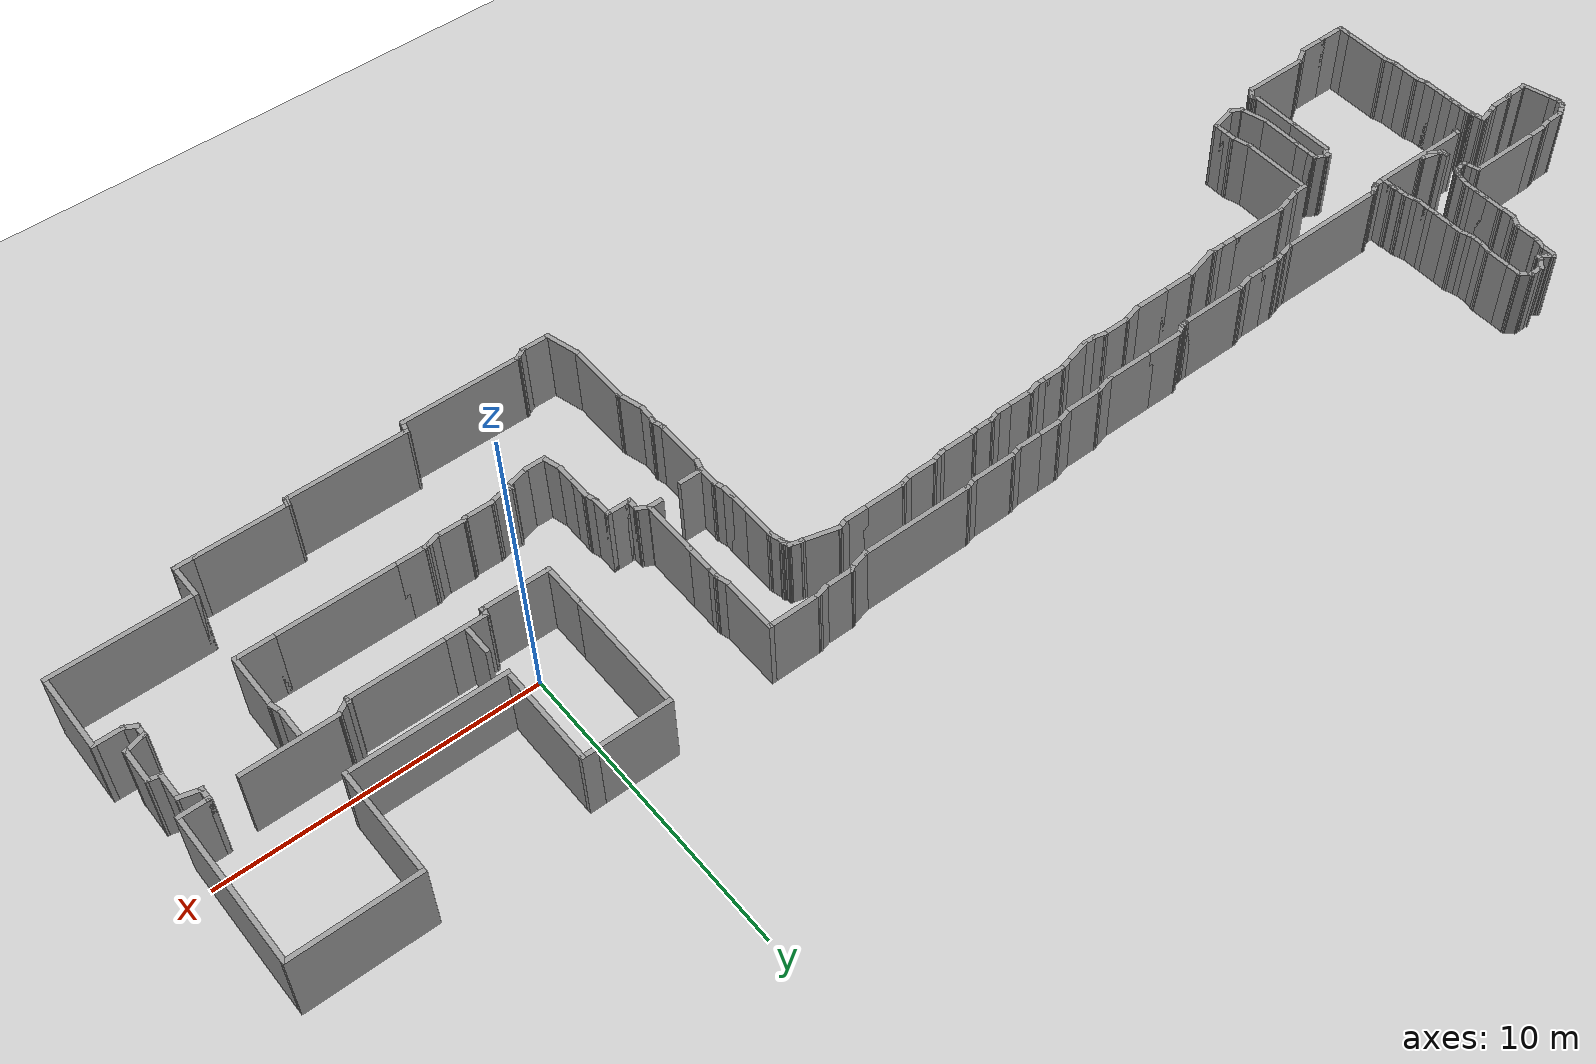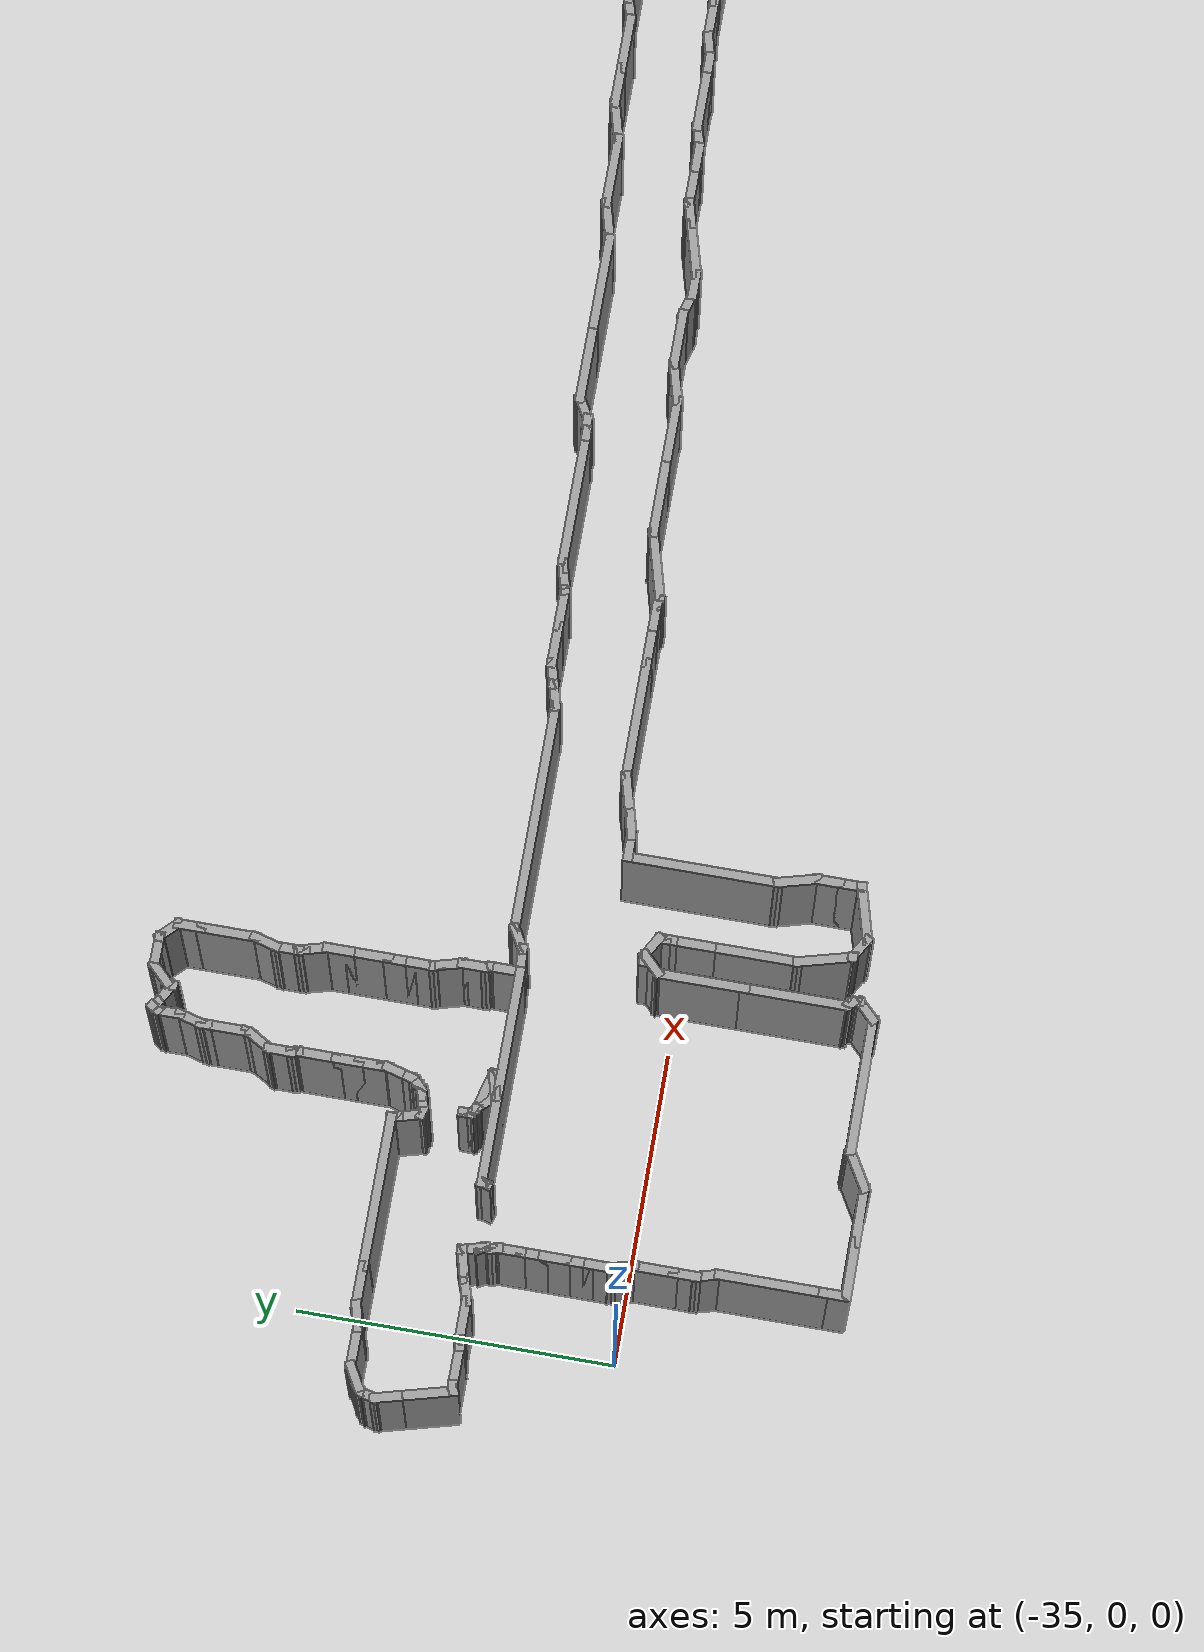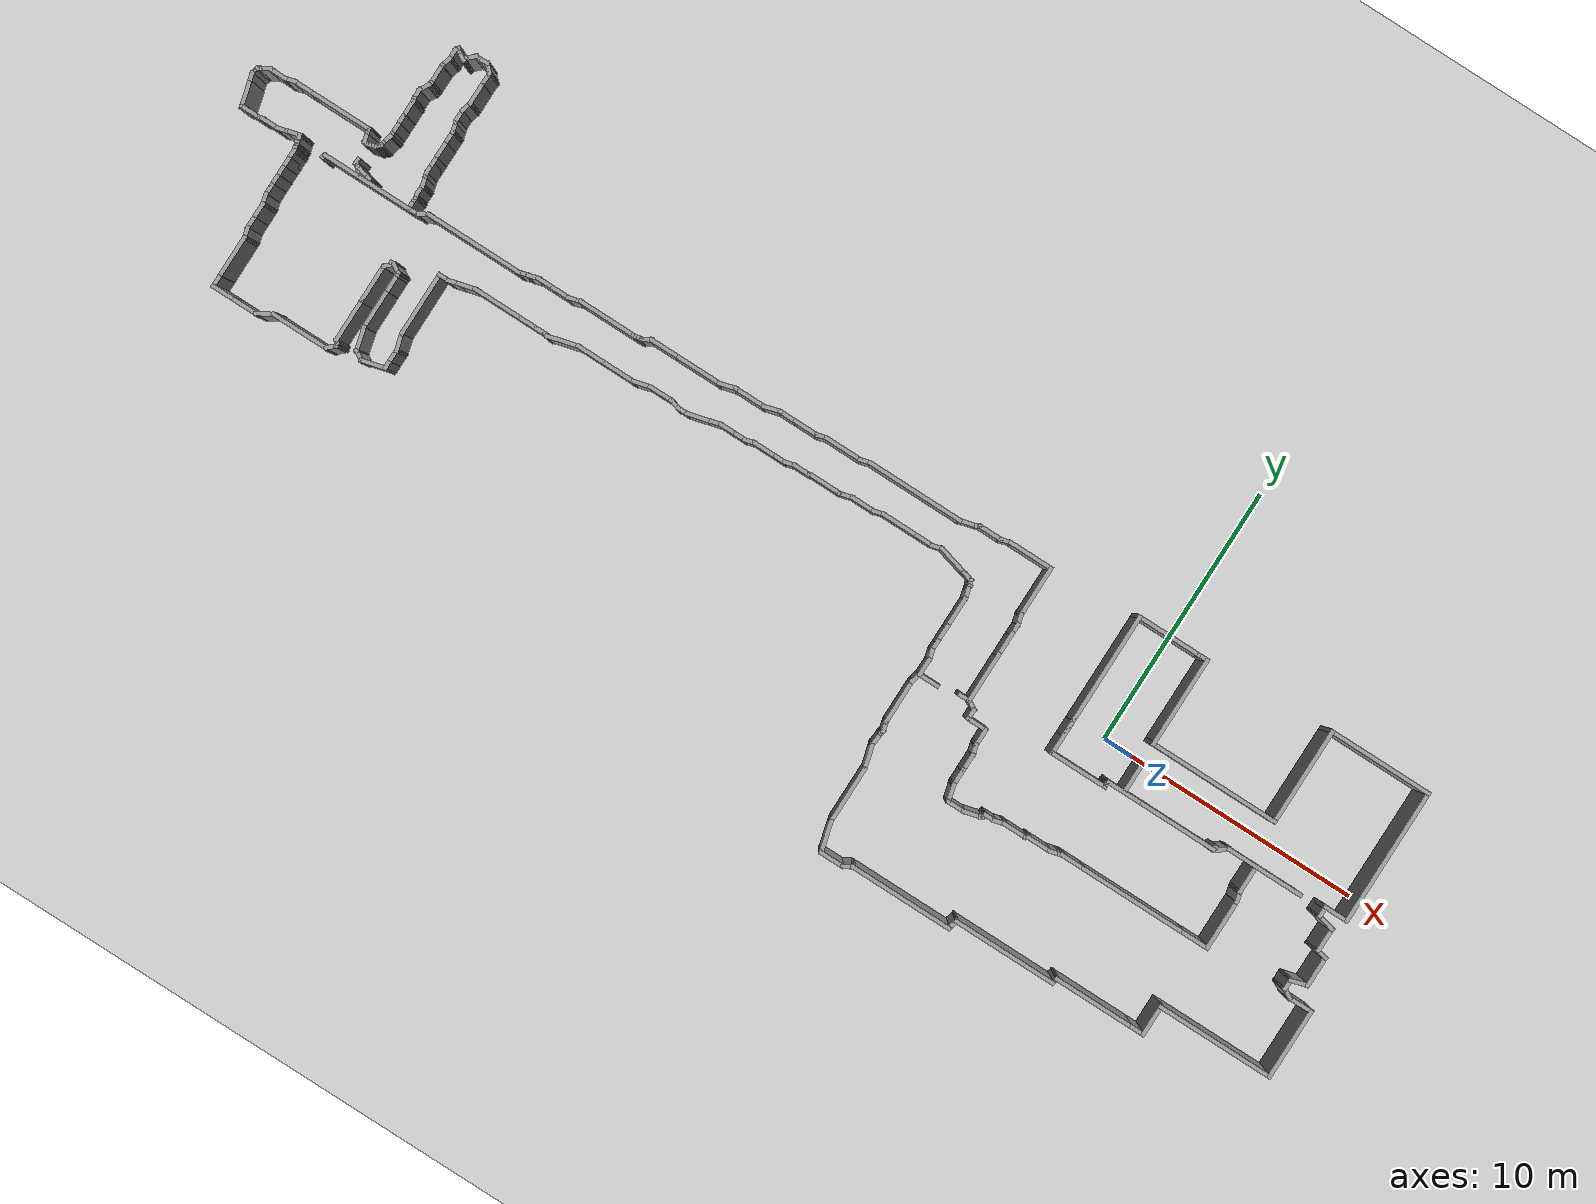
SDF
<sdf version="1.7">
 <world name="default">
  <light name="sun" type="directional">
   <pose>0 0 10 0 -0 0</pose>
   <diffuse>0.8 0.8 0.8 1</diffuse>
   <specular>0.2 0.2 0.2 1</specular>
   <attenuation>
    <range>1000</range>
    <constant>0.9</constant>
    <linear>0.01</linear>
    <quadratic>0.001</quadratic>
   </attenuation>
   <direction>-0.5 0.1 -0.9</direction>
   <spot><inner_angle>0</inner_angle><outer_angle>0</outer_angle><falloff>0</falloff></spot>
  </light>
  <model name="ground_plane">
   <static>1</static>
   <link name="link">
    <collision name="collision">
     <geometry><plane><normal>0 0 1</normal><size>100 100</size></plane></geometry>
     <surface>
      <contact><collide_bitmask>65535</collide_bitmask></contact>
      <friction><ode><mu>100</mu><mu2>50</mu2></ode></friction>
     </surface>
    </collision>
    <visual name="visual">
     <cast_shadows>0</cast_shadows>
     <geometry><plane><normal>0 0 1</normal><size>100 100</size></plane></geometry>
     <material>
      <script><uri>file://media/materials/scripts/gazebo.material</uri><name>Gazebo/Grey</name></script>
     </material>
    </visual>
   </link>
  </model>
  <gravity>0 0 -9.8</gravity>
  <magnetic_field>6e-06 2.3e-05 -4.2e-05</magnetic_field>
  <atmosphere type="adiabatic"/>
  <physics type="ode">
   <max_step_size>0.001</max_step_size>
   <real_time_factor>1</real_time_factor>
   <real_time_update_rate>1000</real_time_update_rate>
  </physics>
  <scene><ambient>0.4 0.4 0.4 1</ambient><background>0.7 0.7 0.7 1</background><shadows>1</shadows></scene>
  <spherical_coordinates>
   <surface_model>EARTH_WGS84</surface_model>
   <latitude_deg>0</latitude_deg>
   <longitude_deg>0</longitude_deg>
   <elevation>0</elevation>
   <heading_deg>0</heading_deg>
  </spherical_coordinates>
  <model name="robovisor_env">
   <pose>-13 -0.201839 0 0 0 3.14</pose>
   <link name="Wall_0">
    <collision name="Wall_0_Collision">
     <geometry><box><size>1 0.15 2.5</size></box></geometry>
     <pose>0 0 1.25 0 -0 0</pose>
    </collision>
    <visual name="Wall_0_Visual">
     <pose>0 0 1.25 0 -0 0</pose>
     <geometry><box><size>1 0.15 2.5</size></box></geometry>
     <material>
      <script><uri>file://media/materials/scripts/gazebo.material</uri><name>Gazebo/Grey</name></script>
      <ambient>1 1 1 1</ambient>
     </material>
     <meta><layer>0</layer></meta>
    </visual>
    <pose>-14.2767 0.369884 0 0 -0 1.5708</pose>
   </link>
   <link name="Wall_101">
    <collision name="Wall_101_Collision">
     <geometry><box><size>2 0.15 2.5</size></box></geometry>
     <pose>0 0 1.25 0 -0 0</pose>
    </collision>
    <visual name="Wall_101_Visual">
     <pose>0 0 1.25 0 -0 0</pose>
     <geometry><box><size>2 0.15 2.5</size></box></geometry>
     <material>
      <script><uri>file://media/materials/scripts/gazebo.material</uri><name>Gazebo/Grey</name></script>
      <ambient>1 1 1 1</ambient>
     </material>
     <meta><layer>0</layer></meta>
    </visual>
    <pose>-8.20957 0.222487 0 0 -0 -1.5708</pose>
   </link>
   <link name="Wall_103">
    <collision name="Wall_103_Collision">
     <geometry><box><size>1 0.15 2.5</size></box></geometry>
     <pose>0 0 1.25 0 -0 0</pose>
    </collision>
    <visual name="Wall_103_Visual">
     <pose>0 0 1.25 0 -0 0</pose>
     <geometry><box><size>1 0.15 2.5</size></box></geometry>
     <material>
      <script><uri>file://media/materials/scripts/gazebo.material</uri><name>Gazebo/Grey</name></script>
      <ambient>1 1 1 1</ambient>
     </material>
     <meta><layer>0</layer></meta>
    </visual>
    <pose>-8.20957 -1.12751 0 0 -0 -1.5708</pose>
   </link>
   <link name="Wall_104">
    <collision name="Wall_104_Collision">
     <geometry><box><size>0.5 0.15 2.5</size></box></geometry>
     <pose>0 0 1.25 0 -0 0</pose>
    </collision>
    <visual name="Wall_104_Visual">
     <pose>0 0 1.25 0 -0 0</pose>
     <geometry><box><size>0.5 0.15 2.5</size></box></geometry>
     <material>
      <script><uri>file://media/materials/scripts/gazebo.material</uri><name>Gazebo/Grey</name></script>
      <ambient>1 1 1 1</ambient>
     </material>
     <meta><layer>0</layer></meta>
    </visual>
    <pose>-8.20957 -1.72751 0 0 -0 -1.5708</pose>
   </link>
   <link name="Wall_105">
    <collision name="Wall_105_Collision">
     <geometry><box><size>0.5 0.15 2.5</size></box></geometry>
     <pose>0 0 1.25 0 -0 0</pose>
    </collision>
    <visual name="Wall_105_Visual">
     <pose>0 0 1.25 0 -0 0</pose>
     <geometry><box><size>0.5 0.15 2.5</size></box></geometry>
     <material>
      <script><uri>file://media/materials/scripts/gazebo.material</uri><name>Gazebo/Grey</name></script>
      <ambient>1 1 1 1</ambient>
     </material>
     <meta><layer>0</layer></meta>
    </visual>
    <pose>-8.16427 -2.07155 0 0 -0 -1.309</pose>
   </link>
   <link name="Wall_106">
    <collision name="Wall_106_Collision">
     <geometry><box><size>2 0.15 2.5</size></box></geometry>
     <pose>0 0 1.25 0 -0 0</pose>
    </collision>
    <visual name="Wall_106_Visual">
     <pose>0 0 1.25 0 -0 0</pose>
     <geometry><box><size>2 0.15 2.5</size></box></geometry>
     <material>
      <script><uri>file://media/materials/scripts/gazebo.material</uri><name>Gazebo/Grey</name></script>
      <ambient>1 1 1 1</ambient>
     </material>
     <meta><layer>0</layer></meta>
    </visual>
    <pose>-8.11898 -3.16559 0 0 -0 -1.5708</pose>
   </link>
   <link name="Wall_107">
    <collision name="Wall_107_Collision">
     <geometry><box><size>1.75 0.15 2.5</size></box></geometry>
     <pose>0 0 1.25 0 -0 0</pose>
    </collision>
    <visual name="Wall_107_Visual">
     <pose>0 0 1.25 0 -0 0</pose>
     <geometry><box><size>1.75 0.15 2.5</size></box></geometry>
     <material>
      <script><uri>file://media/materials/scripts/gazebo.material</uri><name>Gazebo/Grey</name></script>
      <ambient>1 1 1 1</ambient>
     </material>
     <meta><layer>0</layer></meta>
    </visual>
    <pose>-7.31898 -4.09059 0 0 -0 0</pose>
   </link>
   <link name="Wall_108">
    <collision name="Wall_108_Collision">
     <geometry><box><size>0.5 0.15 2.5</size></box></geometry>
     <pose>0 0 1.25 0 -0 0</pose>
    </collision>
    <visual name="Wall_108_Visual">
     <pose>0 0 1.25 0 -0 0</pose>
     <geometry><box><size>0.5 0.15 2.5</size></box></geometry>
     <material>
      <script><uri>file://media/materials/scripts/gazebo.material</uri><name>Gazebo/Grey</name></script>
      <ambient>1 1 1 1</ambient>
     </material>
     <meta><layer>0</layer></meta>
    </visual>
    <pose>-6.34994 -4.04529 0 0 -0 0.261799</pose>
   </link>
   <link name="Wall_109">
    <collision name="Wall_109_Collision">
     <geometry><box><size>1 0.15 2.5</size></box></geometry>
     <pose>0 0 1.25 0 -0 0</pose>
    </collision>
    <visual name="Wall_109_Visual">
     <pose>0 0 1.25 0 -0 0</pose>
     <geometry><box><size>1 0.15 2.5</size></box></geometry>
     <material>
      <script><uri>file://media/materials/scripts/gazebo.material</uri><name>Gazebo/Grey</name></script>
      <ambient>1 1 1 1</ambient>
     </material>
     <meta><layer>0</layer></meta>
    </visual>
    <pose>-5.75591 -4 0 0 -0 0</pose>
   </link>
   <link name="Wall_11">
    <collision name="Wall_11_Collision">
     <geometry><box><size>4.25 0.15 2.5</size></box></geometry>
     <pose>0 0 1.25 0 -0 0</pose>
    </collision>
    <visual name="Wall_11_Visual">
     <pose>0 0 1.25 0 -0 0</pose>
     <geometry><box><size>4.25 0.15 2.5</size></box></geometry>
     <material>
      <script><uri>file://media/materials/scripts/gazebo.material</uri><name>Gazebo/Grey</name></script>
      <ambient>1 1 1 1</ambient>
     </material>
     <meta><layer>0</layer></meta>
    </visual>
    <pose>-11.5267 -2.27908 0 0 -0 -1.5708</pose>
   </link>
   <link name="Wall_110">
    <collision name="Wall_110_Collision">
     <geometry><box><size>0.25 0.15 2.5</size></box></geometry>
     <pose>0 0 1.25 0 -0 0</pose>
    </collision>
    <visual name="Wall_110_Visual">
     <pose>0 0 1.25 0 -0 0</pose>
     <geometry><box><size>0.25 0.15 2.5</size></box></geometry>
     <material>
      <script><uri>file://media/materials/scripts/gazebo.material</uri><name>Gazebo/Grey</name></script>
      <ambient>1 1 1 1</ambient>
     </material>
     <meta><layer>0</layer></meta>
    </visual>
    <pose>-5.28761 -3.975 0 0 -0 0.523599</pose>
   </link>
   <link name="Wall_111">
    <collision name="Wall_111_Collision">
     <geometry><box><size>0.75 0.15 2.5</size></box></geometry>
     <pose>0 0 1.25 0 -0 0</pose>
    </collision>
    <visual name="Wall_111_Visual">
     <pose>0 0 1.25 0 -0 0</pose>
     <geometry><box><size>0.75 0.15 2.5</size></box></geometry>
     <material>
      <script><uri>file://media/materials/scripts/gazebo.material</uri><name>Gazebo/Grey</name></script>
      <ambient>1 1 1 1</ambient>
     </material>
     <meta><layer>0</layer></meta>
    </visual>
    <pose>-4.95453 -3.87236 0 0 -0 0.261799</pose>
   </link>
   <link name="Wall_112">
    <collision name="Wall_112_Collision">
     <geometry><box><size>3.75 0.15 2.5</size></box></geometry>
     <pose>0 0 1.25 0 -0 0</pose>
    </collision>
    <visual name="Wall_112_Visual">
     <pose>0 0 1.25 0 -0 0</pose>
     <geometry><box><size>3.75 0.15 2.5</size></box></geometry>
     <material>
      <script><uri>file://media/materials/scripts/gazebo.material</uri><name>Gazebo/Grey</name></script>
      <ambient>1 1 1 1</ambient>
     </material>
     <meta><layer>0</layer></meta>
    </visual>
    <pose>-2.86475 -3.79471 0 0 -0 0</pose>
   </link>
   <link name="Wall_113">
    <collision name="Wall_113_Collision">
     <geometry><box><size>0.5 0.15 2.5</size></box></geometry>
     <pose>0 0 1.25 0 -0 0</pose>
    </collision>
    <visual name="Wall_113_Visual">
     <pose>0 0 1.25 0 -0 0</pose>
     <geometry><box><size>0.5 0.15 2.5</size></box></geometry>
     <material>
      <script><uri>file://media/materials/scripts/gazebo.material</uri><name>Gazebo/Grey</name></script>
      <ambient>1 1 1 1</ambient>
     </material>
     <meta><layer>0</layer></meta>
    </visual>
    <pose>-0.895711 -3.74942 0 0 -0 0.261799</pose>
   </link>
   <link name="Wall_114">
    <collision name="Wall_114_Collision">
     <geometry><box><size>1.5 0.15 2.5</size></box></geometry>
     <pose>0 0 1.25 0 -0 0</pose>
    </collision>
    <visual name="Wall_114_Visual">
     <pose>0 0 1.25 0 -0 0</pose>
     <geometry><box><size>1.5 0.15 2.5</size></box></geometry>
     <material>
      <script><uri>file://media/materials/scripts/gazebo.material</uri><name>Gazebo/Grey</name></script>
      <ambient>1 1 1 1</ambient>
     </material>
     <meta><layer>0</layer></meta>
    </visual>
    <pose>-0.051674 -3.70412 0 0 -0 0</pose>
   </link>
   <link name="Wall_115">
    <collision name="Wall_115_Collision">
     <geometry><box><size>0.5 0.15 2.5</size></box></geometry>
     <pose>0 0 1.25 0 -0 0</pose>
    </collision>
    <visual name="Wall_115_Visual">
     <pose>0 0 1.25 0 -0 0</pose>
     <geometry><box><size>0.5 0.15 2.5</size></box></geometry>
     <material>
      <script><uri>file://media/materials/scripts/gazebo.material</uri><name>Gazebo/Grey</name></script>
      <ambient>1 1 1 1</ambient>
     </material>
     <meta><layer>0</layer></meta>
    </visual>
    <pose>0.792363 -3.65883 0 0 -0 0.261799</pose>
   </link>
   <link name="Wall_116">
    <collision name="Wall_116_Collision">
     <geometry><box><size>1 0.15 2.5</size></box></geometry>
     <pose>0 0 1.25 0 -0 0</pose>
    </collision>
    <visual name="Wall_116_Visual">
     <pose>0 0 1.25 0 -0 0</pose>
     <geometry><box><size>1 0.15 2.5</size></box></geometry>
     <material>
      <script><uri>file://media/materials/scripts/gazebo.material</uri><name>Gazebo/Grey</name></script>
      <ambient>1 1 1 1</ambient>
     </material>
     <meta><layer>0</layer></meta>
    </visual>
    <pose>1.3864 -3.61354 0 0 -0 0</pose>
   </link>
   <link name="Wall_117">
    <collision name="Wall_117_Collision">
     <geometry><box><size>0.75 0.15 2.5</size></box></geometry>
     <pose>0 0 1.25 0 -0 0</pose>
    </collision>
    <visual name="Wall_117_Visual">
     <pose>0 0 1.25 0 -0 0</pose>
     <geometry><box><size>0.75 0.15 2.5</size></box></geometry>
     <material>
      <script><uri>file://media/materials/scripts/gazebo.material</uri><name>Gazebo/Grey</name></script>
      <ambient>1 1 1 1</ambient>
     </material>
     <meta><layer>0</layer></meta>
    </visual>
    <pose>2.1114 -3.61354 0 0 -0 0</pose>
   </link>
   <link name="Wall_118">
    <collision name="Wall_118_Collision">
     <geometry><box><size>0.75 0.15 2.5</size></box></geometry>
     <pose>0 0 1.25 0 -0 0</pose>
    </collision>
    <visual name="Wall_118_Visual">
     <pose>0 0 1.25 0 -0 0</pose>
     <geometry><box><size>0.75 0.15 2.5</size></box></geometry>
     <material>
      <script><uri>file://media/materials/scripts/gazebo.material</uri><name>Gazebo/Grey</name></script>
      <ambient>1 1 1 1</ambient>
     </material>
     <meta><layer>0</layer></meta>
    </visual>
    <pose>2.70118 -3.53589 0 0 -0 0.261799</pose>
   </link>
   <link name="Wall_119">
    <collision name="Wall_119_Collision">
     <geometry><box><size>1.25 0.15 2.5</size></box></geometry>
     <pose>0 0 1.25 0 -0 0</pose>
    </collision>
    <visual name="Wall_119_Visual">
     <pose>0 0 1.25 0 -0 0</pose>
     <geometry><box><size>1.25 0.15 2.5</size></box></geometry>
     <material>
      <script><uri>file://media/materials/scripts/gazebo.material</uri><name>Gazebo/Grey</name></script>
      <ambient>1 1 1 1</ambient>
     </material>
     <meta><layer>0</layer></meta>
    </visual>
    <pose>3.54096 -3.45824 0 0 -0 0</pose>
   </link>
   <link name="Wall_12">
    <collision name="Wall_12_Collision">
     <geometry><box><size>2.5 0.15 2.5</size></box></geometry>
     <pose>0 0 1.25 0 -0 0</pose>
    </collision>
    <visual name="Wall_12_Visual">
     <pose>0 0 1.25 0 -0 0</pose>
     <geometry><box><size>2.5 0.15 2.5</size></box></geometry>
     <material>
      <script><uri>file://media/materials/scripts/gazebo.material</uri><name>Gazebo/Grey</name></script>
      <ambient>1 1 1 1</ambient>
     </material>
     <meta><layer>0</layer></meta>
    </visual>
    <pose>-12.7017 -4.32909 0 0 -0 3.14159</pose>
   </link>
   <link name="Wall_120">
    <collision name="Wall_120_Collision">
     <geometry><box><size>0.75 0.15 2.5</size></box></geometry>
     <pose>0 0 1.25 0 -0 0</pose>
    </collision>
    <visual name="Wall_120_Visual">
     <pose>0 0 1.25 0 -0 0</pose>
     <geometry><box><size>0.75 0.15 2.5</size></box></geometry>
     <material>
      <script><uri>file://media/materials/scripts/gazebo.material</uri><name>Gazebo/Grey</name></script>
      <ambient>1 1 1 1</ambient>
     </material>
     <meta><layer>0</layer></meta>
    </visual>
    <pose>4.38073 -3.3806 0 0 -0 0.261799</pose>
   </link>
   <link name="Wall_121">
    <collision name="Wall_121_Collision">
     <geometry><box><size>1.75 0.15 2.5</size></box></geometry>
     <pose>0 0 1.25 0 -0 0</pose>
    </collision>
    <visual name="Wall_121_Visual">
     <pose>0 0 1.25 0 -0 0</pose>
     <geometry><box><size>1.75 0.15 2.5</size></box></geometry>
     <material>
      <script><uri>file://media/materials/scripts/gazebo.material</uri><name>Gazebo/Grey</name></script>
      <ambient>1 1 1 1</ambient>
     </material>
     <meta><layer>0</layer></meta>
    </visual>
    <pose>5.47051 -3.30295 0 0 -0 0</pose>
   </link>
   <link name="Wall_123">
    <collision name="Wall_123_Collision">
     <geometry><box><size>0.75 0.15 2.5</size></box></geometry>
     <pose>0 0 1.25 0 -0 0</pose>
    </collision>
    <visual name="Wall_123_Visual">
     <pose>0 0 1.25 0 -0 0</pose>
     <geometry><box><size>0.75 0.15 2.5</size></box></geometry>
     <material>
      <script><uri>file://media/materials/scripts/gazebo.material</uri><name>Gazebo/Grey</name></script>
      <ambient>1 1 1 1</ambient>
     </material>
     <meta><layer>0</layer></meta>
    </visual>
    <pose>-6.32777 1.01254 0 0 -0 -1.5708</pose>
   </link>
   <link name="Wall_124">
    <collision name="Wall_124_Collision">
     <geometry><box><size>0.5 0.15 2.5</size></box></geometry>
     <pose>0 0 1.25 0 -0 0</pose>
    </collision>
    <visual name="Wall_124_Visual">
     <pose>0 0 1.25 0 -0 0</pose>
     <geometry><box><size>0.5 0.15 2.5</size></box></geometry>
     <material>
      <script><uri>file://media/materials/scripts/gazebo.material</uri><name>Gazebo/Grey</name></script>
      <ambient>1 1 1 1</ambient>
     </material>
     <meta><layer>0</layer></meta>
    </visual>
    <pose>-6.28248 0.543504 0 0 -0 -1.309</pose>
   </link>
   <link name="Wall_125">
    <collision name="Wall_125_Collision">
     <geometry><box><size>0.5 0.15 2.5</size></box></geometry>
     <pose>0 0 1.25 0 -0 0</pose>
    </collision>
    <visual name="Wall_125_Visual">
     <pose>0 0 1.25 0 -0 0</pose>
     <geometry><box><size>0.5 0.15 2.5</size></box></geometry>
     <material>
      <script><uri>file://media/materials/scripts/gazebo.material</uri><name>Gazebo/Grey</name></script>
      <ambient>1 1 1 1</ambient>
     </material>
     <meta><layer>0</layer></meta>
    </visual>
    <pose>-6.23718 0.199467 0 0 -0 -1.5708</pose>
   </link>
   <link name="Wall_126">
    <collision name="Wall_126_Collision">
     <geometry><box><size>0.75 0.15 2.5</size></box></geometry>
     <pose>0 0 1.25 0 -0 0</pose>
    </collision>
    <visual name="Wall_126_Visual">
     <pose>0 0 1.25 0 -0 0</pose>
     <geometry><box><size>0.75 0.15 2.5</size></box></geometry>
     <material>
      <script><uri>file://media/materials/scripts/gazebo.material</uri><name>Gazebo/Grey</name></script>
      <ambient>1 1 1 1</ambient>
     </material>
     <meta><layer>0</layer></meta>
    </visual>
    <pose>-6.23718 -0.275533 0 0 -0 -1.5708</pose>
   </link>
   <link name="Wall_127">
    <collision name="Wall_127_Collision">
     <geometry><box><size>1.25 0.15 2.5</size></box></geometry>
     <pose>0 0 1.25 0 -0 0</pose>
    </collision>
    <visual name="Wall_127_Visual">
     <pose>0 0 1.25 0 -0 0</pose>
     <geometry><box><size>1.25 0.15 2.5</size></box></geometry>
     <material>
      <script><uri>file://media/materials/scripts/gazebo.material</uri><name>Gazebo/Grey</name></script>
      <ambient>1 1 1 1</ambient>
     </material>
     <meta><layer>0</layer></meta>
    </visual>
    <pose>-6.23718 -1.12553 0 0 -0 -1.5708</pose>
   </link>
   <link name="Wall_128">
    <collision name="Wall_128_Collision">
     <geometry><box><size>0.5 0.15 2.5</size></box></geometry>
     <pose>0 0 1.25 0 -0 0</pose>
    </collision>
    <visual name="Wall_128_Visual">
     <pose>0 0 1.25 0 -0 0</pose>
     <geometry><box><size>0.5 0.15 2.5</size></box></geometry>
     <material>
      <script><uri>file://media/materials/scripts/gazebo.material</uri><name>Gazebo/Grey</name></script>
      <ambient>1 1 1 1</ambient>
     </material>
     <meta><layer>0</layer></meta>
    </visual>
    <pose>-6.19189 -1.84457 0 0 -0 -1.309</pose>
   </link>
   <link name="Wall_129">
    <collision name="Wall_129_Collision">
     <geometry><box><size>0.25 0.15 2.5</size></box></geometry>
     <pose>0 0 1.25 0 -0 0</pose>
    </collision>
    <visual name="Wall_129_Visual">
     <pose>0 0 1.25 0 -0 0</pose>
     <geometry><box><size>0.25 0.15 2.5</size></box></geometry>
     <material>
      <script><uri>file://media/materials/scripts/gazebo.material</uri><name>Gazebo/Grey</name></script>
      <ambient>1 1 1 1</ambient>
     </material>
     <meta><layer>0</layer></meta>
    </visual>
    <pose>-6.1466 -2.06361 0 0 -0 -1.5708</pose>
   </link>
   <link name="Wall_13">
    <collision name="Wall_13_Collision">
     <geometry><box><size>0.5 0.15 2.5</size></box></geometry>
     <pose>0 0 1.25 0 -0 0</pose>
    </collision>
    <visual name="Wall_13_Visual">
     <pose>0 0 1.25 0 -0 0</pose>
     <geometry><box><size>0.5 0.15 2.5</size></box></geometry>
     <material>
      <script><uri>file://media/materials/scripts/gazebo.material</uri><name>Gazebo/Grey</name></script>
      <ambient>1 1 1 1</ambient>
     </material>
     <meta><layer>0</layer></meta>
    </visual>
    <pose>-14.0517 -4.32909 0 0 -0 3.14159</pose>
   </link>
   <link name="Wall_130">
    <collision name="Wall_130_Collision">
     <geometry><box><size>0.25 0.15 2.5</size></box></geometry>
     <pose>0 0 1.25 0 -0 0</pose>
    </collision>
    <visual name="Wall_130_Visual">
     <pose>0 0 1.25 0 -0 0</pose>
     <geometry><box><size>0.25 0.15 2.5</size></box></geometry>
     <material>
      <script><uri>file://media/materials/scripts/gazebo.material</uri><name>Gazebo/Grey</name></script>
      <ambient>1 1 1 1</ambient>
     </material>
     <meta><layer>0</layer></meta>
    </visual>
    <pose>-6.1216 -2.15691 0 0 -0 -1.0472</pose>
   </link>
   <link name="Wall_131">
    <collision name="Wall_131_Collision">
     <geometry><box><size>0.25 0.15 2.5</size></box></geometry>
     <pose>0 0 1.25 0 -0 0</pose>
    </collision>
    <visual name="Wall_131_Visual">
     <pose>0 0 1.25 0 -0 0</pose>
     <geometry><box><size>0.25 0.15 2.5</size></box></geometry>
     <material>
      <script><uri>file://media/materials/scripts/gazebo.material</uri><name>Gazebo/Grey</name></script>
      <ambient>1 1 1 1</ambient>
     </material>
     <meta><layer>0</layer></meta>
    </visual>
    <pose>-6.08366 -2.24851 0 0 -0 -1.309</pose>
   </link>
   <link name="Wall_132">
    <collision name="Wall_132_Collision">
     <geometry><box><size>0.15 0.15 2.5</size></box></geometry>
     <pose>0 0 1.25 0 -0 0</pose>
    </collision>
    <visual name="Wall_132_Visual">
     <pose>0 0 1.25 0 -0 0</pose>
     <geometry><box><size>0.15 0.15 2.5</size></box></geometry>
     <material>
      <script><uri>file://media/materials/scripts/gazebo.material</uri><name>Gazebo/Grey</name></script>
      <ambient>1 1 1 1</ambient>
     </material>
     <meta><layer>0</layer></meta>
    </visual>
    <pose>-6.07071 -2.2968 0 0 -0 0</pose>
   </link>
   <link name="Wall_133">
    <collision name="Wall_133_Collision">
     <geometry><box><size>0.5 0.15 2.5</size></box></geometry>
     <pose>0 0 1.25 0 -0 0</pose>
    </collision>
    <visual name="Wall_133_Visual">
     <pose>0 0 1.25 0 -0 0</pose>
     <geometry><box><size>0.5 0.15 2.5</size></box></geometry>
     <material>
      <script><uri>file://media/materials/scripts/gazebo.material</uri><name>Gazebo/Grey</name></script>
      <ambient>1 1 1 1</ambient>
     </material>
     <meta><layer>0</layer></meta>
    </visual>
    <pose>-5.90168 -2.3421 0 0 -0 -0.261799</pose>
   </link>
   <link name="Wall_134">
    <collision name="Wall_134_Collision">
     <geometry><box><size>0.15 0.15 2.5</size></box></geometry>
     <pose>0 0 1.25 0 -0 0</pose>
    </collision>
    <visual name="Wall_134_Visual">
     <pose>0 0 1.25 0 -0 0</pose>
     <geometry><box><size>0.15 0.15 2.5</size></box></geometry>
     <material>
      <script><uri>file://media/materials/scripts/gazebo.material</uri><name>Gazebo/Grey</name></script>
      <ambient>1 1 1 1</ambient>
     </material>
     <meta><layer>0</layer></meta>
    </visual>
    <pose>-5.73264 -2.38739 0 0 -0 0</pose>
   </link>
   <link name="Wall_135">
    <collision name="Wall_135_Collision">
     <geometry><box><size>1.25 0.15 2.5</size></box></geometry>
     <pose>0 0 1.25 0 -0 0</pose>
    </collision>
    <visual name="Wall_135_Visual">
     <pose>0 0 1.25 0 -0 0</pose>
     <geometry><box><size>1.25 0.15 2.5</size></box></geometry>
     <material>
      <script><uri>file://media/materials/scripts/gazebo.material</uri><name>Gazebo/Grey</name></script>
      <ambient>1 1 1 1</ambient>
     </material>
     <meta><layer>0</layer></meta>
    </visual>
    <pose>-5.20138 -2.52974 0 0 -0 -0.261799</pose>
   </link>
   <link name="Wall_136">
    <collision name="Wall_136_Collision">
     <geometry><box><size>0.5 0.15 2.5</size></box></geometry>
     <pose>0 0 1.25 0 -0 0</pose>
    </collision>
    <visual name="Wall_136_Visual">
     <pose>0 0 1.25 0 -0 0</pose>
     <geometry><box><size>0.5 0.15 2.5</size></box></geometry>
     <material>
      <script><uri>file://media/materials/scripts/gazebo.material</uri><name>Gazebo/Grey</name></script>
      <ambient>1 1 1 1</ambient>
     </material>
     <meta><layer>0</layer></meta>
    </visual>
    <pose>-4.50109 -2.6268 0 0 -0 0.261799</pose>
   </link>
   <link name="Wall_137">
    <collision name="Wall_137_Collision">
     <geometry><box><size>0.75 0.15 2.5</size></box></geometry>
     <pose>0 0 1.25 0 -0 0</pose>
    </collision>
    <visual name="Wall_137_Visual">
     <pose>0 0 1.25 0 -0 0</pose>
     <geometry><box><size>0.75 0.15 2.5</size></box></geometry>
     <material>
      <script><uri>file://media/materials/scripts/gazebo.material</uri><name>Gazebo/Grey</name></script>
      <ambient>1 1 1 1</ambient>
     </material>
     <meta><layer>0</layer></meta>
    </visual>
    <pose>-4.03205 -2.5815 0 0 -0 0</pose>
   </link>
   <link name="Wall_138">
    <collision name="Wall_138_Collision">
     <geometry><box><size>1.5 0.15 2.5</size></box></geometry>
     <pose>0 0 1.25 0 -0 0</pose>
    </collision>
    <visual name="Wall_138_Visual">
     <pose>0 0 1.25 0 -0 0</pose>
     <geometry><box><size>1.5 0.15 2.5</size></box></geometry>
     <material>
      <script><uri>file://media/materials/scripts/gazebo.material</uri><name>Gazebo/Grey</name></script>
      <ambient>1 1 1 1</ambient>
     </material>
     <meta><layer>0</layer></meta>
    </visual>
    <pose>-3.05705 -2.5815 0 0 -0 0</pose>
   </link>
   <link name="Wall_139">
    <collision name="Wall_139_Collision">
     <geometry><box><size>0.5 0.15 2.5</size></box></geometry>
     <pose>0 0 1.25 0 -0 0</pose>
    </collision>
    <visual name="Wall_139_Visual">
     <pose>0 0 1.25 0 -0 0</pose>
     <geometry><box><size>0.5 0.15 2.5</size></box></geometry>
     <material>
      <script><uri>file://media/materials/scripts/gazebo.material</uri><name>Gazebo/Grey</name></script>
      <ambient>1 1 1 1</ambient>
     </material>
     <meta><layer>0</layer></meta>
    </visual>
    <pose>-2.21301 -2.53621 0 0 -0 0.261799</pose>
   </link>
   <link name="Wall_14">
    <collision name="Wall_14_Collision">
     <geometry><box><size>3.5 0.15 2.5</size></box></geometry>
     <pose>0 0 1.25 0 -0 0</pose>
    </collision>
    <visual name="Wall_14_Visual">
     <pose>0 0 1.25 0 -0 0</pose>
     <geometry><box><size>3.5 0.15 2.5</size></box></geometry>
     <material>
      <script><uri>file://media/materials/scripts/gazebo.material</uri><name>Gazebo/Grey</name></script>
      <ambient>1 1 1 1</ambient>
     </material>
     <meta><layer>0</layer></meta>
    </visual>
    <pose>-14.2267 -2.65408 0 0 -0 1.5708</pose>
   </link>
   <link name="Wall_140">
    <collision name="Wall_140_Collision">
     <geometry><box><size>1 0.15 2.5</size></box></geometry>
     <pose>0 0 1.25 0 -0 0</pose>
    </collision>
    <visual name="Wall_140_Visual">
     <pose>0 0 1.25 0 -0 0</pose>
     <geometry><box><size>1 0.15 2.5</size></box></geometry>
     <material>
      <script><uri>file://media/materials/scripts/gazebo.material</uri><name>Gazebo/Grey</name></script>
      <ambient>1 1 1 1</ambient>
     </material>
     <meta><layer>0</layer></meta>
    </visual>
    <pose>-1.61898 -2.49092 0 0 -0 0</pose>
   </link>
   <link name="Wall_141">
    <collision name="Wall_141_Collision">
     <geometry><box><size>0.5 0.15 2.5</size></box></geometry>
     <pose>0 0 1.25 0 -0 0</pose>
    </collision>
    <visual name="Wall_141_Visual">
     <pose>0 0 1.25 0 -0 0</pose>
     <geometry><box><size>0.5 0.15 2.5</size></box></geometry>
     <material>
      <script><uri>file://media/materials/scripts/gazebo.material</uri><name>Gazebo/Grey</name></script>
      <ambient>1 1 1 1</ambient>
     </material>
     <meta><layer>0</layer></meta>
    </visual>
    <pose>-1.02494 -2.44562 0 0 -0 0.261799</pose>
   </link>
   <link name="Wall_142">
    <collision name="Wall_142_Collision">
     <geometry><box><size>0.25 0.15 2.5</size></box></geometry>
     <pose>0 0 1.25 0 -0 0</pose>
    </collision>
    <visual name="Wall_142_Visual">
     <pose>0 0 1.25 0 -0 0</pose>
     <geometry><box><size>0.25 0.15 2.5</size></box></geometry>
     <material>
      <script><uri>file://media/materials/scripts/gazebo.material</uri><name>Gazebo/Grey</name></script>
      <ambient>1 1 1 1</ambient>
     </material>
     <meta><layer>0</layer></meta>
    </visual>
    <pose>-0.807605 -2.38739 0 0 -0 0.261799</pose>
   </link>
   <link name="Wall_143">
    <collision name="Wall_143_Collision">
     <geometry><box><size>1.25 0.15 2.5</size></box></geometry>
     <pose>0 0 1.25 0 -0 0</pose>
    </collision>
    <visual name="Wall_143_Visual">
     <pose>0 0 1.25 0 -0 0</pose>
     <geometry><box><size>1.25 0.15 2.5</size></box></geometry>
     <material>
      <script><uri>file://media/materials/scripts/gazebo.material</uri><name>Gazebo/Grey</name></script>
      <ambient>1 1 1 1</ambient>
     </material>
     <meta><layer>0</layer></meta>
    </visual>
    <pose>-0.209308 -2.37445 0 0 -0 0</pose>
   </link>
   <link name="Wall_144">
    <collision name="Wall_144_Collision">
     <geometry><box><size>0.25 0.15 2.5</size></box></geometry>
     <pose>0 0 1.25 0 -0 0</pose>
    </collision>
    <visual name="Wall_144_Visual">
     <pose>0 0 1.25 0 -0 0</pose>
     <geometry><box><size>0.25 0.15 2.5</size></box></geometry>
     <material>
      <script><uri>file://media/materials/scripts/gazebo.material</uri><name>Gazebo/Grey</name></script>
      <ambient>1 1 1 1</ambient>
     </material>
     <meta><layer>0</layer></meta>
    </visual>
    <pose>0.388988 -2.36151 0 0 -0 0.261799</pose>
   </link>
   <link name="Wall_145">
    <collision name="Wall_145_Collision">
     <geometry><box><size>0.75 0.15 2.5</size></box></geometry>
     <pose>0 0 1.25 0 -0 0</pose>
    </collision>
    <visual name="Wall_145_Visual">
     <pose>0 0 1.25 0 -0 0</pose>
     <geometry><box><size>0.75 0.15 2.5</size></box></geometry>
     <material>
      <script><uri>file://media/materials/scripts/gazebo.material</uri><name>Gazebo/Grey</name></script>
      <ambient>1 1 1 1</ambient>
     </material>
     <meta><layer>0</layer></meta>
    </visual>
    <pose>0.737285 -2.34857 0 0 -0 0</pose>
   </link>
   <link name="Wall_146">
    <collision name="Wall_146_Collision">
     <geometry><box><size>0.5 0.15 2.5</size></box></geometry>
     <pose>0 0 1.25 0 -0 0</pose>
    </collision>
    <visual name="Wall_146_Visual">
     <pose>0 0 1.25 0 -0 0</pose>
     <geometry><box><size>0.5 0.15 2.5</size></box></geometry>
     <material>
      <script><uri>file://media/materials/scripts/gazebo.material</uri><name>Gazebo/Grey</name></script>
      <ambient>1 1 1 1</ambient>
     </material>
     <meta><layer>0</layer></meta>
    </visual>
    <pose>1.20632 -2.30327 0 0 -0 0.261799</pose>
   </link>
   <link name="Wall_147">
    <collision name="Wall_147_Collision">
     <geometry><box><size>0.5 0.15 2.5</size></box></geometry>
     <pose>0 0 1.25 0 -0 0</pose>
    </collision>
    <visual name="Wall_147_Visual">
     <pose>0 0 1.25 0 -0 0</pose>
     <geometry><box><size>0.5 0.15 2.5</size></box></geometry>
     <material>
      <script><uri>file://media/materials/scripts/gazebo.material</uri><name>Gazebo/Grey</name></script>
      <ambient>1 1 1 1</ambient>
     </material>
     <meta><layer>0</layer></meta>
    </visual>
    <pose>1.55036 -2.25798 0 0 -0 0</pose>
   </link>
   <link name="Wall_148">
    <collision name="Wall_148_Collision">
     <geometry><box><size>1 0.15 2.5</size></box></geometry>
     <pose>0 0 1.25 0 -0 0</pose>
    </collision>
    <visual name="Wall_148_Visual">
     <pose>0 0 1.25 0 -0 0</pose>
     <geometry><box><size>1 0.15 2.5</size></box></geometry>
     <material>
      <script><uri>file://media/materials/scripts/gazebo.material</uri><name>Gazebo/Grey</name></script>
      <ambient>1 1 1 1</ambient>
     </material>
     <meta><layer>0</layer></meta>
    </visual>
    <pose>2.15036 -2.25798 0 0 -0 0</pose>
   </link>
   <link name="Wall_149">
    <collision name="Wall_149_Collision">
     <geometry><box><size>0.5 0.15 2.5</size></box></geometry>
     <pose>0 0 1.25 0 -0 0</pose>
    </collision>
    <visual name="Wall_149_Visual">
     <pose>0 0 1.25 0 -0 0</pose>
     <geometry><box><size>0.5 0.15 2.5</size></box></geometry>
     <material>
      <script><uri>file://media/materials/scripts/gazebo.material</uri><name>Gazebo/Grey</name></script>
      <ambient>1 1 1 1</ambient>
     </material>
     <meta><layer>0</layer></meta>
    </visual>
    <pose>2.74439 -2.21269 0 0 -0 0.261799</pose>
   </link>
   <link name="Wall_15">
    <collision name="Wall_15_Collision">
     <geometry><box><size>5 0.15 2.5</size></box></geometry>
     <pose>0 0 1.25 0 -0 0</pose>
    </collision>
    <visual name="Wall_15_Visual">
     <pose>0 0 1.25 0 -0 0</pose>
     <geometry><box><size>5 0.15 2.5</size></box></geometry>
     <material>
      <script><uri>file://media/materials/scripts/gazebo.material</uri><name>Gazebo/Grey</name></script>
      <ambient>1 1 1 1</ambient>
     </material>
     <meta><layer>0</layer></meta>
    </visual>
    <pose>-16.6517 -0.979085 0 0 -0 3.14159</pose>
   </link>
   <link name="Wall_150">
    <collision name="Wall_150_Collision">
     <geometry><box><size>0.5 0.15 2.5</size></box></geometry>
     <pose>0 0 1.25 0 -0 0</pose>
    </collision>
    <visual name="Wall_150_Visual">
     <pose>0 0 1.25 0 -0 0</pose>
     <geometry><box><size>0.5 0.15 2.5</size></box></geometry>
     <material>
      <script><uri>file://media/materials/scripts/gazebo.material</uri><name>Gazebo/Grey</name></script>
      <ambient>1 1 1 1</ambient>
     </material>
     <meta><layer>0</layer></meta>
    </visual>
    <pose>3.08843 -2.16739 0 0 -0 0</pose>
   </link>
   <link name="Wall_151">
    <collision name="Wall_151_Collision">
     <geometry><box><size>0.75 0.15 2.5</size></box></geometry>
     <pose>0 0 1.25 0 -0 0</pose>
    </collision>
    <visual name="Wall_151_Visual">
     <pose>0 0 1.25 0 -0 0</pose>
     <geometry><box><size>0.75 0.15 2.5</size></box></geometry>
     <material>
      <script><uri>file://media/materials/scripts/gazebo.material</uri><name>Gazebo/Grey</name></script>
      <ambient>1 1 1 1</ambient>
     </material>
     <meta><layer>0</layer></meta>
    </visual>
    <pose>3.56343 -2.16739 0 0 -0 0</pose>
   </link>
   <link name="Wall_152">
    <collision name="Wall_152_Collision">
     <geometry><box><size>0.5 0.15 2.5</size></box></geometry>
     <pose>0 0 1.25 0 -0 0</pose>
    </collision>
    <visual name="Wall_152_Visual">
     <pose>0 0 1.25 0 -0 0</pose>
     <geometry><box><size>0.5 0.15 2.5</size></box></geometry>
     <material>
      <script><uri>file://media/materials/scripts/gazebo.material</uri><name>Gazebo/Grey</name></script>
      <ambient>1 1 1 1</ambient>
     </material>
     <meta><layer>0</layer></meta>
    </visual>
    <pose>4.03247 -2.1221 0 0 -0 0.261799</pose>
   </link>
   <link name="Wall_153">
    <collision name="Wall_153_Collision">
     <geometry><box><size>1 0.15 2.5</size></box></geometry>
     <pose>0 0 1.25 0 -0 0</pose>
    </collision>
    <visual name="Wall_153_Visual">
     <pose>0 0 1.25 0 -0 0</pose>
     <geometry><box><size>1 0.15 2.5</size></box></geometry>
     <material>
      <script><uri>file://media/materials/scripts/gazebo.material</uri><name>Gazebo/Grey</name></script>
      <ambient>1 1 1 1</ambient>
     </material>
     <meta><layer>0</layer></meta>
    </visual>
    <pose>4.61203 -1.96681 0 0 -0 0.261799</pose>
   </link>
   <link name="Wall_154">
    <collision name="Wall_154_Collision">
     <geometry><box><size>0.5 0.15 2.5</size></box></geometry>
     <pose>0 0 1.25 0 -0 0</pose>
    </collision>
    <visual name="Wall_154_Visual">
     <pose>0 0 1.25 0 -0 0</pose>
     <geometry><box><size>0.5 0.15 2.5</size></box></geometry>
     <material>
      <script><uri>file://media/materials/scripts/gazebo.material</uri><name>Gazebo/Grey</name></script>
      <ambient>1 1 1 1</ambient>
     </material>
     <meta><layer>0</layer></meta>
    </visual>
    <pose>5.19754 -1.85681 0 0 -0 0</pose>
   </link>
   <link name="Wall_155">
    <collision name="Wall_155_Collision">
     <geometry><box><size>0.5 0.15 2.5</size></box></geometry>
     <pose>0 0 1.25 0 -0 0</pose>
    </collision>
    <visual name="Wall_155_Visual">
     <pose>0 0 1.25 0 -0 0</pose>
     <geometry><box><size>0.5 0.15 2.5</size></box></geometry>
     <material>
      <script><uri>file://media/materials/scripts/gazebo.material</uri><name>Gazebo/Grey</name></script>
      <ambient>1 1 1 1</ambient>
     </material>
     <meta><layer>0</layer></meta>
    </visual>
    <pose>5.54158 -1.9021 0 0 -0 -0.261799</pose>
   </link>
   <link name="Wall_156">
    <collision name="Wall_156_Collision">
     <geometry><box><size>1 0.15 2.5</size></box></geometry>
     <pose>0 0 1.25 0 -0 0</pose>
    </collision>
    <visual name="Wall_156_Visual">
     <pose>0 0 1.25 0 -0 0</pose>
     <geometry><box><size>1 0.15 2.5</size></box></geometry>
     <material>
      <script><uri>file://media/materials/scripts/gazebo.material</uri><name>Gazebo/Grey</name></script>
      <ambient>1 1 1 1</ambient>
     </material>
     <meta><layer>0</layer></meta>
    </visual>
    <pose>6.13562 -1.9474 0 0 -0 0</pose>
   </link>
   <link name="Wall_157">
    <collision name="Wall_157_Collision">
     <geometry><box><size>0.75 0.15 2.5</size></box></geometry>
     <pose>0 0 1.25 0 -0 0</pose>
    </collision>
    <visual name="Wall_157_Visual">
     <pose>0 0 1.25 0 -0 0</pose>
     <geometry><box><size>0.75 0.15 2.5</size></box></geometry>
     <material>
      <script><uri>file://media/materials/scripts/gazebo.material</uri><name>Gazebo/Grey</name></script>
      <ambient>1 1 1 1</ambient>
     </material>
     <meta><layer>0</layer></meta>
    </visual>
    <pose>6.8504 -1.86975 0 0 -0 0.261799</pose>
   </link>
   <link name="Wall_158">
    <collision name="Wall_158_Collision">
     <geometry><box><size>1.25 0.15 2.5</size></box></geometry>
     <pose>0 0 1.25 0 -0 0</pose>
    </collision>
    <visual name="Wall_158_Visual">
     <pose>0 0 1.25 0 -0 0</pose>
     <geometry><box><size>1.25 0.15 2.5</size></box></geometry>
     <material>
      <script><uri>file://media/materials/scripts/gazebo.material</uri><name>Gazebo/Grey</name></script>
      <ambient>1 1 1 1</ambient>
     </material>
     <meta><layer>0</layer></meta>
    </visual>
    <pose>7.69017 -1.79211 0 0 -0 0</pose>
   </link>
   <link name="Wall_159">
    <collision name="Wall_159_Collision">
     <geometry><box><size>1.25 0.15 2.5</size></box></geometry>
     <pose>0 0 1.25 0 -0 0</pose>
    </collision>
    <visual name="Wall_159_Visual">
     <pose>0 0 1.25 0 -0 0</pose>
     <geometry><box><size>1.25 0.15 2.5</size></box></geometry>
     <material>
      <script><uri>file://media/materials/scripts/gazebo.material</uri><name>Gazebo/Grey</name></script>
      <ambient>1 1 1 1</ambient>
     </material>
     <meta><layer>0</layer></meta>
    </visual>
    <pose>8.79017 -1.79211 0 0 -0 0</pose>
   </link>
   <link name="Wall_16">
    <collision name="Wall_16_Collision">
     <geometry><box><size>3.75 0.15 2.5</size></box></geometry>
     <pose>0 0 1.25 0 -0 0</pose>
    </collision>
    <visual name="Wall_16_Visual">
     <pose>0 0 1.25 0 -0 0</pose>
     <geometry><box><size>3.75 0.15 2.5</size></box></geometry>
     <material>
      <script><uri>file://media/materials/scripts/gazebo.material</uri><name>Gazebo/Grey</name></script>
      <ambient>1 1 1 1</ambient>
     </material>
     <meta><layer>0</layer></meta>
    </visual>
    <pose>-19.0767 -2.77908 0 0 -0 -1.5708</pose>
   </link>
   <link name="Wall_160">
    <collision name="Wall_160_Collision">
     <geometry><box><size>1.25 0.15 2.5</size></box></geometry>
     <pose>0 0 1.25 0 -0 0</pose>
    </collision>
    <visual name="Wall_160_Visual">
     <pose>0 0 1.25 0 -0 0</pose>
     <geometry><box><size>1.25 0.15 2.5</size></box></geometry>
     <material>
      <script><uri>file://media/materials/scripts/gazebo.material</uri><name>Gazebo/Grey</name></script>
      <ambient>1 1 1 1</ambient>
     </material>
     <meta><layer>0</layer></meta>
    </visual>
    <pose>9.87143 -1.64976 0 0 -0 0.261799</pose>
   </link>
   <link name="Wall_161">
    <collision name="Wall_161_Collision">
     <geometry><box><size>0.25 0.15 2.5</size></box></geometry>
     <pose>0 0 1.25 0 -0 0</pose>
    </collision>
    <visual name="Wall_161_Visual">
     <pose>0 0 1.25 0 -0 0</pose>
     <geometry><box><size>0.25 0.15 2.5</size></box></geometry>
     <material>
      <script><uri>file://media/materials/scripts/gazebo.material</uri><name>Gazebo/Grey</name></script>
      <ambient>1 1 1 1</ambient>
     </material>
     <meta><layer>0</layer></meta>
    </visual>
    <pose>10.451 -1.52035 0 0 -0 -0.261799</pose>
   </link>
   <link name="Wall_162">
    <collision name="Wall_162_Collision">
     <geometry><box><size>0.5 0.15 2.5</size></box></geometry>
     <pose>0 0 1.25 0 -0 0</pose>
    </collision>
    <visual name="Wall_162_Visual">
     <pose>0 0 1.25 0 -0 0</pose>
     <geometry><box><size>0.5 0.15 2.5</size></box></geometry>
     <material>
      <script><uri>file://media/materials/scripts/gazebo.material</uri><name>Gazebo/Grey</name></script>
      <ambient>1 1 1 1</ambient>
     </material>
     <meta><layer>0</layer></meta>
    </visual>
    <pose>10.6743 -1.53329 0 0 -0 0</pose>
   </link>
   <link name="Wall_163">
    <collision name="Wall_163_Collision">
     <geometry><box><size>0.75 0.15 2.5</size></box></geometry>
     <pose>0 0 1.25 0 -0 0</pose>
    </collision>
    <visual name="Wall_163_Visual">
     <pose>0 0 1.25 0 -0 0</pose>
     <geometry><box><size>0.75 0.15 2.5</size></box></geometry>
     <material>
      <script><uri>file://media/materials/scripts/gazebo.material</uri><name>Gazebo/Grey</name></script>
      <ambient>1 1 1 1</ambient>
     </material>
     <meta><layer>0</layer></meta>
    </visual>
    <pose>11.1493 -1.53329 0 0 -0 0</pose>
   </link>
   <link name="Wall_164">
    <collision name="Wall_164_Collision">
     <geometry><box><size>2 0.15 2.5</size></box></geometry>
     <pose>0 0 1.25 0 -0 0</pose>
    </collision>
    <visual name="Wall_164_Visual">
     <pose>0 0 1.25 0 -0 0</pose>
     <geometry><box><size>2 0.15 2.5</size></box></geometry>
     <material>
      <script><uri>file://media/materials/scripts/gazebo.material</uri><name>Gazebo/Grey</name></script>
      <ambient>1 1 1 1</ambient>
     </material>
     <meta><layer>0</layer></meta>
    </visual>
    <pose>12.3743 -1.53329 0 0 -0 0</pose>
   </link>
   <link name="Wall_165">
    <collision name="Wall_165_Collision">
     <geometry><box><size>0.75 0.15 2.5</size></box></geometry>
     <pose>0 0 1.25 0 -0 0</pose>
    </collision>
    <visual name="Wall_165_Visual">
     <pose>0 0 1.25 0 -0 0</pose>
     <geometry><box><size>0.75 0.15 2.5</size></box></geometry>
     <material>
      <script><uri>file://media/materials/scripts/gazebo.material</uri><name>Gazebo/Grey</name></script>
      <ambient>1 1 1 1</ambient>
     </material>
     <meta><layer>0</layer></meta>
    </visual>
    <pose>13.5891 -1.45564 0 0 -0 0.261799</pose>
   </link>
   <link name="Wall_166">
    <collision name="Wall_166_Collision">
     <geometry><box><size>0.5 0.15 2.5</size></box></geometry>
     <pose>0 0 1.25 0 -0 0</pose>
    </collision>
    <visual name="Wall_166_Visual">
     <pose>0 0 1.25 0 -0 0</pose>
     <geometry><box><size>0.5 0.15 2.5</size></box></geometry>
     <material>
      <script><uri>file://media/materials/scripts/gazebo.material</uri><name>Gazebo/Grey</name></script>
      <ambient>1 1 1 1</ambient>
     </material>
     <meta><layer>0</layer></meta>
    </visual>
    <pose>14.0479 -1.3327 0 0 -0 0.261799</pose>
   </link>
   <link name="Wall_167">
    <collision name="Wall_167_Collision">
     <geometry><box><size>0.5 0.15 2.5</size></box></geometry>
     <pose>0 0 1.25 0 -0 0</pose>
    </collision>
    <visual name="Wall_167_Visual">
     <pose>0 0 1.25 0 -0 0</pose>
     <geometry><box><size>0.5 0.15 2.5</size></box></geometry>
     <material>
      <script><uri>file://media/materials/scripts/gazebo.material</uri><name>Gazebo/Grey</name></script>
      <ambient>1 1 1 1</ambient>
     </material>
     <meta><layer>0</layer></meta>
    </visual>
    <pose>14.3919 -1.28741 0 0 -0 0</pose>
   </link>
   <link name="Wall_168">
    <collision name="Wall_168_Collision">
     <geometry><box><size>2.5 0.15 2.5</size></box></geometry>
     <pose>0 0 1.25 0 -0 0</pose>
    </collision>
    <visual name="Wall_168_Visual">
     <pose>0 0 1.25 0 -0 0</pose>
     <geometry><box><size>2.5 0.15 2.5</size></box></geometry>
     <material>
      <script><uri>file://media/materials/scripts/gazebo.material</uri><name>Gazebo/Grey</name></script>
      <ambient>1 1 1 1</ambient>
     </material>
     <meta><layer>0</layer></meta>
    </visual>
    <pose>14.5669 -0.112408 0 0 -0 1.5708</pose>
   </link>
   <link name="Wall_169">
    <collision name="Wall_169_Collision">
     <geometry><box><size>0.75 0.15 2.5</size></box></geometry>
     <pose>0 0 1.25 0 -0 0</pose>
    </collision>
    <visual name="Wall_169_Visual">
     <pose>0 0 1.25 0 -0 0</pose>
     <geometry><box><size>0.75 0.15 2.5</size></box></geometry>
     <material>
      <script><uri>file://media/materials/scripts/gazebo.material</uri><name>Gazebo/Grey</name></script>
      <ambient>1 1 1 1</ambient>
     </material>
     <meta><layer>0</layer></meta>
    </visual>
    <pose>14.4893 1.35237 0 0 -0 1.8326</pose>
   </link>
   <link name="Wall_17">
    <collision name="Wall_17_Collision">
     <geometry><box><size>4 0.15 2.5</size></box></geometry>
     <pose>0 0 1.25 0 -0 0</pose>
    </collision>
    <visual name="Wall_17_Visual">
     <pose>0 0 1.25 0 -0 0</pose>
     <geometry><box><size>4 0.15 2.5</size></box></geometry>
     <material>
      <script><uri>file://media/materials/scripts/gazebo.material</uri><name>Gazebo/Grey</name></script>
      <ambient>1 1 1 1</ambient>
     </material>
     <meta><layer>0</layer></meta>
    </visual>
    <pose>-21.0017 -4.57909 0 0 -0 3.14159</pose>
   </link>
   <link name="Wall_170">
    <collision name="Wall_170_Collision">
     <geometry><box><size>0.5 0.15 2.5</size></box></geometry>
     <pose>0 0 1.25 0 -0 0</pose>
    </collision>
    <visual name="Wall_170_Visual">
     <pose>0 0 1.25 0 -0 0</pose>
     <geometry><box><size>0.5 0.15 2.5</size></box></geometry>
     <material>
      <script><uri>file://media/materials/scripts/gazebo.material</uri><name>Gazebo/Grey</name></script>
      <ambient>1 1 1 1</ambient>
     </material>
     <meta><layer>0</layer></meta>
    </visual>
    <pose>14.4116 1.81715 0 0 -0 1.5708</pose>
   </link>
   <link name="Wall_171">
    <collision name="Wall_171_Collision">
     <geometry><box><size>0.5 0.15 2.5</size></box></geometry>
     <pose>0 0 1.25 0 -0 0</pose>
    </collision>
    <visual name="Wall_171_Visual">
     <pose>0 0 1.25 0 -0 0</pose>
     <geometry><box><size>0.5 0.15 2.5</size></box></geometry>
     <material>
      <script><uri>file://media/materials/scripts/gazebo.material</uri><name>Gazebo/Grey</name></script>
      <ambient>1 1 1 1</ambient>
     </material>
     <meta><layer>0</layer></meta>
    </visual>
    <pose>14.4116 2.16715 0 0 -0 1.5708</pose>
   </link>
   <link name="Wall_172">
    <collision name="Wall_172_Collision">
     <geometry><box><size>1 0.15 2.5</size></box></geometry>
     <pose>0 0 1.25 0 -0 0</pose>
    </collision>
    <visual name="Wall_172_Visual">
     <pose>0 0 1.25 0 -0 0</pose>
     <geometry><box><size>1 0.15 2.5</size></box></geometry>
     <material>
      <script><uri>file://media/materials/scripts/gazebo.material</uri><name>Gazebo/Grey</name></script>
      <ambient>1 1 1 1</ambient>
     </material>
     <meta><layer>0</layer></meta>
    </visual>
    <pose>14.8221 2.45214 0 0 -0 0.261799</pose>
   </link>
   <link name="Wall_173">
    <collision name="Wall_173_Collision">
     <geometry><box><size>0.5 0.15 2.5</size></box></geometry>
     <pose>0 0 1.25 0 -0 0</pose>
    </collision>
    <visual name="Wall_173_Visual">
     <pose>0 0 1.25 0 -0 0</pose>
     <geometry><box><size>0.5 0.15 2.5</size></box></geometry>
     <material>
      <script><uri>file://media/materials/scripts/gazebo.material</uri><name>Gazebo/Grey</name></script>
      <ambient>1 1 1 1</ambient>
     </material>
     <meta><layer>0</layer></meta>
    </visual>
    <pose>15.3842 2.47464 0 0 -0 -0.523599</pose>
   </link>
   <link name="Wall_174">
    <collision name="Wall_174_Collision">
     <geometry><box><size>0.15 0.15 2.5</size></box></geometry>
     <pose>0 0 1.25 0 -0 0</pose>
    </collision>
    <visual name="Wall_174_Visual">
     <pose>0 0 1.25 0 -0 0</pose>
     <geometry><box><size>0.15 0.15 2.5</size></box></geometry>
     <material>
      <script><uri>file://media/materials/scripts/gazebo.material</uri><name>Gazebo/Grey</name></script>
      <ambient>1 1 1 1</ambient>
     </material>
     <meta><layer>0</layer></meta>
    </visual>
    <pose>15.5358 2.38714 0 0 -0 0</pose>
   </link>
   <link name="Wall_175">
    <collision name="Wall_175_Collision">
     <geometry><box><size>1 0.15 2.5</size></box></geometry>
     <pose>0 0 1.25 0 -0 0</pose>
    </collision>
    <visual name="Wall_175_Visual">
     <pose>0 0 1.25 0 -0 0</pose>
     <geometry><box><size>1 0.15 2.5</size></box></geometry>
     <material>
      <script><uri>file://media/materials/scripts/gazebo.material</uri><name>Gazebo/Grey</name></script>
      <ambient>1 1 1 1</ambient>
     </material>
     <meta><layer>0</layer></meta>
    </visual>
    <pose>15.6458 1.97663 0 0 -0 -1.309</pose>
   </link>
   <link name="Wall_176">
    <collision name="Wall_176_Collision">
     <geometry><box><size>1.5 0.15 2.5</size></box></geometry>
     <pose>0 0 1.25 0 -0 0</pose>
    </collision>
    <visual name="Wall_176_Visual">
     <pose>0 0 1.25 0 -0 0</pose>
     <geometry><box><size>1.5 0.15 2.5</size></box></geometry>
     <material>
      <script><uri>file://media/materials/scripts/gazebo.material</uri><name>Gazebo/Grey</name></script>
      <ambient>1 1 1 1</ambient>
     </material>
     <meta><layer>0</layer></meta>
    </visual>
    <pose>15.7558 0.891106 0 0 -0 -1.5708</pose>
   </link>
   <link name="Wall_177">
    <collision name="Wall_177_Collision">
     <geometry><box><size>0.75 0.15 2.5</size></box></geometry>
     <pose>0 0 1.25 0 -0 0</pose>
    </collision>
    <visual name="Wall_177_Visual">
     <pose>0 0 1.25 0 -0 0</pose>
     <geometry><box><size>0.75 0.15 2.5</size></box></geometry>
     <material>
      <script><uri>file://media/materials/scripts/gazebo.material</uri><name>Gazebo/Grey</name></script>
      <ambient>1 1 1 1</ambient>
     </material>
     <meta><layer>0</layer></meta>
    </visual>
    <pose>15.7558 -0.083894 0 0 -0 -1.5708</pose>
   </link>
   <link name="Wall_178">
    <collision name="Wall_178_Collision">
     <geometry><box><size>0.25 0.15 2.5</size></box></geometry>
     <pose>0 0 1.25 0 -0 0</pose>
    </collision>
    <visual name="Wall_178_Visual">
     <pose>0 0 1.25 0 -0 0</pose>
     <geometry><box><size>0.25 0.15 2.5</size></box></geometry>
     <material>
      <script><uri>file://media/materials/scripts/gazebo.material</uri><name>Gazebo/Grey</name></script>
      <ambient>1 1 1 1</ambient>
     </material>
     <meta><layer>0</layer></meta>
    </visual>
    <pose>15.7558 -0.433894 0 0 -0 -1.5708</pose>
   </link>
   <link name="Wall_179">
    <collision name="Wall_179_Collision">
     <geometry><box><size>0.25 0.15 2.5</size></box></geometry>
     <pose>0 0 1.25 0 -0 0</pose>
    </collision>
    <visual name="Wall_179_Visual">
     <pose>0 0 1.25 0 -0 0</pose>
     <geometry><box><size>0.25 0.15 2.5</size></box></geometry>
     <material>
      <script><uri>file://media/materials/scripts/gazebo.material</uri><name>Gazebo/Grey</name></script>
      <ambient>1 1 1 1</ambient>
     </material>
     <meta><layer>0</layer></meta>
    </visual>
    <pose>15.7558 -0.533894 0 0 -0 -1.5708</pose>
   </link>
   <link name="Wall_180">
    <collision name="Wall_180_Collision">
     <geometry><box><size>0.5 0.15 2.5</size></box></geometry>
     <pose>0 0 1.25 0 -0 0</pose>
    </collision>
    <visual name="Wall_180_Visual">
     <pose>0 0 1.25 0 -0 0</pose>
     <geometry><box><size>0.5 0.15 2.5</size></box></geometry>
     <material>
      <script><uri>file://media/materials/scripts/gazebo.material</uri><name>Gazebo/Grey</name></script>
      <ambient>1 1 1 1</ambient>
     </material>
     <meta><layer>0</layer></meta>
    </visual>
    <pose>15.9073 -0.671394 0 0 -0 -0.523599</pose>
   </link>
   <link name="Wall_181">
    <collision name="Wall_181_Collision">
     <geometry><box><size>0.25 0.15 2.5</size></box></geometry>
     <pose>0 0 1.25 0 -0 0</pose>
    </collision>
    <visual name="Wall_181_Visual">
     <pose>0 0 1.25 0 -0 0</pose>
     <geometry><box><size>0.25 0.15 2.5</size></box></geometry>
     <material>
      <script><uri>file://media/materials/scripts/gazebo.material</uri><name>Gazebo/Grey</name></script>
      <ambient>1 1 1 1</ambient>
     </material>
     <meta><layer>0</layer></meta>
    </visual>
    <pose>16.1089 -0.758894 0 0 -0 0</pose>
   </link>
   <link name="Wall_183">
    <collision name="Wall_183_Collision">
     <geometry><box><size>0.5 0.15 2.5</size></box></geometry>
     <pose>0 0 1.25 0 -0 0</pose>
    </collision>
    <visual name="Wall_183_Visual">
     <pose>0 0 1.25 0 -0 0</pose>
     <geometry><box><size>0.5 0.15 2.5</size></box></geometry>
     <material>
      <script><uri>file://media/materials/scripts/gazebo.material</uri><name>Gazebo/Grey</name></script>
      <ambient>1 1 1 1</ambient>
     </material>
     <meta><layer>0</layer></meta>
    </visual>
    <pose>16.1826 -0.63515 0 0 -0 0.785398</pose>
   </link>
   <link name="Wall_184">
    <collision name="Wall_184_Collision">
     <geometry><box><size>1.5 0.15 2.5</size></box></geometry>
     <pose>0 0 1.25 0 -0 0</pose>
    </collision>
    <visual name="Wall_184_Visual">
     <pose>0 0 1.25 0 -0 0</pose>
     <geometry><box><size>1.5 0.15 2.5</size></box></geometry>
     <material>
      <script><uri>file://media/materials/scripts/gazebo.material</uri><name>Gazebo/Grey</name></script>
      <ambient>1 1 1 1</ambient>
     </material>
     <meta><layer>0</layer></meta>
    </visual>
    <pose>16.3064 0.163594 0 0 -0 1.5708</pose>
   </link>
   <link name="Wall_185">
    <collision name="Wall_185_Collision">
     <geometry><box><size>1.75 0.15 2.5</size></box></geometry>
     <pose>0 0 1.25 0 -0 0</pose>
    </collision>
    <visual name="Wall_185_Visual">
     <pose>0 0 1.25 0 -0 0</pose>
     <geometry><box><size>1.75 0.15 2.5</size></box></geometry>
     <material>
      <script><uri>file://media/materials/scripts/gazebo.material</uri><name>Gazebo/Grey</name></script>
      <ambient>1 1 1 1</ambient>
     </material>
     <meta><layer>0</layer></meta>
    </visual>
    <pose>16.3064 1.63859 0 0 -0 1.5708</pose>
   </link>
   <link name="Wall_186">
    <collision name="Wall_186_Collision">
     <geometry><box><size>0.25 0.15 2.5</size></box></geometry>
     <pose>0 0 1.25 0 -0 0</pose>
    </collision>
    <visual name="Wall_186_Visual">
     <pose>0 0 1.25 0 -0 0</pose>
     <geometry><box><size>0.25 0.15 2.5</size></box></geometry>
     <material>
      <script><uri>file://media/materials/scripts/gazebo.material</uri><name>Gazebo/Grey</name></script>
      <ambient>1 1 1 1</ambient>
     </material>
     <meta><layer>0</layer></meta>
    </visual>
    <pose>16.271 2.47395 0 0 -0 2.35619</pose>
   </link>
   <link name="Wall_187">
    <collision name="Wall_187_Collision">
     <geometry><box><size>0.25 0.15 2.5</size></box></geometry>
     <pose>0 0 1.25 0 -0 0</pose>
    </collision>
    <visual name="Wall_187_Visual">
     <pose>0 0 1.25 0 -0 0</pose>
     <geometry><box><size>0.25 0.15 2.5</size></box></geometry>
     <material>
      <script><uri>file://media/materials/scripts/gazebo.material</uri><name>Gazebo/Grey</name></script>
      <ambient>1 1 1 1</ambient>
     </material>
     <meta><layer>0</layer></meta>
    </visual>
    <pose>16.2227 2.5576 0 0 -0 1.8326</pose>
   </link>
   <link name="Wall_188">
    <collision name="Wall_188_Collision">
     <geometry><box><size>0.5 0.15 2.5</size></box></geometry>
     <pose>0 0 1.25 0 -0 0</pose>
    </collision>
    <visual name="Wall_188_Visual">
     <pose>0 0 1.25 0 -0 0</pose>
     <geometry><box><size>0.5 0.15 2.5</size></box></geometry>
     <material>
      <script><uri>file://media/materials/scripts/gazebo.material</uri><name>Gazebo/Grey</name></script>
      <ambient>1 1 1 1</ambient>
     </material>
     <meta><layer>0</layer></meta>
    </visual>
    <pose>16.3335 2.72964 0 0 -0 0.785398</pose>
   </link>
   <link name="Wall_189">
    <collision name="Wall_189_Collision">
     <geometry><box><size>2.25 0.15 2.5</size></box></geometry>
     <pose>0 0 1.25 0 -0 0</pose>
    </collision>
    <visual name="Wall_189_Visual">
     <pose>0 0 1.25 0 -0 0</pose>
     <geometry><box><size>2.25 0.15 2.5</size></box></geometry>
     <material>
      <script><uri>file://media/materials/scripts/gazebo.material</uri><name>Gazebo/Grey</name></script>
      <ambient>1 1 1 1</ambient>
     </material>
     <meta><layer>0</layer></meta>
    </visual>
    <pose>17.5073 2.85338 0 0 -0 0</pose>
   </link>
   <link name="Wall_190">
    <collision name="Wall_190_Collision">
     <geometry><box><size>0.75 0.15 2.5</size></box></geometry>
     <pose>0 0 1.25 0 -0 0</pose>
    </collision>
    <visual name="Wall_190_Visual">
     <pose>0 0 1.25 0 -0 0</pose>
     <geometry><box><size>0.75 0.15 2.5</size></box></geometry>
     <material>
      <script><uri>file://media/materials/scripts/gazebo.material</uri><name>Gazebo/Grey</name></script>
      <ambient>1 1 1 1</ambient>
     </material>
     <meta><layer>0</layer></meta>
    </visual>
    <pose>18.8171 3.00338 0 0 -0 0.523599</pose>
   </link>
   <link name="Wall_191">
    <collision name="Wall_191_Collision">
     <geometry><box><size>1 0.15 2.5</size></box></geometry>
     <pose>0 0 1.25 0 -0 0</pose>
    </collision>
    <visual name="Wall_191_Visual">
     <pose>0 0 1.25 0 -0 0</pose>
     <geometry><box><size>1 0.15 2.5</size></box></geometry>
     <material>
      <script><uri>file://media/materials/scripts/gazebo.material</uri><name>Gazebo/Grey</name></script>
      <ambient>1 1 1 1</ambient>
     </material>
     <meta><layer>0</layer></meta>
    </visual>
    <pose>19.5019 3.15338 0 0 -0 0</pose>
   </link>
   <link name="Wall_192">
    <collision name="Wall_192_Collision">
     <geometry><box><size>1 0.15 2.5</size></box></geometry>
     <pose>0 0 1.25 0 -0 0</pose>
    </collision>
    <visual name="Wall_192_Visual">
     <pose>0 0 1.25 0 -0 0</pose>
     <geometry><box><size>1 0.15 2.5</size></box></geometry>
     <material>
      <script><uri>file://media/materials/scripts/gazebo.material</uri><name>Gazebo/Grey</name></script>
      <ambient>1 1 1 1</ambient>
     </material>
     <meta><layer>0</layer></meta>
    </visual>
    <pose>20.3519 3.15338 0 0 -0 0</pose>
   </link>
   <link name="Wall_193">
    <collision name="Wall_193_Collision">
     <geometry><box><size>0.5 0.15 2.5</size></box></geometry>
     <pose>0 0 1.25 0 -0 0</pose>
    </collision>
    <visual name="Wall_193_Visual">
     <pose>0 0 1.25 0 -0 0</pose>
     <geometry><box><size>0.5 0.15 2.5</size></box></geometry>
     <material>
      <script><uri>file://media/materials/scripts/gazebo.material</uri><name>Gazebo/Grey</name></script>
      <ambient>1 1 1 1</ambient>
     </material>
     <meta><layer>0</layer></meta>
    </visual>
    <pose>20.7769 2.97838 0 0 -0 -1.5708</pose>
   </link>
   <link name="Wall_194">
    <collision name="Wall_194_Collision">
     <geometry><box><size>1.75 0.15 2.5</size></box></geometry>
     <pose>0 0 1.25 0 -0 0</pose>
    </collision>
    <visual name="Wall_194_Visual">
     <pose>0 0 1.25 0 -0 0</pose>
     <geometry><box><size>1.75 0.15 2.5</size></box></geometry>
     <material>
      <script><uri>file://media/materials/scripts/gazebo.material</uri><name>Gazebo/Grey</name></script>
      <ambient>1 1 1 1</ambient>
     </material>
     <meta><layer>0</layer></meta>
    </visual>
    <pose>20.7769 2.00338 0 0 -0 -1.5708</pose>
   </link>
   <link name="Wall_195">
    <collision name="Wall_195_Collision">
     <geometry><box><size>0.5 0.15 2.5</size></box></geometry>
     <pose>0 0 1.25 0 -0 0</pose>
    </collision>
    <visual name="Wall_195_Visual">
     <pose>0 0 1.25 0 -0 0</pose>
     <geometry><box><size>0.5 0.15 2.5</size></box></geometry>
     <material>
      <script><uri>file://media/materials/scripts/gazebo.material</uri><name>Gazebo/Grey</name></script>
      <ambient>1 1 1 1</ambient>
     </material>
     <meta><layer>0</layer></meta>
    </visual>
    <pose>20.8222 1.03435 0 0 -0 -1.309</pose>
   </link>
   <link name="Wall_196">
    <collision name="Wall_196_Collision">
     <geometry><box><size>0.5 0.15 2.5</size></box></geometry>
     <pose>0 0 1.25 0 -0 0</pose>
    </collision>
    <visual name="Wall_196_Visual">
     <pose>0 0 1.25 0 -0 0</pose>
     <geometry><box><size>0.5 0.15 2.5</size></box></geometry>
     <material>
      <script><uri>file://media/materials/scripts/gazebo.material</uri><name>Gazebo/Grey</name></script>
      <ambient>1 1 1 1</ambient>
     </material>
     <meta><layer>0</layer></meta>
    </visual>
    <pose>20.8675 0.69031 0 0 -0 -1.5708</pose>
   </link>
   <link name="Wall_197">
    <collision name="Wall_197_Collision">
     <geometry><box><size>0.75 0.15 2.5</size></box></geometry>
     <pose>0 0 1.25 0 -0 0</pose>
    </collision>
    <visual name="Wall_197_Visual">
     <pose>0 0 1.25 0 -0 0</pose>
     <geometry><box><size>0.75 0.15 2.5</size></box></geometry>
     <material>
      <script><uri>file://media/materials/scripts/gazebo.material</uri><name>Gazebo/Grey</name></script>
      <ambient>1 1 1 1</ambient>
     </material>
     <meta><layer>0</layer></meta>
    </visual>
    <pose>20.8675 0.21531 0 0 -0 -1.5708</pose>
   </link>
   <link name="Wall_198">
    <collision name="Wall_198_Collision">
     <geometry><box><size>0.5 0.15 2.5</size></box></geometry>
     <pose>0 0 1.25 0 -0 0</pose>
    </collision>
    <visual name="Wall_198_Visual">
     <pose>0 0 1.25 0 -0 0</pose>
     <geometry><box><size>0.5 0.15 2.5</size></box></geometry>
     <material>
      <script><uri>file://media/materials/scripts/gazebo.material</uri><name>Gazebo/Grey</name></script>
      <ambient>1 1 1 1</ambient>
     </material>
     <meta><layer>0</layer></meta>
    </visual>
    <pose>20.9127 -0.253727 0 0 -0 -1.309</pose>
   </link>
   <link name="Wall_199">
    <collision name="Wall_199_Collision">
     <geometry><box><size>0.5 0.15 2.5</size></box></geometry>
     <pose>0 0 1.25 0 -0 0</pose>
    </collision>
    <visual name="Wall_199_Visual">
     <pose>0 0 1.25 0 -0 0</pose>
     <geometry><box><size>0.5 0.15 2.5</size></box></geometry>
     <material>
      <script><uri>file://media/materials/scripts/gazebo.material</uri><name>Gazebo/Grey</name></script>
      <ambient>1 1 1 1</ambient>
     </material>
     <meta><layer>0</layer></meta>
    </visual>
    <pose>20.958 -0.597764 0 0 -0 -1.5708</pose>
   </link>
   <link name="Wall_2">
    <collision name="Wall_2_Collision">
     <geometry><box><size>1.5 0.15 2.5</size></box></geometry>
     <pose>0 0 1.25 0 -0 0</pose>
    </collision>
    <visual name="Wall_2_Visual">
     <pose>0 0 1.25 0 -0 0</pose>
     <geometry><box><size>1.5 0.15 2.5</size></box></geometry>
     <material>
      <script><uri>file://media/materials/scripts/gazebo.material</uri><name>Gazebo/Grey</name></script>
      <ambient>1 1 1 1</ambient>
     </material>
     <meta><layer>0</layer></meta>
    </visual>
    <pose>-14.3276 0.924322 0 0 -0 0</pose>
   </link>
   <link name="Wall_20">
    <collision name="Wall_20_Collision">
     <geometry><box><size>5.25 0.15 2.5</size></box></geometry>
     <pose>0 0 1.25 0 -0 0</pose>
    </collision>
    <visual name="Wall_20_Visual">
     <pose>0 0 1.25 0 -0 0</pose>
     <geometry><box><size>5.25 0.15 2.5</size></box></geometry>
     <material>
      <script><uri>file://media/materials/scripts/gazebo.material</uri><name>Gazebo/Grey</name></script>
      <ambient>1 1 1 1</ambient>
     </material>
     <meta><layer>0</layer></meta>
    </visual>
    <pose>-22.9267 -2.02908 0 0 -0 1.5708</pose>
   </link>
   <link name="Wall_200">
    <collision name="Wall_200_Collision">
     <geometry><box><size>0.5 0.15 2.5</size></box></geometry>
     <pose>0 0 1.25 0 -0 0</pose>
    </collision>
    <visual name="Wall_200_Visual">
     <pose>0 0 1.25 0 -0 0</pose>
     <geometry><box><size>0.5 0.15 2.5</size></box></geometry>
     <material>
      <script><uri>file://media/materials/scripts/gazebo.material</uri><name>Gazebo/Grey</name></script>
      <ambient>1 1 1 1</ambient>
     </material>
     <meta><layer>0</layer></meta>
    </visual>
    <pose>20.958 -0.947764 0 0 -0 -1.5708</pose>
   </link>
   <link name="Wall_201">
    <collision name="Wall_201_Collision">
     <geometry><box><size>0.5 0.15 2.5</size></box></geometry>
     <pose>0 0 1.25 0 -0 0</pose>
    </collision>
    <visual name="Wall_201_Visual">
     <pose>0 0 1.25 0 -0 0</pose>
     <geometry><box><size>0.5 0.15 2.5</size></box></geometry>
     <material>
      <script><uri>file://media/materials/scripts/gazebo.material</uri><name>Gazebo/Grey</name></script>
      <ambient>1 1 1 1</ambient>
     </material>
     <meta><layer>0</layer></meta>
    </visual>
    <pose>20.958 -1.29776 0 0 -0 -1.5708</pose>
   </link>
   <link name="Wall_202">
    <collision name="Wall_202_Collision">
     <geometry><box><size>0.5 0.15 2.5</size></box></geometry>
     <pose>0 0 1.25 0 -0 0</pose>
    </collision>
    <visual name="Wall_202_Visual">
     <pose>0 0 1.25 0 -0 0</pose>
     <geometry><box><size>0.5 0.15 2.5</size></box></geometry>
     <material>
      <script><uri>file://media/materials/scripts/gazebo.material</uri><name>Gazebo/Grey</name></script>
      <ambient>1 1 1 1</ambient>
     </material>
     <meta><layer>0</layer></meta>
    </visual>
    <pose>20.958 -1.64776 0 0 -0 -1.5708</pose>
   </link>
   <link name="Wall_203">
    <collision name="Wall_203_Collision">
     <geometry><box><size>0.5 0.15 2.5</size></box></geometry>
     <pose>0 0 1.25 0 -0 0</pose>
    </collision>
    <visual name="Wall_203_Visual">
     <pose>0 0 1.25 0 -0 0</pose>
     <geometry><box><size>0.5 0.15 2.5</size></box></geometry>
     <material>
      <script><uri>file://media/materials/scripts/gazebo.material</uri><name>Gazebo/Grey</name></script>
      <ambient>1 1 1 1</ambient>
     </material>
     <meta><layer>0</layer></meta>
    </visual>
    <pose>20.958 -1.99776 0 0 -0 -1.5708</pose>
   </link>
   <link name="Wall_204">
    <collision name="Wall_204_Collision">
     <geometry><box><size>0.25 0.15 2.5</size></box></geometry>
     <pose>0 0 1.25 0 -0 0</pose>
    </collision>
    <visual name="Wall_204_Visual">
     <pose>0 0 1.25 0 -0 0</pose>
     <geometry><box><size>0.25 0.15 2.5</size></box></geometry>
     <material>
      <script><uri>file://media/materials/scripts/gazebo.material</uri><name>Gazebo/Grey</name></script>
      <ambient>1 1 1 1</ambient>
     </material>
     <meta><layer>0</layer></meta>
    </visual>
    <pose>20.971 -2.22106 0 0 -0 -1.309</pose>
   </link>
   <link name="Wall_205">
    <collision name="Wall_205_Collision">
     <geometry><box><size>0.25 0.15 2.5</size></box></geometry>
     <pose>0 0 1.25 0 -0 0</pose>
    </collision>
    <visual name="Wall_205_Visual">
     <pose>0 0 1.25 0 -0 0</pose>
     <geometry><box><size>0.25 0.15 2.5</size></box></geometry>
     <material>
      <script><uri>file://media/materials/scripts/gazebo.material</uri><name>Gazebo/Grey</name></script>
      <ambient>1 1 1 1</ambient>
     </material>
     <meta><layer>0</layer></meta>
    </visual>
    <pose>20.9839 -2.31936 0 0 -0 -1.5708</pose>
   </link>
   <link name="Wall_206">
    <collision name="Wall_206_Collision">
     <geometry><box><size>0.25 0.15 2.5</size></box></geometry>
     <pose>0 0 1.25 0 -0 0</pose>
    </collision>
    <visual name="Wall_206_Visual">
     <pose>0 0 1.25 0 -0 0</pose>
     <geometry><box><size>0.25 0.15 2.5</size></box></geometry>
     <material>
      <script><uri>file://media/materials/scripts/gazebo.material</uri><name>Gazebo/Grey</name></script>
      <ambient>1 1 1 1</ambient>
     </material>
     <meta><layer>0</layer></meta>
    </visual>
    <pose>21.0089 -2.41266 0 0 -0 -1.0472</pose>
   </link>
   <link name="Wall_207">
    <collision name="Wall_207_Collision">
     <geometry><box><size>0.25 0.15 2.5</size></box></geometry>
     <pose>0 0 1.25 0 -0 0</pose>
    </collision>
    <visual name="Wall_207_Visual">
     <pose>0 0 1.25 0 -0 0</pose>
     <geometry><box><size>0.25 0.15 2.5</size></box></geometry>
     <material>
      <script><uri>file://media/materials/scripts/gazebo.material</uri><name>Gazebo/Grey</name></script>
      <ambient>1 1 1 1</ambient>
     </material>
     <meta><layer>0</layer></meta>
    </visual>
    <pose>21.0089 -2.41266 0 0 -0 2.0944</pose>
   </link>
   <link name="Wall_208">
    <collision name="Wall_208_Collision">
     <geometry><box><size>0.5 0.15 2.5</size></box></geometry>
     <pose>0 0 1.25 0 -0 0</pose>
    </collision>
    <visual name="Wall_208_Visual">
     <pose>0 0 1.25 0 -0 0</pose>
     <geometry><box><size>0.5 0.15 2.5</size></box></geometry>
     <material>
      <script><uri>file://media/materials/scripts/gazebo.material</uri><name>Gazebo/Grey</name></script>
      <ambient>1 1 1 1</ambient>
     </material>
     <meta><layer>0</layer></meta>
    </visual>
    <pose>21.0292 -2.53839 0 0 -0 -1.309</pose>
   </link>
   <link name="Wall_209">
    <collision name="Wall_209_Collision">
     <geometry><box><size>0.15 0.15 2.5</size></box></geometry>
     <pose>0 0 1.25 0 -0 0</pose>
    </collision>
    <visual name="Wall_209_Visual">
     <pose>0 0 1.25 0 -0 0</pose>
     <geometry><box><size>0.15 0.15 2.5</size></box></geometry>
     <material>
      <script><uri>file://media/materials/scripts/gazebo.material</uri><name>Gazebo/Grey</name></script>
      <ambient>1 1 1 1</ambient>
     </material>
     <meta><layer>0</layer></meta>
    </visual>
    <pose>21.0745 -2.70743 0 0 -0 0</pose>
   </link>
   <link name="Wall_21">
    <collision name="Wall_21_Collision">
     <geometry><box><size>1 0.15 2.5</size></box></geometry>
     <pose>0 0 1.25 0 -0 0</pose>
    </collision>
    <visual name="Wall_21_Visual">
     <pose>0 0 1.25 0 -0 0</pose>
     <geometry><box><size>1 0.15 2.5</size></box></geometry>
     <material>
      <script><uri>file://media/materials/scripts/gazebo.material</uri><name>Gazebo/Grey</name></script>
      <ambient>1 1 1 1</ambient>
     </material>
     <meta><layer>0</layer></meta>
    </visual>
    <pose>-22.5017 0.520915 0 0 -0 0</pose>
   </link>
   <link name="Wall_210">
    <collision name="Wall_210_Collision">
     <geometry><box><size>0.5 0.15 2.5</size></box></geometry>
     <pose>0 0 1.25 0 -0 0</pose>
    </collision>
    <visual name="Wall_210_Visual">
     <pose>0 0 1.25 0 -0 0</pose>
     <geometry><box><size>0.5 0.15 2.5</size></box></geometry>
     <material>
      <script><uri>file://media/materials/scripts/gazebo.material</uri><name>Gazebo/Grey</name></script>
      <ambient>1 1 1 1</ambient>
     </material>
     <meta><layer>0</layer></meta>
    </visual>
    <pose>21.2435 -2.66214 0 0 -0 0.261799</pose>
   </link>
   <link name="Wall_211">
    <collision name="Wall_211_Collision">
     <geometry><box><size>0.25 0.15 2.5</size></box></geometry>
     <pose>0 0 1.25 0 -0 0</pose>
    </collision>
    <visual name="Wall_211_Visual">
     <pose>0 0 1.25 0 -0 0</pose>
     <geometry><box><size>0.25 0.15 2.5</size></box></geometry>
     <material>
      <script><uri>file://media/materials/scripts/gazebo.material</uri><name>Gazebo/Grey</name></script>
      <ambient>1 1 1 1</ambient>
     </material>
     <meta><layer>0</layer></meta>
    </visual>
    <pose>21.4609 -2.6039 0 0 -0 0.261799</pose>
   </link>
   <link name="Wall_212">
    <collision name="Wall_212_Collision">
     <geometry><box><size>0.5 0.15 2.5</size></box></geometry>
     <pose>0 0 1.25 0 -0 0</pose>
    </collision>
    <visual name="Wall_212_Visual">
     <pose>0 0 1.25 0 -0 0</pose>
     <geometry><box><size>0.5 0.15 2.5</size></box></geometry>
     <material>
      <script><uri>file://media/materials/scripts/gazebo.material</uri><name>Gazebo/Grey</name></script>
      <ambient>1 1 1 1</ambient>
     </material>
     <meta><layer>0</layer></meta>
    </visual>
    <pose>21.6782 -2.54567 0 0 -0 0.261799</pose>
   </link>
   <link name="Wall_213">
    <collision name="Wall_213_Collision">
     <geometry><box><size>0.75 0.15 2.5</size></box></geometry>
     <pose>0 0 1.25 0 -0 0</pose>
    </collision>
    <visual name="Wall_213_Visual">
     <pose>0 0 1.25 0 -0 0</pose>
     <geometry><box><size>0.75 0.15 2.5</size></box></geometry>
     <material>
      <script><uri>file://media/materials/scripts/gazebo.material</uri><name>Gazebo/Grey</name></script>
      <ambient>1 1 1 1</ambient>
     </material>
     <meta><layer>0</layer></meta>
    </visual>
    <pose>22.1473 -2.50038 0 0 -0 0</pose>
   </link>
   <link name="Wall_214">
    <collision name="Wall_214_Collision">
     <geometry><box><size>0.25 0.15 2.5</size></box></geometry>
     <pose>0 0 1.25 0 -0 0</pose>
    </collision>
    <visual name="Wall_214_Visual">
     <pose>0 0 1.25 0 -0 0</pose>
     <geometry><box><size>0.25 0.15 2.5</size></box></geometry>
     <material>
      <script><uri>file://media/materials/scripts/gazebo.material</uri><name>Gazebo/Grey</name></script>
      <ambient>1 1 1 1</ambient>
     </material>
     <meta><layer>0</layer></meta>
    </visual>
    <pose>22.4956 -2.48743 0 0 -0 0.261799</pose>
   </link>
   <link name="Wall_215">
    <collision name="Wall_215_Collision">
     <geometry><box><size>0.75 0.15 2.5</size></box></geometry>
     <pose>0 0 1.25 0 -0 0</pose>
    </collision>
    <visual name="Wall_215_Visual">
     <pose>0 0 1.25 0 -0 0</pose>
     <geometry><box><size>0.75 0.15 2.5</size></box></geometry>
     <material>
      <script><uri>file://media/materials/scripts/gazebo.material</uri><name>Gazebo/Grey</name></script>
      <ambient>1 1 1 1</ambient>
     </material>
     <meta><layer>0</layer></meta>
    </visual>
    <pose>22.8438 -2.47449 0 0 -0 0</pose>
   </link>
   <link name="Wall_216">
    <collision name="Wall_216_Collision">
     <geometry><box><size>0.25 0.15 2.5</size></box></geometry>
     <pose>0 0 1.25 0 -0 0</pose>
    </collision>
    <visual name="Wall_216_Visual">
     <pose>0 0 1.25 0 -0 0</pose>
     <geometry><box><size>0.25 0.15 2.5</size></box></geometry>
     <material>
      <script><uri>file://media/materials/scripts/gazebo.material</uri><name>Gazebo/Grey</name></script>
      <ambient>1 1 1 1</ambient>
     </material>
     <meta><layer>0</layer></meta>
    </visual>
    <pose>23.1921 -2.46155 0 0 -0 0.261799</pose>
   </link>
   <link name="Wall_217">
    <collision name="Wall_217_Collision">
     <geometry><box><size>1 0.15 2.5</size></box></geometry>
     <pose>0 0 1.25 0 -0 0</pose>
    </collision>
    <visual name="Wall_217_Visual">
     <pose>0 0 1.25 0 -0 0</pose>
     <geometry><box><size>1 0.15 2.5</size></box></geometry>
     <material>
      <script><uri>file://media/materials/scripts/gazebo.material</uri><name>Gazebo/Grey</name></script>
      <ambient>1 1 1 1</ambient>
     </material>
     <meta><layer>0</layer></meta>
    </visual>
    <pose>23.3504 -2.85913 0 0 -0 -1.309</pose>
   </link>
   <link name="Wall_218">
    <collision name="Wall_218_Collision">
     <geometry><box><size>0.5 0.15 2.5</size></box></geometry>
     <pose>0 0 1.25 0 -0 0</pose>
    </collision>
    <visual name="Wall_218_Visual">
     <pose>0 0 1.25 0 -0 0</pose>
     <geometry><box><size>0.5 0.15 2.5</size></box></geometry>
     <material>
      <script><uri>file://media/materials/scripts/gazebo.material</uri><name>Gazebo/Grey</name></script>
      <ambient>1 1 1 1</ambient>
     </material>
     <meta><layer>0</layer></meta>
    </visual>
    <pose>23.5057 -3.43868 0 0 -0 -1.309</pose>
   </link>
   <link name="Wall_219">
    <collision name="Wall_219_Collision">
     <geometry><box><size>0.25 0.15 2.5</size></box></geometry>
     <pose>0 0 1.25 0 -0 0</pose>
    </collision>
    <visual name="Wall_219_Visual">
     <pose>0 0 1.25 0 -0 0</pose>
     <geometry><box><size>0.25 0.15 2.5</size></box></geometry>
     <material>
      <script><uri>file://media/materials/scripts/gazebo.material</uri><name>Gazebo/Grey</name></script>
      <ambient>1 1 1 1</ambient>
     </material>
     <meta><layer>0</layer></meta>
    </visual>
    <pose>23.5381 -3.65602 0 0 -0 -1.8326</pose>
   </link>
   <link name="Wall_220">
    <collision name="Wall_220_Collision">
     <geometry><box><size>0.25 0.15 2.5</size></box></geometry>
     <pose>0 0 1.25 0 -0 0</pose>
    </collision>
    <visual name="Wall_220_Visual">
     <pose>0 0 1.25 0 -0 0</pose>
     <geometry><box><size>0.25 0.15 2.5</size></box></geometry>
     <material>
      <script><uri>file://media/materials/scripts/gazebo.material</uri><name>Gazebo/Grey</name></script>
      <ambient>1 1 1 1</ambient>
     </material>
     <meta><layer>0</layer></meta>
    </visual>
    <pose>23.5122 -3.75261 0 0 -0 -1.8326</pose>
   </link>
   <link name="Wall_221">
    <collision name="Wall_221_Collision">
     <geometry><box><size>0.25 0.15 2.5</size></box></geometry>
     <pose>0 0 1.25 0 -0 0</pose>
    </collision>
    <visual name="Wall_221_Visual">
     <pose>0 0 1.25 0 -0 0</pose>
     <geometry><box><size>0.25 0.15 2.5</size></box></geometry>
     <material>
      <script><uri>file://media/materials/scripts/gazebo.material</uri><name>Gazebo/Grey</name></script>
      <ambient>1 1 1 1</ambient>
     </material>
     <meta><layer>0</layer></meta>
    </visual>
    <pose>23.4639 -3.83626 0 0 -0 -2.35619</pose>
   </link>
   <link name="Wall_222">
    <collision name="Wall_222_Collision">
     <geometry><box><size>0.5 0.15 2.5</size></box></geometry>
     <pose>0 0 1.25 0 -0 0</pose>
    </collision>
    <visual name="Wall_222_Visual">
     <pose>0 0 1.25 0 -0 0</pose>
     <geometry><box><size>0.5 0.15 2.5</size></box></geometry>
     <material>
      <script><uri>file://media/materials/scripts/gazebo.material</uri><name>Gazebo/Grey</name></script>
      <ambient>1 1 1 1</ambient>
     </material>
     <meta><layer>0</layer></meta>
    </visual>
    <pose>23.277 -3.95912 0 0 -0 -2.61799</pose>
   </link>
   <link name="Wall_223">
    <collision name="Wall_223_Collision">
     <geometry><box><size>0.75 0.15 2.5</size></box></geometry>
     <pose>0 0 1.25 0 -0 0</pose>
    </collision>
    <visual name="Wall_223_Visual">
     <pose>0 0 1.25 0 -0 0</pose>
     <geometry><box><size>0.75 0.15 2.5</size></box></geometry>
     <material>
      <script><uri>file://media/materials/scripts/gazebo.material</uri><name>Gazebo/Grey</name></script>
      <ambient>1 1 1 1</ambient>
     </material>
     <meta><layer>0</layer></meta>
    </visual>
    <pose>22.8254 -4.04662 0 0 -0 3.14159</pose>
   </link>
   <link name="Wall_224">
    <collision name="Wall_224_Collision">
     <geometry><box><size>0.5 0.15 2.5</size></box></geometry>
     <pose>0 0 1.25 0 -0 0</pose>
    </collision>
    <visual name="Wall_224_Visual">
     <pose>0 0 1.25 0 -0 0</pose>
     <geometry><box><size>0.5 0.15 2.5</size></box></geometry>
     <material>
      <script><uri>file://media/materials/scripts/gazebo.material</uri><name>Gazebo/Grey</name></script>
      <ambient>1 1 1 1</ambient>
     </material>
     <meta><layer>0</layer></meta>
    </visual>
    <pose>22.3564 -4.09191 0 0 -0 -2.87979</pose>
   </link>
   <link name="Wall_225">
    <collision name="Wall_225_Collision">
     <geometry><box><size>0.75 0.15 2.5</size></box></geometry>
     <pose>0 0 1.25 0 -0 0</pose>
    </collision>
    <visual name="Wall_225_Visual">
     <pose>0 0 1.25 0 -0 0</pose>
     <geometry><box><size>0.75 0.15 2.5</size></box></geometry>
     <material>
      <script><uri>file://media/materials/scripts/gazebo.material</uri><name>Gazebo/Grey</name></script>
      <ambient>1 1 1 1</ambient>
     </material>
     <meta><layer>0</layer></meta>
    </visual>
    <pose>21.8874 -4.1372 0 0 -0 3.14159</pose>
   </link>
   <link name="Wall_226">
    <collision name="Wall_226_Collision">
     <geometry><box><size>2.5 0.15 2.5</size></box></geometry>
     <pose>0 0 1.25 0 -0 0</pose>
    </collision>
    <visual name="Wall_226_Visual">
     <pose>0 0 1.25 0 -0 0</pose>
     <geometry><box><size>2.5 0.15 2.5</size></box></geometry>
     <material>
      <script><uri>file://media/materials/scripts/gazebo.material</uri><name>Gazebo/Grey</name></script>
      <ambient>1 1 1 1</ambient>
     </material>
     <meta><layer>0</layer></meta>
    </visual>
    <pose>20.4124 -4.1372 0 0 -0 3.14159</pose>
   </link>
   <link name="Wall_227">
    <collision name="Wall_227_Collision">
     <geometry><box><size>0.25 0.15 2.5</size></box></geometry>
     <pose>0 0 1.25 0 -0 0</pose>
    </collision>
    <visual name="Wall_227_Visual">
     <pose>0 0 1.25 0 -0 0</pose>
     <geometry><box><size>0.25 0.15 2.5</size></box></geometry>
     <material>
      <script><uri>file://media/materials/scripts/gazebo.material</uri><name>Gazebo/Grey</name></script>
      <ambient>1 1 1 1</ambient>
     </material>
     <meta><layer>0</layer></meta>
    </visual>
    <pose>19.2244 -4.08891 0 0 -0 1.8326</pose>
   </link>
   <link name="Wall_228">
    <collision name="Wall_228_Collision">
     <geometry><box><size>0.5 0.15 2.5</size></box></geometry>
     <pose>0 0 1.25 0 -0 0</pose>
    </collision>
    <visual name="Wall_228_Visual">
     <pose>0 0 1.25 0 -0 0</pose>
     <geometry><box><size>0.5 0.15 2.5</size></box></geometry>
     <material>
      <script><uri>file://media/materials/scripts/gazebo.material</uri><name>Gazebo/Grey</name></script>
      <ambient>1 1 1 1</ambient>
     </material>
     <meta><layer>0</layer></meta>
    </visual>
    <pose>19.1662 -3.87157 0 0 -0 1.8326</pose>
   </link>
   <link name="Wall_229">
    <collision name="Wall_229_Collision">
     <geometry><box><size>0.15 0.15 2.5</size></box></geometry>
     <pose>0 0 1.25 0 -0 0</pose>
    </collision>
    <visual name="Wall_229_Visual">
     <pose>0 0 1.25 0 -0 0</pose>
     <geometry><box><size>0.15 0.15 2.5</size></box></geometry>
     <material>
      <script><uri>file://media/materials/scripts/gazebo.material</uri><name>Gazebo/Grey</name></script>
      <ambient>1 1 1 1</ambient>
     </material>
     <meta><layer>0</layer></meta>
    </visual>
    <pose>19.1209 -3.70254 0 0 -0 0</pose>
   </link>
   <link name="Wall_230">
    <collision name="Wall_230_Collision">
     <geometry><box><size>0.15 0.15 2.5</size></box></geometry>
     <pose>0 0 1.25 0 -0 0</pose>
    </collision>
    <visual name="Wall_230_Visual">
     <pose>0 0 1.25 0 -0 0</pose>
     <geometry><box><size>0.15 0.15 2.5</size></box></geometry>
     <material>
      <script><uri>file://media/materials/scripts/gazebo.material</uri><name>Gazebo/Grey</name></script>
      <ambient>1 1 1 1</ambient>
     </material>
     <meta><layer>0</layer></meta>
    </visual>
    <pose>19.1209 -3.70254 0 0 -0 0</pose>
   </link>
   <link name="Wall_231">
    <collision name="Wall_231_Collision">
     <geometry><box><size>0.15 0.15 2.5</size></box></geometry>
     <pose>0 0 1.25 0 -0 0</pose>
    </collision>
    <visual name="Wall_231_Visual">
     <pose>0 0 1.25 0 -0 0</pose>
     <geometry><box><size>0.15 0.15 2.5</size></box></geometry>
     <material>
      <script><uri>file://media/materials/scripts/gazebo.material</uri><name>Gazebo/Grey</name></script>
      <ambient>1 1 1 1</ambient>
     </material>
     <meta><layer>0</layer></meta>
    </visual>
    <pose>19.1209 -3.70254 0 0 -0 0</pose>
   </link>
   <link name="Wall_232">
    <collision name="Wall_232_Collision">
     <geometry><box><size>0.25 0.15 2.5</size></box></geometry>
     <pose>0 0 1.25 0 -0 0</pose>
    </collision>
    <visual name="Wall_232_Visual">
     <pose>0 0 1.25 0 -0 0</pose>
     <geometry><box><size>0.25 0.15 2.5</size></box></geometry>
     <material>
      <script><uri>file://media/materials/scripts/gazebo.material</uri><name>Gazebo/Grey</name></script>
      <ambient>1 1 1 1</ambient>
     </material>
     <meta><layer>0</layer></meta>
    </visual>
    <pose>19.0726 -3.6896 0 0 -0 2.87979</pose>
   </link>
   <link name="Wall_233">
    <collision name="Wall_233_Collision">
     <geometry><box><size>0.25 0.15 2.5</size></box></geometry>
     <pose>0 0 1.25 0 -0 0</pose>
    </collision>
    <visual name="Wall_233_Visual">
     <pose>0 0 1.25 0 -0 0</pose>
     <geometry><box><size>0.25 0.15 2.5</size></box></geometry>
     <material>
      <script><uri>file://media/materials/scripts/gazebo.material</uri><name>Gazebo/Grey</name></script>
      <ambient>1 1 1 1</ambient>
     </material>
     <meta><layer>0</layer></meta>
    </visual>
    <pose>18.976 -3.6896 0 0 -0 -2.87979</pose>
   </link>
   <link name="Wall_234">
    <collision name="Wall_234_Collision">
     <geometry><box><size>0.25 0.15 2.5</size></box></geometry>
     <pose>0 0 1.25 0 -0 0</pose>
    </collision>
    <visual name="Wall_234_Visual">
     <pose>0 0 1.25 0 -0 0</pose>
     <geometry><box><size>0.25 0.15 2.5</size></box></geometry>
     <material>
      <script><uri>file://media/materials/scripts/gazebo.material</uri><name>Gazebo/Grey</name></script>
      <ambient>1 1 1 1</ambient>
     </material>
     <meta><layer>0</layer></meta>
    </visual>
    <pose>18.8794 -3.71548 0 0 -0 -2.87979</pose>
   </link>
   <link name="Wall_235">
    <collision name="Wall_235_Collision">
     <geometry><box><size>0.25 0.15 2.5</size></box></geometry>
     <pose>0 0 1.25 0 -0 0</pose>
    </collision>
    <visual name="Wall_235_Visual">
     <pose>0 0 1.25 0 -0 0</pose>
     <geometry><box><size>0.25 0.15 2.5</size></box></geometry>
     <material>
      <script><uri>file://media/materials/scripts/gazebo.material</uri><name>Gazebo/Grey</name></script>
      <ambient>1 1 1 1</ambient>
     </material>
     <meta><layer>0</layer></meta>
    </visual>
    <pose>18.7828 -3.74136 0 0 -0 -2.87979</pose>
   </link>
   <link name="Wall_236">
    <collision name="Wall_236_Collision">
     <geometry><box><size>0.15 0.15 2.5</size></box></geometry>
     <pose>0 0 1.25 0 -0 0</pose>
    </collision>
    <visual name="Wall_236_Visual">
     <pose>0 0 1.25 0 -0 0</pose>
     <geometry><box><size>0.15 0.15 2.5</size></box></geometry>
     <material>
      <script><uri>file://media/materials/scripts/gazebo.material</uri><name>Gazebo/Grey</name></script>
      <ambient>1 1 1 1</ambient>
     </material>
     <meta><layer>0</layer></meta>
    </visual>
    <pose>18.7345 -3.7543 0 0 -0 0</pose>
   </link>
   <link name="Wall_237">
    <collision name="Wall_237_Collision">
     <geometry><box><size>0.15 0.15 2.5</size></box></geometry>
     <pose>0 0 1.25 0 -0 0</pose>
    </collision>
    <visual name="Wall_237_Visual">
     <pose>0 0 1.25 0 -0 0</pose>
     <geometry><box><size>0.15 0.15 2.5</size></box></geometry>
     <material>
      <script><uri>file://media/materials/scripts/gazebo.material</uri><name>Gazebo/Grey</name></script>
      <ambient>1 1 1 1</ambient>
     </material>
     <meta><layer>0</layer></meta>
    </visual>
    <pose>18.7345 -3.7543 0 0 -0 0</pose>
   </link>
   <link name="Wall_238">
    <collision name="Wall_238_Collision">
     <geometry><box><size>0.25 0.15 2.5</size></box></geometry>
     <pose>0 0 1.25 0 -0 0</pose>
    </collision>
    <visual name="Wall_238_Visual">
     <pose>0 0 1.25 0 -0 0</pose>
     <geometry><box><size>0.25 0.15 2.5</size></box></geometry>
     <material>
      <script><uri>file://media/materials/scripts/gazebo.material</uri><name>Gazebo/Grey</name></script>
      <ambient>1 1 1 1</ambient>
     </material>
     <meta><layer>0</layer></meta>
    </visual>
    <pose>18.6992 -3.78966 0 0 -0 -2.35619</pose>
   </link>
   <link name="Wall_239">
    <collision name="Wall_239_Collision">
     <geometry><box><size>0.15 0.15 2.5</size></box></geometry>
     <pose>0 0 1.25 0 -0 0</pose>
    </collision>
    <visual name="Wall_239_Visual">
     <pose>0 0 1.25 0 -0 0</pose>
     <geometry><box><size>0.15 0.15 2.5</size></box></geometry>
     <material>
      <script><uri>file://media/materials/scripts/gazebo.material</uri><name>Gazebo/Grey</name></script>
      <ambient>1 1 1 1</ambient>
     </material>
     <meta><layer>0</layer></meta>
    </visual>
    <pose>18.6638 -3.82501 0 0 -0 0</pose>
   </link>
   <link name="Wall_24">
    <collision name="Wall_24_Collision">
     <geometry><box><size>3 0.15 2.5</size></box></geometry>
     <pose>0 0 1.25 0 -0 0</pose>
    </collision>
    <visual name="Wall_24_Visual">
     <pose>0 0 1.25 0 -0 0</pose>
     <geometry><box><size>3 0.15 2.5</size></box></geometry>
     <material>
      <script><uri>file://media/materials/scripts/gazebo.material</uri><name>Gazebo/Grey</name></script>
      <ambient>1 1 1 1</ambient>
     </material>
     <meta><layer>0</layer></meta>
    </visual>
    <pose>-16.4276 0.924322 0 0 -0 3.14159</pose>
   </link>
   <link name="Wall_240">
    <collision name="Wall_240_Collision">
     <geometry><box><size>0.25 0.15 2.5</size></box></geometry>
     <pose>0 0 1.25 0 -0 0</pose>
    </collision>
    <visual name="Wall_240_Visual">
     <pose>0 0 1.25 0 -0 0</pose>
     <geometry><box><size>0.25 0.15 2.5</size></box></geometry>
     <material>
      <script><uri>file://media/materials/scripts/gazebo.material</uri><name>Gazebo/Grey</name></script>
      <ambient>1 1 1 1</ambient>
     </material>
     <meta><layer>0</layer></meta>
    </visual>
    <pose>18.6285 -3.86037 0 0 -0 -2.35619</pose>
   </link>
   <link name="Wall_241">
    <collision name="Wall_241_Collision">
     <geometry><box><size>0.15 0.15 2.5</size></box></geometry>
     <pose>0 0 1.25 0 -0 0</pose>
    </collision>
    <visual name="Wall_241_Visual">
     <pose>0 0 1.25 0 -0 0</pose>
     <geometry><box><size>0.15 0.15 2.5</size></box></geometry>
     <material>
      <script><uri>file://media/materials/scripts/gazebo.material</uri><name>Gazebo/Grey</name></script>
      <ambient>1 1 1 1</ambient>
     </material>
     <meta><layer>0</layer></meta>
    </visual>
    <pose>18.5931 -3.89572 0 0 -0 0</pose>
   </link>
   <link name="Wall_242">
    <collision name="Wall_242_Collision">
     <geometry><box><size>0.25 0.15 2.5</size></box></geometry>
     <pose>0 0 1.25 0 -0 0</pose>
    </collision>
    <visual name="Wall_242_Visual">
     <pose>0 0 1.25 0 -0 0</pose>
     <geometry><box><size>0.25 0.15 2.5</size></box></geometry>
     <material>
      <script><uri>file://media/materials/scripts/gazebo.material</uri><name>Gazebo/Grey</name></script>
      <ambient>1 1 1 1</ambient>
     </material>
     <meta><layer>0</layer></meta>
    </visual>
    <pose>18.5802 -3.94402 0 0 -0 -1.8326</pose>
   </link>
   <link name="Wall_243">
    <collision name="Wall_243_Collision">
     <geometry><box><size>0.5 0.15 2.5</size></box></geometry>
     <pose>0 0 1.25 0 -0 0</pose>
    </collision>
    <visual name="Wall_243_Visual">
     <pose>0 0 1.25 0 -0 0</pose>
     <geometry><box><size>0.5 0.15 2.5</size></box></geometry>
     <material>
      <script><uri>file://media/materials/scripts/gazebo.material</uri><name>Gazebo/Grey</name></script>
      <ambient>1 1 1 1</ambient>
     </material>
     <meta><layer>0</layer></meta>
    </visual>
    <pose>18.5219 -4.16135 0 0 -0 -1.8326</pose>
   </link>
   <link name="Wall_244">
    <collision name="Wall_244_Collision">
     <geometry><box><size>0.25 0.15 2.5</size></box></geometry>
     <pose>0 0 1.25 0 -0 0</pose>
    </collision>
    <visual name="Wall_244_Visual">
     <pose>0 0 1.25 0 -0 0</pose>
     <geometry><box><size>0.25 0.15 2.5</size></box></geometry>
     <material>
      <script><uri>file://media/materials/scripts/gazebo.material</uri><name>Gazebo/Grey</name></script>
      <ambient>1 1 1 1</ambient>
     </material>
     <meta><layer>0</layer></meta>
    </visual>
    <pose>18.4766 -4.38039 0 0 -0 -1.5708</pose>
   </link>
   <link name="Wall_245">
    <collision name="Wall_245_Collision">
     <geometry><box><size>0.5 0.15 2.5</size></box></geometry>
     <pose>0 0 1.25 0 -0 0</pose>
    </collision>
    <visual name="Wall_245_Visual">
     <pose>0 0 1.25 0 -0 0</pose>
     <geometry><box><size>0.5 0.15 2.5</size></box></geometry>
     <material>
      <script><uri>file://media/materials/scripts/gazebo.material</uri><name>Gazebo/Grey</name></script>
      <ambient>1 1 1 1</ambient>
     </material>
     <meta><layer>0</layer></meta>
    </visual>
    <pose>18.4766 -4.60539 0 0 -0 -1.5708</pose>
   </link>
   <link name="Wall_247">
    <collision name="Wall_247_Collision">
     <geometry><box><size>0.5 0.15 2.5</size></box></geometry>
     <pose>0 0 1.25 0 -0 0</pose>
    </collision>
    <visual name="Wall_247_Visual">
     <pose>0 0 1.25 0 -0 0</pose>
     <geometry><box><size>0.5 0.15 2.5</size></box></geometry>
     <material>
      <script><uri>file://media/materials/scripts/gazebo.material</uri><name>Gazebo/Grey</name></script>
      <ambient>1 1 1 1</ambient>
     </material>
     <meta><layer>0</layer></meta>
    </visual>
    <pose>18.4766 -4.95539 0 0 -0 -1.5708</pose>
   </link>
   <link name="Wall_248">
    <collision name="Wall_248_Collision">
     <geometry><box><size>0.75 0.15 2.5</size></box></geometry>
     <pose>0 0 1.25 0 -0 0</pose>
    </collision>
    <visual name="Wall_248_Visual">
     <pose>0 0 1.25 0 -0 0</pose>
     <geometry><box><size>0.75 0.15 2.5</size></box></geometry>
     <material>
      <script><uri>file://media/materials/scripts/gazebo.material</uri><name>Gazebo/Grey</name></script>
      <ambient>1 1 1 1</ambient>
     </material>
     <meta><layer>0</layer></meta>
    </visual>
    <pose>18.4766 -5.43039 0 0 -0 -1.5708</pose>
   </link>
   <link name="Wall_249">
    <collision name="Wall_249_Collision">
     <geometry><box><size>0.25 0.15 2.5</size></box></geometry>
     <pose>0 0 1.25 0 -0 0</pose>
    </collision>
    <visual name="Wall_249_Visual">
     <pose>0 0 1.25 0 -0 0</pose>
     <geometry><box><size>0.25 0.15 2.5</size></box></geometry>
     <material>
      <script><uri>file://media/materials/scripts/gazebo.material</uri><name>Gazebo/Grey</name></script>
      <ambient>1 1 1 1</ambient>
     </material>
     <meta><layer>0</layer></meta>
    </visual>
    <pose>18.4896 -5.77869 0 0 -0 -1.309</pose>
   </link>
   <link name="Wall_25">
    <collision name="Wall_25_Collision">
     <geometry><box><size>0.15 0.15 2.5</size></box></geometry>
     <pose>0 0 1.25 0 -0 0</pose>
    </collision>
    <visual name="Wall_25_Visual">
     <pose>0 0 1.25 0 -0 0</pose>
     <geometry><box><size>0.15 0.15 2.5</size></box></geometry>
     <material>
      <script><uri>file://media/materials/scripts/gazebo.material</uri><name>Gazebo/Grey</name></script>
      <ambient>1 1 1 1</ambient>
     </material>
     <meta><layer>0</layer></meta>
    </visual>
    <pose>-17.8526 0.924322 0 0 -0 0</pose>
   </link>
   <link name="Wall_250">
    <collision name="Wall_250_Collision">
     <geometry><box><size>0.5 0.15 2.5</size></box></geometry>
     <pose>0 0 1.25 0 -0 0</pose>
    </collision>
    <visual name="Wall_250_Visual">
     <pose>0 0 1.25 0 -0 0</pose>
     <geometry><box><size>0.5 0.15 2.5</size></box></geometry>
     <material>
      <script><uri>file://media/materials/scripts/gazebo.material</uri><name>Gazebo/Grey</name></script>
      <ambient>1 1 1 1</ambient>
     </material>
     <meta><layer>0</layer></meta>
    </visual>
    <pose>18.5025 -6.00198 0 0 -0 -1.5708</pose>
   </link>
   <link name="Wall_251">
    <collision name="Wall_251_Collision">
     <geometry><box><size>0.5 0.15 2.5</size></box></geometry>
     <pose>0 0 1.25 0 -0 0</pose>
    </collision>
    <visual name="Wall_251_Visual">
     <pose>0 0 1.25 0 -0 0</pose>
     <geometry><box><size>0.5 0.15 2.5</size></box></geometry>
     <material>
      <script><uri>file://media/materials/scripts/gazebo.material</uri><name>Gazebo/Grey</name></script>
      <ambient>1 1 1 1</ambient>
     </material>
     <meta><layer>0</layer></meta>
    </visual>
    <pose>18.415 -6.32854 0 0 -0 -2.0944</pose>
   </link>
   <link name="Wall_252">
    <collision name="Wall_252_Collision">
     <geometry><box><size>0.25 0.15 2.5</size></box></geometry>
     <pose>0 0 1.25 0 -0 0</pose>
    </collision>
    <visual name="Wall_252_Visual">
     <pose>0 0 1.25 0 -0 0</pose>
     <geometry><box><size>0.25 0.15 2.5</size></box></geometry>
     <material>
      <script><uri>file://media/materials/scripts/gazebo.material</uri><name>Gazebo/Grey</name></script>
      <ambient>1 1 1 1</ambient>
     </material>
     <meta><layer>0</layer></meta>
    </visual>
    <pose>18.3146 -6.52839 0 0 -0 -1.8326</pose>
   </link>
   <link name="Wall_253">
    <collision name="Wall_253_Collision">
     <geometry><box><size>0.75 0.15 2.5</size></box></geometry>
     <pose>0 0 1.25 0 -0 0</pose>
    </collision>
    <visual name="Wall_253_Visual">
     <pose>0 0 1.25 0 -0 0</pose>
     <geometry><box><size>0.75 0.15 2.5</size></box></geometry>
     <material>
      <script><uri>file://media/materials/scripts/gazebo.material</uri><name>Gazebo/Grey</name></script>
      <ambient>1 1 1 1</ambient>
     </material>
     <meta><layer>0</layer></meta>
    </visual>
    <pose>18.3016 -6.87668 0 0 -0 -1.5708</pose>
   </link>
   <link name="Wall_254">
    <collision name="Wall_254_Collision">
     <geometry><box><size>0.25 0.15 2.5</size></box></geometry>
     <pose>0 0 1.25 0 -0 0</pose>
    </collision>
    <visual name="Wall_254_Visual">
     <pose>0 0 1.25 0 -0 0</pose>
     <geometry><box><size>0.25 0.15 2.5</size></box></geometry>
     <material>
      <script><uri>file://media/materials/scripts/gazebo.material</uri><name>Gazebo/Grey</name></script>
      <ambient>1 1 1 1</ambient>
     </material>
     <meta><layer>0</layer></meta>
    </visual>
    <pose>18.3016 -7.22668 0 0 -0 -1.5708</pose>
   </link>
   <link name="Wall_255">
    <collision name="Wall_255_Collision">
     <geometry><box><size>0.5 0.15 2.5</size></box></geometry>
     <pose>0 0 1.25 0 -0 0</pose>
    </collision>
    <visual name="Wall_255_Visual">
     <pose>0 0 1.25 0 -0 0</pose>
     <geometry><box><size>0.5 0.15 2.5</size></box></geometry>
     <material>
      <script><uri>file://media/materials/scripts/gazebo.material</uri><name>Gazebo/Grey</name></script>
      <ambient>1 1 1 1</ambient>
     </material>
     <meta><layer>0</layer></meta>
    </visual>
    <pose>18.2563 -7.44572 0 0 -0 -1.8326</pose>
   </link>
   <link name="Wall_256">
    <collision name="Wall_256_Collision">
     <geometry><box><size>0.5 0.15 2.5</size></box></geometry>
     <pose>0 0 1.25 0 -0 0</pose>
    </collision>
    <visual name="Wall_256_Visual">
     <pose>0 0 1.25 0 -0 0</pose>
     <geometry><box><size>0.5 0.15 2.5</size></box></geometry>
     <material>
      <script><uri>file://media/materials/scripts/gazebo.material</uri><name>Gazebo/Grey</name></script>
      <ambient>1 1 1 1</ambient>
     </material>
     <meta><layer>0</layer></meta>
    </visual>
    <pose>18.211 -7.78976 0 0 -0 -1.5708</pose>
   </link>
   <link name="Wall_257">
    <collision name="Wall_257_Collision">
     <geometry><box><size>0.25 0.15 2.5</size></box></geometry>
     <pose>0 0 1.25 0 -0 0</pose>
    </collision>
    <visual name="Wall_257_Visual">
     <pose>0 0 1.25 0 -0 0</pose>
     <geometry><box><size>0.25 0.15 2.5</size></box></geometry>
     <material>
      <script><uri>file://media/materials/scripts/gazebo.material</uri><name>Gazebo/Grey</name></script>
      <ambient>1 1 1 1</ambient>
     </material>
     <meta><layer>0</layer></meta>
    </visual>
    <pose>18.186 -8.00806 0 0 -0 -2.0944</pose>
   </link>
   <link name="Wall_258">
    <collision name="Wall_258_Collision">
     <geometry><box><size>0.25 0.15 2.5</size></box></geometry>
     <pose>0 0 1.25 0 -0 0</pose>
    </collision>
    <visual name="Wall_258_Visual">
     <pose>0 0 1.25 0 -0 0</pose>
     <geometry><box><size>0.25 0.15 2.5</size></box></geometry>
     <material>
      <script><uri>file://media/materials/scripts/gazebo.material</uri><name>Gazebo/Grey</name></script>
      <ambient>1 1 1 1</ambient>
     </material>
     <meta><layer>0</layer></meta>
    </visual>
    <pose>18.1257 -8.016 0 0 -0 2.35619</pose>
   </link>
   <link name="Wall_259">
    <collision name="Wall_259_Collision">
     <geometry><box><size>0.5 0.15 2.5</size></box></geometry>
     <pose>0 0 1.25 0 -0 0</pose>
    </collision>
    <visual name="Wall_259_Visual">
     <pose>0 0 1.25 0 -0 0</pose>
     <geometry><box><size>0.5 0.15 2.5</size></box></geometry>
     <material>
      <script><uri>file://media/materials/scripts/gazebo.material</uri><name>Gazebo/Grey</name></script>
      <ambient>1 1 1 1</ambient>
     </material>
     <meta><layer>0</layer></meta>
    </visual>
    <pose>17.9388 -7.89315 0 0 -0 2.61799</pose>
   </link>
   <link name="Wall_26">
    <collision name="Wall_26_Collision">
     <geometry><box><size>0.25 0.15 2.5</size></box></geometry>
     <pose>0 0 1.25 0 -0 0</pose>
    </collision>
    <visual name="Wall_26_Visual">
     <pose>0 0 1.25 0 -0 0</pose>
     <geometry><box><size>0.25 0.15 2.5</size></box></geometry>
     <material>
      <script><uri>file://media/materials/scripts/gazebo.material</uri><name>Gazebo/Grey</name></script>
      <ambient>1 1 1 1</ambient>
     </material>
     <meta><layer>0</layer></meta>
    </visual>
    <pose>-17.8655 0.876026 0 0 -0 -1.8326</pose>
   </link>
   <link name="Wall_260">
    <collision name="Wall_260_Collision">
     <geometry><box><size>0.15 0.15 2.5</size></box></geometry>
     <pose>0 0 1.25 0 -0 0</pose>
    </collision>
    <visual name="Wall_260_Visual">
     <pose>0 0 1.25 0 -0 0</pose>
     <geometry><box><size>0.15 0.15 2.5</size></box></geometry>
     <material>
      <script><uri>file://media/materials/scripts/gazebo.material</uri><name>Gazebo/Grey</name></script>
      <ambient>1 1 1 1</ambient>
     </material>
     <meta><layer>0</layer></meta>
    </visual>
    <pose>17.7872 -7.80565 0 0 -0 0</pose>
   </link>
   <link name="Wall_261">
    <collision name="Wall_261_Collision">
     <geometry><box><size>0.15 0.15 2.5</size></box></geometry>
     <pose>0 0 1.25 0 -0 0</pose>
    </collision>
    <visual name="Wall_261_Visual">
     <pose>0 0 1.25 0 -0 0</pose>
     <geometry><box><size>0.15 0.15 2.5</size></box></geometry>
     <material>
      <script><uri>file://media/materials/scripts/gazebo.material</uri><name>Gazebo/Grey</name></script>
      <ambient>1 1 1 1</ambient>
     </material>
     <meta><layer>0</layer></meta>
    </visual>
    <pose>17.7872 -7.80565 0 0 -0 0</pose>
   </link>
   <link name="Wall_262">
    <collision name="Wall_262_Collision">
     <geometry><box><size>0.25 0.15 2.5</size></box></geometry>
     <pose>0 0 1.25 0 -0 0</pose>
    </collision>
    <visual name="Wall_262_Visual">
     <pose>0 0 1.25 0 -0 0</pose>
     <geometry><box><size>0.25 0.15 2.5</size></box></geometry>
     <material>
      <script><uri>file://media/materials/scripts/gazebo.material</uri><name>Gazebo/Grey</name></script>
      <ambient>1 1 1 1</ambient>
     </material>
     <meta><layer>0</layer></meta>
    </visual>
    <pose>17.7743 -7.85395 0 0 -0 -1.8326</pose>
   </link>
   <link name="Wall_263">
    <collision name="Wall_263_Collision">
     <geometry><box><size>0.5 0.15 2.5</size></box></geometry>
     <pose>0 0 1.25 0 -0 0</pose>
    </collision>
    <visual name="Wall_263_Visual">
     <pose>0 0 1.25 0 -0 0</pose>
     <geometry><box><size>0.5 0.15 2.5</size></box></geometry>
     <material>
      <script><uri>file://media/materials/scripts/gazebo.material</uri><name>Gazebo/Grey</name></script>
      <ambient>1 1 1 1</ambient>
     </material>
     <meta><layer>0</layer></meta>
    </visual>
    <pose>17.6376 -8.02599 0 0 -0 -2.35619</pose>
   </link>
   <link name="Wall_264">
    <collision name="Wall_264_Collision">
     <geometry><box><size>0.25 0.15 2.5</size></box></geometry>
     <pose>0 0 1.25 0 -0 0</pose>
    </collision>
    <visual name="Wall_264_Visual">
     <pose>0 0 1.25 0 -0 0</pose>
     <geometry><box><size>0.25 0.15 2.5</size></box></geometry>
     <material>
      <script><uri>file://media/materials/scripts/gazebo.material</uri><name>Gazebo/Grey</name></script>
      <ambient>1 1 1 1</ambient>
     </material>
     <meta><layer>0</layer></meta>
    </visual>
    <pose>17.4639 -8.14973 0 0 -0 3.14159</pose>
   </link>
   <link name="Wall_265">
    <collision name="Wall_265_Collision">
     <geometry><box><size>0.5 0.15 2.5</size></box></geometry>
     <pose>0 0 1.25 0 -0 0</pose>
    </collision>
    <visual name="Wall_265_Visual">
     <pose>0 0 1.25 0 -0 0</pose>
     <geometry><box><size>0.5 0.15 2.5</size></box></geometry>
     <material>
      <script><uri>file://media/materials/scripts/gazebo.material</uri><name>Gazebo/Grey</name></script>
      <ambient>1 1 1 1</ambient>
     </material>
     <meta><layer>0</layer></meta>
    </visual>
    <pose>17.2389 -8.14973 0 0 -0 3.14159</pose>
   </link>
   <link name="Wall_266">
    <collision name="Wall_266_Collision">
     <geometry><box><size>0.15 0.15 2.5</size></box></geometry>
     <pose>0 0 1.25 0 -0 0</pose>
    </collision>
    <visual name="Wall_266_Visual">
     <pose>0 0 1.25 0 -0 0</pose>
     <geometry><box><size>0.15 0.15 2.5</size></box></geometry>
     <material>
      <script><uri>file://media/materials/scripts/gazebo.material</uri><name>Gazebo/Grey</name></script>
      <ambient>1 1 1 1</ambient>
     </material>
     <meta><layer>0</layer></meta>
    </visual>
    <pose>17.0639 -8.14973 0 0 -0 0</pose>
   </link>
   <link name="Wall_267">
    <collision name="Wall_267_Collision">
     <geometry><box><size>0.5 0.15 2.5</size></box></geometry>
     <pose>0 0 1.25 0 -0 0</pose>
    </collision>
    <visual name="Wall_267_Visual">
     <pose>0 0 1.25 0 -0 0</pose>
     <geometry><box><size>0.5 0.15 2.5</size></box></geometry>
     <material>
      <script><uri>file://media/materials/scripts/gazebo.material</uri><name>Gazebo/Grey</name></script>
      <ambient>1 1 1 1</ambient>
     </material>
     <meta><layer>0</layer></meta>
    </visual>
    <pose>16.9401 -8.02599 0 0 -0 2.35619</pose>
   </link>
   <link name="Wall_268">
    <collision name="Wall_268_Collision">
     <geometry><box><size>0.5 0.15 2.5</size></box></geometry>
     <pose>0 0 1.25 0 -0 0</pose>
    </collision>
    <visual name="Wall_268_Visual">
     <pose>0 0 1.25 0 -0 0</pose>
     <geometry><box><size>0.5 0.15 2.5</size></box></geometry>
     <material>
      <script><uri>file://media/materials/scripts/gazebo.material</uri><name>Gazebo/Grey</name></script>
      <ambient>1 1 1 1</ambient>
     </material>
     <meta><layer>0</layer></meta>
    </visual>
    <pose>16.8164 -7.72724 0 0 -0 1.5708</pose>
   </link>
   <link name="Wall_269">
    <collision name="Wall_269_Collision">
     <geometry><box><size>1 0.15 2.5</size></box></geometry>
     <pose>0 0 1.25 0 -0 0</pose>
    </collision>
    <visual name="Wall_269_Visual">
     <pose>0 0 1.25 0 -0 0</pose>
     <geometry><box><size>1 0.15 2.5</size></box></geometry>
     <material>
      <script><uri>file://media/materials/scripts/gazebo.material</uri><name>Gazebo/Grey</name></script>
      <ambient>1 1 1 1</ambient>
     </material>
     <meta><layer>0</layer></meta>
    </visual>
    <pose>16.8164 -7.12724 0 0 -0 1.5708</pose>
   </link>
   <link name="Wall_270">
    <collision name="Wall_270_Collision">
     <geometry><box><size>0.5 0.15 2.5</size></box></geometry>
     <pose>0 0 1.25 0 -0 0</pose>
    </collision>
    <visual name="Wall_270_Visual">
     <pose>0 0 1.25 0 -0 0</pose>
     <geometry><box><size>0.5 0.15 2.5</size></box></geometry>
     <material>
      <script><uri>file://media/materials/scripts/gazebo.material</uri><name>Gazebo/Grey</name></script>
      <ambient>1 1 1 1</ambient>
     </material>
     <meta><layer>0</layer></meta>
    </visual>
    <pose>16.8617 -6.53321 0 0 -0 1.309</pose>
   </link>
   <link name="Wall_271">
    <collision name="Wall_271_Collision">
     <geometry><box><size>0.5 0.15 2.5</size></box></geometry>
     <pose>0 0 1.25 0 -0 0</pose>
    </collision>
    <visual name="Wall_271_Visual">
     <pose>0 0 1.25 0 -0 0</pose>
     <geometry><box><size>0.5 0.15 2.5</size></box></geometry>
     <material>
      <script><uri>file://media/materials/scripts/gazebo.material</uri><name>Gazebo/Grey</name></script>
      <ambient>1 1 1 1</ambient>
     </material>
     <meta><layer>0</layer></meta>
    </visual>
    <pose>16.907 -6.18917 0 0 -0 1.5708</pose>
   </link>
   <link name="Wall_272">
    <collision name="Wall_272_Collision">
     <geometry><box><size>0.25 0.15 2.5</size></box></geometry>
     <pose>0 0 1.25 0 -0 0</pose>
    </collision>
    <visual name="Wall_272_Visual">
     <pose>0 0 1.25 0 -0 0</pose>
     <geometry><box><size>0.25 0.15 2.5</size></box></geometry>
     <material>
      <script><uri>file://media/materials/scripts/gazebo.material</uri><name>Gazebo/Grey</name></script>
      <ambient>1 1 1 1</ambient>
     </material>
     <meta><layer>0</layer></meta>
    </visual>
    <pose>16.894 -5.96587 0 0 -0 1.8326</pose>
   </link>
   <link name="Wall_273">
    <collision name="Wall_273_Collision">
     <geometry><box><size>0.5 0.15 2.5</size></box></geometry>
     <pose>0 0 1.25 0 -0 0</pose>
    </collision>
    <visual name="Wall_273_Visual">
     <pose>0 0 1.25 0 -0 0</pose>
     <geometry><box><size>0.5 0.15 2.5</size></box></geometry>
     <material>
      <script><uri>file://media/materials/scripts/gazebo.material</uri><name>Gazebo/Grey</name></script>
      <ambient>1 1 1 1</ambient>
     </material>
     <meta><layer>0</layer></meta>
    </visual>
    <pose>16.8358 -5.74854 0 0 -0 1.8326</pose>
   </link>
   <link name="Wall_274">
    <collision name="Wall_274_Collision">
     <geometry><box><size>0.5 0.15 2.5</size></box></geometry>
     <pose>0 0 1.25 0 -0 0</pose>
    </collision>
    <visual name="Wall_274_Visual">
     <pose>0 0 1.25 0 -0 0</pose>
     <geometry><box><size>0.5 0.15 2.5</size></box></geometry>
     <material>
      <script><uri>file://media/materials/scripts/gazebo.material</uri><name>Gazebo/Grey</name></script>
      <ambient>1 1 1 1</ambient>
     </material>
     <meta><layer>0</layer></meta>
    </visual>
    <pose>16.7905 -5.4045 0 0 -0 1.5708</pose>
   </link>
   <link name="Wall_275">
    <collision name="Wall_275_Collision">
     <geometry><box><size>0.75 0.15 2.5</size></box></geometry>
     <pose>0 0 1.25 0 -0 0</pose>
    </collision>
    <visual name="Wall_275_Visual">
     <pose>0 0 1.25 0 -0 0</pose>
     <geometry><box><size>0.75 0.15 2.5</size></box></geometry>
     <material>
      <script><uri>file://media/materials/scripts/gazebo.material</uri><name>Gazebo/Grey</name></script>
      <ambient>1 1 1 1</ambient>
     </material>
     <meta><layer>0</layer></meta>
    </visual>
    <pose>16.7905 -4.9295 0 0 -0 1.5708</pose>
   </link>
   <link name="Wall_276">
    <collision name="Wall_276_Collision">
     <geometry><box><size>0.5 0.15 2.5</size></box></geometry>
     <pose>0 0 1.25 0 -0 0</pose>
    </collision>
    <visual name="Wall_276_Visual">
     <pose>0 0 1.25 0 -0 0</pose>
     <geometry><box><size>0.5 0.15 2.5</size></box></geometry>
     <material>
      <script><uri>file://media/materials/scripts/gazebo.material</uri><name>Gazebo/Grey</name></script>
      <ambient>1 1 1 1</ambient>
     </material>
     <meta><layer>0</layer></meta>
    </visual>
    <pose>16.7905 -4.4545 0 0 -0 1.5708</pose>
   </link>
   <link name="Wall_277">
    <collision name="Wall_277_Collision">
     <geometry><box><size>0.5 0.15 2.5</size></box></geometry>
     <pose>0 0 1.25 0 -0 0</pose>
    </collision>
    <visual name="Wall_277_Visual">
     <pose>0 0 1.25 0 -0 0</pose>
     <geometry><box><size>0.5 0.15 2.5</size></box></geometry>
     <material>
      <script><uri>file://media/materials/scripts/gazebo.material</uri><name>Gazebo/Grey</name></script>
      <ambient>1 1 1 1</ambient>
     </material>
     <meta><layer>0</layer></meta>
    </visual>
    <pose>16.7905 -4.1045 0 0 -0 1.5708</pose>
   </link>
   <link name="Wall_278">
    <collision name="Wall_278_Collision">
     <geometry><box><size>0.25 0.15 2.5</size></box></geometry>
     <pose>0 0 1.25 0 -0 0</pose>
    </collision>
    <visual name="Wall_278_Visual">
     <pose>0 0 1.25 0 -0 0</pose>
     <geometry><box><size>0.25 0.15 2.5</size></box></geometry>
     <material>
      <script><uri>file://media/materials/scripts/gazebo.material</uri><name>Gazebo/Grey</name></script>
      <ambient>1 1 1 1</ambient>
     </material>
     <meta><layer>0</layer></meta>
    </visual>
    <pose>16.7775 -3.88121 0 0 -0 1.8326</pose>
   </link>
   <link name="Wall_279">
    <collision name="Wall_279_Collision">
     <geometry><box><size>0.5 0.15 2.5</size></box></geometry>
     <pose>0 0 1.25 0 -0 0</pose>
    </collision>
    <visual name="Wall_279_Visual">
     <pose>0 0 1.25 0 -0 0</pose>
     <geometry><box><size>0.5 0.15 2.5</size></box></geometry>
     <material>
      <script><uri>file://media/materials/scripts/gazebo.material</uri><name>Gazebo/Grey</name></script>
      <ambient>1 1 1 1</ambient>
     </material>
     <meta><layer>0</layer></meta>
    </visual>
    <pose>16.7193 -3.66387 0 0 -0 1.8326</pose>
   </link>
   <link name="Wall_28">
    <collision name="Wall_28_Collision">
     <geometry><box><size>3 0.15 2.5</size></box></geometry>
     <pose>0 0 1.25 0 -0 0</pose>
    </collision>
    <visual name="Wall_28_Visual">
     <pose>0 0 1.25 0 -0 0</pose>
     <geometry><box><size>3 0.15 2.5</size></box></geometry>
     <material>
      <script><uri>file://media/materials/scripts/gazebo.material</uri><name>Gazebo/Grey</name></script>
      <ambient>1 1 1 1</ambient>
     </material>
     <meta><layer>0</layer></meta>
    </visual>
    <pose>-19.7138 0.63442 0 0 -0 0</pose>
   </link>
   <link name="Wall_280">
    <collision name="Wall_280_Collision">
     <geometry><box><size>0.15 0.15 2.5</size></box></geometry>
     <pose>0 0 1.25 0 -0 0</pose>
    </collision>
    <visual name="Wall_280_Visual">
     <pose>0 0 1.25 0 -0 0</pose>
     <geometry><box><size>0.15 0.15 2.5</size></box></geometry>
     <material>
      <script><uri>file://media/materials/scripts/gazebo.material</uri><name>Gazebo/Grey</name></script>
      <ambient>1 1 1 1</ambient>
     </material>
     <meta><layer>0</layer></meta>
    </visual>
    <pose>16.674 -3.49484 0 0 -0 0</pose>
   </link>
   <link name="Wall_281">
    <collision name="Wall_281_Collision">
     <geometry><box><size>0.5 0.15 2.5</size></box></geometry>
     <pose>0 0 1.25 0 -0 0</pose>
    </collision>
    <visual name="Wall_281_Visual">
     <pose>0 0 1.25 0 -0 0</pose>
     <geometry><box><size>0.5 0.15 2.5</size></box></geometry>
     <material>
      <script><uri>file://media/materials/scripts/gazebo.material</uri><name>Gazebo/Grey</name></script>
      <ambient>1 1 1 1</ambient>
     </material>
     <meta><layer>0</layer></meta>
    </visual>
    <pose>16.674 -3.31983 0 0 -0 1.5708</pose>
   </link>
   <link name="Wall_282">
    <collision name="Wall_282_Collision">
     <geometry><box><size>0.25 0.15 2.5</size></box></geometry>
     <pose>0 0 1.25 0 -0 0</pose>
    </collision>
    <visual name="Wall_282_Visual">
     <pose>0 0 1.25 0 -0 0</pose>
     <geometry><box><size>0.25 0.15 2.5</size></box></geometry>
     <material>
      <script><uri>file://media/materials/scripts/gazebo.material</uri><name>Gazebo/Grey</name></script>
      <ambient>1 1 1 1</ambient>
     </material>
     <meta><layer>0</layer></meta>
    </visual>
    <pose>16.6611 -3.09654 0 0 -0 1.8326</pose>
   </link>
   <link name="Wall_283">
    <collision name="Wall_283_Collision">
     <geometry><box><size>0.25 0.15 2.5</size></box></geometry>
     <pose>0 0 1.25 0 -0 0</pose>
    </collision>
    <visual name="Wall_283_Visual">
     <pose>0 0 1.25 0 -0 0</pose>
     <geometry><box><size>0.25 0.15 2.5</size></box></geometry>
     <material>
      <script><uri>file://media/materials/scripts/gazebo.material</uri><name>Gazebo/Grey</name></script>
      <ambient>1 1 1 1</ambient>
     </material>
     <meta><layer>0</layer></meta>
    </visual>
    <pose>16.6481 -2.99824 0 0 -0 1.5708</pose>
   </link>
   <link name="Wall_284">
    <collision name="Wall_284_Collision">
     <geometry><box><size>0.5 0.15 2.5</size></box></geometry>
     <pose>0 0 1.25 0 -0 0</pose>
    </collision>
    <visual name="Wall_284_Visual">
     <pose>0 0 1.25 0 -0 0</pose>
     <geometry><box><size>0.5 0.15 2.5</size></box></geometry>
     <material>
      <script><uri>file://media/materials/scripts/gazebo.material</uri><name>Gazebo/Grey</name></script>
      <ambient>1 1 1 1</ambient>
     </material>
     <meta><layer>0</layer></meta>
    </visual>
    <pose>16.6481 -2.77324 0 0 -0 1.5708</pose>
   </link>
   <link name="Wall_285">
    <collision name="Wall_285_Collision">
     <geometry><box><size>3.5 0.15 2.5</size></box></geometry>
     <pose>0 0 1.25 0 -0 0</pose>
    </collision>
    <visual name="Wall_285_Visual">
     <pose>0 0 1.25 0 -0 0</pose>
     <geometry><box><size>3.5 0.15 2.5</size></box></geometry>
     <material>
      <script><uri>file://media/materials/scripts/gazebo.material</uri><name>Gazebo/Grey</name></script>
      <ambient>1 1 1 1</ambient>
     </material>
     <meta><layer>0</layer></meta>
    </visual>
    <pose>18.3231 -2.59824 0 0 -0 0</pose>
   </link>
   <link name="Wall_286">
    <collision name="Wall_286_Collision">
     <geometry><box><size>0.25 0.15 2.5</size></box></geometry>
     <pose>0 0 1.25 0 -0 0</pose>
    </collision>
    <visual name="Wall_286_Visual">
     <pose>0 0 1.25 0 -0 0</pose>
     <geometry><box><size>0.25 0.15 2.5</size></box></geometry>
     <material>
      <script><uri>file://media/materials/scripts/gazebo.material</uri><name>Gazebo/Grey</name></script>
      <ambient>1 1 1 1</ambient>
     </material>
     <meta><layer>0</layer></meta>
    </visual>
    <pose>20.0111 -2.54995 0 0 -0 1.309</pose>
   </link>
   <link name="Wall_287">
    <collision name="Wall_287_Collision">
     <geometry><box><size>0.25 0.15 2.5</size></box></geometry>
     <pose>0 0 1.25 0 -0 0</pose>
    </collision>
    <visual name="Wall_287_Visual">
     <pose>0 0 1.25 0 -0 0</pose>
     <geometry><box><size>0.25 0.15 2.5</size></box></geometry>
     <material>
      <script><uri>file://media/materials/scripts/gazebo.material</uri><name>Gazebo/Grey</name></script>
      <ambient>1 1 1 1</ambient>
     </material>
     <meta><layer>0</layer></meta>
    </visual>
    <pose>20.0111 -2.54995 0 0 -0 -1.8326</pose>
   </link>
   <link name="Wall_289">
    <collision name="Wall_289_Collision">
     <geometry><box><size>0.3 0.15 2.5</size></box></geometry>
     <pose>0 0 1.25 0 -0 0</pose>
    </collision>
    <visual name="Wall_289_Visual">
     <pose>0 0 1.25 0 -0 0</pose>
     <geometry><box><size>0.3 0.15 2.5</size></box></geometry>
     <material>
      <script><uri>file://media/materials/scripts/gazebo.material</uri><name>Gazebo/Grey</name></script>
      <ambient>1 1 1 1</ambient>
     </material>
     <meta><layer>0</layer></meta>
    </visual>
    <pose>18.9733 -2.99953 0 0 -0 -1.5708</pose>
   </link>
   <link name="Wall_29">
    <collision name="Wall_29_Collision">
     <geometry><box><size>0.673777 0.15 2.5</size></box></geometry>
     <pose>0 0 1.25 0 -0 0</pose>
    </collision>
    <visual name="Wall_29_Visual">
     <pose>0 0 1.25 0 -0 0</pose>
     <geometry><box><size>0.673777 0.15 2.5</size></box></geometry>
     <material>
      <script><uri>file://media/materials/scripts/gazebo.material</uri><name>Gazebo/Grey</name></script>
      <ambient>1 1 1 1</ambient>
     </material>
     <meta><layer>0</layer></meta>
    </visual>
    <pose>-18.0707 0.779371 0 0 -0 0.586542</pose>
   </link>
   <link name="Wall_290">
    <collision name="Wall_290_Collision">
     <geometry><box><size>0.3 0.15 2.5</size></box></geometry>
     <pose>0 0 1.25 0 -0 0</pose>
    </collision>
    <visual name="Wall_290_Visual">
     <pose>0 0 1.25 0 -0 0</pose>
     <geometry><box><size>0.3 0.15 2.5</size></box></geometry>
     <material>
      <script><uri>file://media/materials/scripts/gazebo.material</uri><name>Gazebo/Grey</name></script>
      <ambient>1 1 1 1</ambient>
     </material>
     <meta><layer>0</layer></meta>
    </visual>
    <pose>18.9733 -2.99953 0 0 -0 1.5708</pose>
   </link>
   <link name="Wall_291">
    <collision name="Wall_291_Collision">
     <geometry><box><size>0.15 0.15 2.5</size></box></geometry>
     <pose>0 0 1.25 0 -0 0</pose>
    </collision>
    <visual name="Wall_291_Visual">
     <pose>0 0 1.25 0 -0 0</pose>
     <geometry><box><size>0.15 0.15 2.5</size></box></geometry>
     <material>
      <script><uri>file://media/materials/scripts/gazebo.material</uri><name>Gazebo/Grey</name></script>
      <ambient>1 1 1 1</ambient>
     </material>
     <meta><layer>0</layer></meta>
    </visual>
    <pose>18.9733 -2.92453 0 0 -0 0</pose>
   </link>
   <link name="Wall_292">
    <collision name="Wall_292_Collision">
     <geometry><box><size>0.25 0.15 2.5</size></box></geometry>
     <pose>0 0 1.25 0 -0 0</pose>
    </collision>
    <visual name="Wall_292_Visual">
     <pose>0 0 1.25 0 -0 0</pose>
     <geometry><box><size>0.25 0.15 2.5</size></box></geometry>
     <material>
      <script><uri>file://media/materials/scripts/gazebo.material</uri><name>Gazebo/Grey</name></script>
      <ambient>1 1 1 1</ambient>
     </material>
     <meta><layer>0</layer></meta>
    </visual>
    <pose>18.93 -2.89953 0 0 -0 2.61799</pose>
   </link>
   <link name="Wall_293">
    <collision name="Wall_293_Collision">
     <geometry><box><size>0.75 0.15 2.5</size></box></geometry>
     <pose>0 0 1.25 0 -0 0</pose>
    </collision>
    <visual name="Wall_293_Visual">
     <pose>0 0 1.25 0 -0 0</pose>
     <geometry><box><size>0.75 0.15 2.5</size></box></geometry>
     <material>
      <script><uri>file://media/materials/scripts/gazebo.material</uri><name>Gazebo/Grey</name></script>
      <ambient>1 1 1 1</ambient>
     </material>
     <meta><layer>0</layer></meta>
    </visual>
    <pose>18.5969 -2.79688 0 0 -0 2.87979</pose>
   </link>
   <link name="Wall_294">
    <collision name="Wall_294_Collision">
     <geometry><box><size>0.15 0.15 2.5</size></box></geometry>
     <pose>0 0 1.25 0 -0 0</pose>
    </collision>
    <visual name="Wall_294_Visual">
     <pose>0 0 1.25 0 -0 0</pose>
     <geometry><box><size>0.15 0.15 2.5</size></box></geometry>
     <material>
      <script><uri>file://media/materials/scripts/gazebo.material</uri><name>Gazebo/Grey</name></script>
      <ambient>1 1 1 1</ambient>
     </material>
     <meta><layer>0</layer></meta>
    </visual>
    <pose>18.3071 -2.71924 0 0 -0 0</pose>
   </link>
   <link name="Wall_295">
    <collision name="Wall_295_Collision">
     <geometry><box><size>0.15 0.15 2.5</size></box></geometry>
     <pose>0 0 1.25 0 -0 0</pose>
    </collision>
    <visual name="Wall_295_Visual">
     <pose>0 0 1.25 0 -0 0</pose>
     <geometry><box><size>0.15 0.15 2.5</size></box></geometry>
     <material>
      <script><uri>file://media/materials/scripts/gazebo.material</uri><name>Gazebo/Grey</name></script>
      <ambient>1 1 1 1</ambient>
     </material>
     <meta><layer>0</layer></meta>
    </visual>
    <pose>18.3071 -2.71924 0 0 -0 0</pose>
   </link>
   <link name="Wall_296">
    <collision name="Wall_296_Collision">
     <geometry><box><size>0.5 0.15 2.5</size></box></geometry>
     <pose>0 0 1.25 0 -0 0</pose>
    </collision>
    <visual name="Wall_296_Visual">
     <pose>0 0 1.25 0 -0 0</pose>
     <geometry><box><size>0.5 0.15 2.5</size></box></geometry>
     <material>
      <script><uri>file://media/materials/scripts/gazebo.material</uri><name>Gazebo/Grey</name></script>
      <ambient>1 1 1 1</ambient>
     </material>
     <meta><layer>0</layer></meta>
    </visual>
    <pose>18.4762 -2.67394 0 0 -0 0.261799</pose>
   </link>
   <link name="Wall_297">
    <collision name="Wall_297_Collision">
     <geometry><box><size>0.494629 0.15 2.5</size></box></geometry>
     <pose>0 0 1.25 0 -0 0</pose>
    </collision>
    <visual name="Wall_297_Visual">
     <pose>0 0 1.25 0 -0 0</pose>
     <geometry><box><size>0.494629 0.15 2.5</size></box></geometry>
     <material>
      <script><uri>file://media/materials/scripts/gazebo.material</uri><name>Gazebo/Grey</name></script>
      <ambient>1 1 1 1</ambient>
     </material>
     <meta><layer>0</layer></meta>
    </visual>
    <pose>18.766 -2.75159 0 0 -0 -0.794419</pose>
   </link>
   <link name="Wall_298">
    <collision name="Wall_298_Collision">
     <geometry><box><size>0.15 0.15 2.5</size></box></geometry>
     <pose>0 0 1.25 0 -0 0</pose>
    </collision>
    <visual name="Wall_298_Visual">
     <pose>0 0 1.25 0 -0 0</pose>
     <geometry><box><size>0.15 0.15 2.5</size></box></geometry>
     <material>
      <script><uri>file://media/materials/scripts/gazebo.material</uri><name>Gazebo/Grey</name></script>
      <ambient>1 1 1 1</ambient>
     </material>
     <meta><layer>0</layer></meta>
    </visual>
    <pose>18.8867 -2.87453 0 0 -0 0</pose>
   </link>
   <link name="Wall_299">
    <collision name="Wall_299_Collision">
     <geometry><box><size>0.15 0.15 2.5</size></box></geometry>
     <pose>0 0 1.25 0 -0 0</pose>
    </collision>
    <visual name="Wall_299_Visual">
     <pose>0 0 1.25 0 -0 0</pose>
     <geometry><box><size>0.15 0.15 2.5</size></box></geometry>
     <material>
      <script><uri>file://media/materials/scripts/gazebo.material</uri><name>Gazebo/Grey</name></script>
      <ambient>1 1 1 1</ambient>
     </material>
     <meta><layer>0</layer></meta>
    </visual>
    <pose>18.8867 -2.87453 0 0 -0 0</pose>
   </link>
   <link name="Wall_3">
    <collision name="Wall_3_Collision">
     <geometry><box><size>0.25 0.15 2.5</size></box></geometry>
     <pose>0 0 1.25 0 -0 0</pose>
    </collision>
    <visual name="Wall_3_Visual">
     <pose>0 0 1.25 0 -0 0</pose>
     <geometry><box><size>0.25 0.15 2.5</size></box></geometry>
     <material>
      <script><uri>file://media/materials/scripts/gazebo.material</uri><name>Gazebo/Grey</name></script>
      <ambient>1 1 1 1</ambient>
     </material>
     <meta><layer>0</layer></meta>
    </visual>
    <pose>-13.6396 0.972619 0 0 -0 1.309</pose>
   </link>
   <link name="Wall_301">
    <collision name="Wall_301_Collision">
     <geometry><box><size>1.25 0.15 2.5</size></box></geometry>
     <pose>0 0 1.25 0 -0 0</pose>
    </collision>
    <visual name="Wall_301_Visual">
     <pose>0 0 1.25 0 -0 0</pose>
     <geometry><box><size>1.25 0.15 2.5</size></box></geometry>
     <material>
      <script><uri>file://media/materials/scripts/gazebo.material</uri><name>Gazebo/Grey</name></script>
      <ambient>1 1 1 1</ambient>
     </material>
     <meta><layer>0</layer></meta>
    </visual>
    <pose>6.82051 -3.30295 0 0 -0 0</pose>
   </link>
   <link name="Wall_302">
    <collision name="Wall_302_Collision">
     <geometry><box><size>0.5 0.15 2.5</size></box></geometry>
     <pose>0 0 1.25 0 -0 0</pose>
    </collision>
    <visual name="Wall_302_Visual">
     <pose>0 0 1.25 0 -0 0</pose>
     <geometry><box><size>0.5 0.15 2.5</size></box></geometry>
     <material>
      <script><uri>file://media/materials/scripts/gazebo.material</uri><name>Gazebo/Grey</name></script>
      <ambient>1 1 1 1</ambient>
     </material>
     <meta><layer>0</layer></meta>
    </visual>
    <pose>7.52206 -3.21545 0 0 -0 0.523599</pose>
   </link>
   <link name="Wall_303">
    <collision name="Wall_303_Collision">
     <geometry><box><size>0.25 0.15 2.5</size></box></geometry>
     <pose>0 0 1.25 0 -0 0</pose>
    </collision>
    <visual name="Wall_303_Visual">
     <pose>0 0 1.25 0 -0 0</pose>
     <geometry><box><size>0.25 0.15 2.5</size></box></geometry>
     <material>
      <script><uri>file://media/materials/scripts/gazebo.material</uri><name>Gazebo/Grey</name></script>
      <ambient>1 1 1 1</ambient>
     </material>
     <meta><layer>0</layer></meta>
    </visual>
    <pose>7.72362 -3.12795 0 0 -0 0</pose>
   </link>
   <link name="Wall_304">
    <collision name="Wall_304_Collision">
     <geometry><box><size>0.25 0.15 2.5</size></box></geometry>
     <pose>0 0 1.25 0 -0 0</pose>
    </collision>
    <visual name="Wall_304_Visual">
     <pose>0 0 1.25 0 -0 0</pose>
     <geometry><box><size>0.25 0.15 2.5</size></box></geometry>
     <material>
      <script><uri>file://media/materials/scripts/gazebo.material</uri><name>Gazebo/Grey</name></script>
      <ambient>1 1 1 1</ambient>
     </material>
     <meta><layer>0</layer></meta>
    </visual>
    <pose>7.82192 -3.11501 0 0 -0 0.261799</pose>
   </link>
   <link name="Wall_305">
    <collision name="Wall_305_Collision">
     <geometry><box><size>0.25 0.15 2.5</size></box></geometry>
     <pose>0 0 1.25 0 -0 0</pose>
    </collision>
    <visual name="Wall_305_Visual">
     <pose>0 0 1.25 0 -0 0</pose>
     <geometry><box><size>0.25 0.15 2.5</size></box></geometry>
     <material>
      <script><uri>file://media/materials/scripts/gazebo.material</uri><name>Gazebo/Grey</name></script>
      <ambient>1 1 1 1</ambient>
     </material>
     <meta><layer>0</layer></meta>
    </visual>
    <pose>7.92021 -3.10207 0 0 -0 0</pose>
   </link>
   <link name="Wall_306">
    <collision name="Wall_306_Collision">
     <geometry><box><size>2.25 0.15 2.5</size></box></geometry>
     <pose>0 0 1.25 0 -0 0</pose>
    </collision>
    <visual name="Wall_306_Visual">
     <pose>0 0 1.25 0 -0 0</pose>
     <geometry><box><size>2.25 0.15 2.5</size></box></geometry>
     <material>
      <script><uri>file://media/materials/scripts/gazebo.material</uri><name>Gazebo/Grey</name></script>
      <ambient>1 1 1 1</ambient>
     </material>
     <meta><layer>0</layer></meta>
    </visual>
    <pose>9.02021 -3.10207 0 0 -0 0</pose>
   </link>
   <link name="Wall_307">
    <collision name="Wall_307_Collision">
     <geometry><box><size>0.25 0.15 2.5</size></box></geometry>
     <pose>0 0 1.25 0 -0 0</pose>
    </collision>
    <visual name="Wall_307_Visual">
     <pose>0 0 1.25 0 -0 0</pose>
     <geometry><box><size>0.25 0.15 2.5</size></box></geometry>
     <material>
      <script><uri>file://media/materials/scripts/gazebo.material</uri><name>Gazebo/Grey</name></script>
      <ambient>1 1 1 1</ambient>
     </material>
     <meta><layer>0</layer></meta>
    </visual>
    <pose>10.1185 -3.08913 0 0 -0 0.261799</pose>
   </link>
   <link name="Wall_308">
    <collision name="Wall_308_Collision">
     <geometry><box><size>0.5 0.15 2.5</size></box></geometry>
     <pose>0 0 1.25 0 -0 0</pose>
    </collision>
    <visual name="Wall_308_Visual">
     <pose>0 0 1.25 0 -0 0</pose>
     <geometry><box><size>0.5 0.15 2.5</size></box></geometry>
     <material>
      <script><uri>file://media/materials/scripts/gazebo.material</uri><name>Gazebo/Grey</name></script>
      <ambient>1 1 1 1</ambient>
     </material>
     <meta><layer>0</layer></meta>
    </visual>
    <pose>10.3358 -3.0309 0 0 -0 0.261799</pose>
   </link>
   <link name="Wall_309">
    <collision name="Wall_309_Collision">
     <geometry><box><size>0.75 0.15 2.5</size></box></geometry>
     <pose>0 0 1.25 0 -0 0</pose>
    </collision>
    <visual name="Wall_309_Visual">
     <pose>0 0 1.25 0 -0 0</pose>
     <geometry><box><size>0.75 0.15 2.5</size></box></geometry>
     <material>
      <script><uri>file://media/materials/scripts/gazebo.material</uri><name>Gazebo/Grey</name></script>
      <ambient>1 1 1 1</ambient>
     </material>
     <meta><layer>0</layer></meta>
    </visual>
    <pose>10.8049 -2.9856 0 0 -0 0</pose>
   </link>
   <link name="Wall_31">
    <collision name="Wall_31_Collision">
     <geometry><box><size>0.5 0.15 2.5</size></box></geometry>
     <pose>0 0 1.25 0 -0 0</pose>
    </collision>
    <visual name="Wall_31_Visual">
     <pose>0 0 1.25 0 -0 0</pose>
     <geometry><box><size>0.5 0.15 2.5</size></box></geometry>
     <material>
      <script><uri>file://media/materials/scripts/gazebo.material</uri><name>Gazebo/Grey</name></script>
      <ambient>1 1 1 1</ambient>
     </material>
     <meta><layer>0</layer></meta>
    </visual>
    <pose>-22.0767 0.695915 0 0 -0 1.5708</pose>
   </link>
   <link name="Wall_310">
    <collision name="Wall_310_Collision">
     <geometry><box><size>0.75 0.15 2.5</size></box></geometry>
     <pose>0 0 1.25 0 -0 0</pose>
    </collision>
    <visual name="Wall_310_Visual">
     <pose>0 0 1.25 0 -0 0</pose>
     <geometry><box><size>0.75 0.15 2.5</size></box></geometry>
     <material>
      <script><uri>file://media/materials/scripts/gazebo.material</uri><name>Gazebo/Grey</name></script>
      <ambient>1 1 1 1</ambient>
     </material>
     <meta><layer>0</layer></meta>
    </visual>
    <pose>11.4049 -2.9856 0 0 -0 0</pose>
   </link>
   <link name="Wall_311">
    <collision name="Wall_311_Collision">
     <geometry><box><size>0.5 0.15 2.5</size></box></geometry>
     <pose>0 0 1.25 0 -0 0</pose>
    </collision>
    <visual name="Wall_311_Visual">
     <pose>0 0 1.25 0 -0 0</pose>
     <geometry><box><size>0.5 0.15 2.5</size></box></geometry>
     <material>
      <script><uri>file://media/materials/scripts/gazebo.material</uri><name>Gazebo/Grey</name></script>
      <ambient>1 1 1 1</ambient>
     </material>
     <meta><layer>0</layer></meta>
    </visual>
    <pose>11.8739 -2.94031 0 0 -0 0.261799</pose>
   </link>
   <link name="Wall_312">
    <collision name="Wall_312_Collision">
     <geometry><box><size>0.15 0.15 2.5</size></box></geometry>
     <pose>0 0 1.25 0 -0 0</pose>
    </collision>
    <visual name="Wall_312_Visual">
     <pose>0 0 1.25 0 -0 0</pose>
     <geometry><box><size>0.15 0.15 2.5</size></box></geometry>
     <material>
      <script><uri>file://media/materials/scripts/gazebo.material</uri><name>Gazebo/Grey</name></script>
      <ambient>1 1 1 1</ambient>
     </material>
     <meta><layer>0</layer></meta>
    </visual>
    <pose>12.043 -2.89502 0 0 -0 0</pose>
   </link>
   <link name="Wall_313">
    <collision name="Wall_313_Collision">
     <geometry><box><size>0.5 0.15 2.5</size></box></geometry>
     <pose>0 0 1.25 0 -0 0</pose>
    </collision>
    <visual name="Wall_313_Visual">
     <pose>0 0 1.25 0 -0 0</pose>
     <geometry><box><size>0.5 0.15 2.5</size></box></geometry>
     <material>
      <script><uri>file://media/materials/scripts/gazebo.material</uri><name>Gazebo/Grey</name></script>
      <ambient>1 1 1 1</ambient>
     </material>
     <meta><layer>0</layer></meta>
    </visual>
    <pose>12.212 -2.84972 0 0 -0 0.261799</pose>
   </link>
   <link name="Wall_314">
    <collision name="Wall_314_Collision">
     <geometry><box><size>0.15 0.15 2.5</size></box></geometry>
     <pose>0 0 1.25 0 -0 0</pose>
    </collision>
    <visual name="Wall_314_Visual">
     <pose>0 0 1.25 0 -0 0</pose>
     <geometry><box><size>0.15 0.15 2.5</size></box></geometry>
     <material>
      <script><uri>file://media/materials/scripts/gazebo.material</uri><name>Gazebo/Grey</name></script>
      <ambient>1 1 1 1</ambient>
     </material>
     <meta><layer>0</layer></meta>
    </visual>
    <pose>12.381 -2.80443 0 0 -0 0</pose>
   </link>
   <link name="Wall_315">
    <collision name="Wall_315_Collision">
     <geometry><box><size>3.75 0.15 2.5</size></box></geometry>
     <pose>0 0 1.25 0 -0 0</pose>
    </collision>
    <visual name="Wall_315_Visual">
     <pose>0 0 1.25 0 -0 0</pose>
     <geometry><box><size>3.75 0.15 2.5</size></box></geometry>
     <material>
      <script><uri>file://media/materials/scripts/gazebo.material</uri><name>Gazebo/Grey</name></script>
      <ambient>1 1 1 1</ambient>
     </material>
     <meta><layer>0</layer></meta>
    </visual>
    <pose>14.181 -2.80443 0 0 -0 0</pose>
   </link>
   <link name="Wall_316">
    <collision name="Wall_316_Collision">
     <geometry><box><size>0.15 0.15 2.5</size></box></geometry>
     <pose>0 0 1.25 0 -0 0</pose>
    </collision>
    <visual name="Wall_316_Visual">
     <pose>0 0 1.25 0 -0 0</pose>
     <geometry><box><size>0.15 0.15 2.5</size></box></geometry>
     <material>
      <script><uri>file://media/materials/scripts/gazebo.material</uri><name>Gazebo/Grey</name></script>
      <ambient>1 1 1 1</ambient>
     </material>
     <meta><layer>0</layer></meta>
    </visual>
    <pose>15.981 -2.80443 0 0 -0 0</pose>
   </link>
   <link name="Wall_317">
    <collision name="Wall_317_Collision">
     <geometry><box><size>0.5 0.15 2.5</size></box></geometry>
     <pose>0 0 1.25 0 -0 0</pose>
    </collision>
    <visual name="Wall_317_Visual">
     <pose>0 0 1.25 0 -0 0</pose>
     <geometry><box><size>0.5 0.15 2.5</size></box></geometry>
     <material>
      <script><uri>file://media/materials/scripts/gazebo.material</uri><name>Gazebo/Grey</name></script>
      <ambient>1 1 1 1</ambient>
     </material>
     <meta><layer>0</layer></meta>
    </visual>
    <pose>16.1326 -2.71693 0 0 -0 0.523599</pose>
   </link>
   <link name="Wall_318">
    <collision name="Wall_318_Collision">
     <geometry><box><size>0.15 0.15 2.5</size></box></geometry>
     <pose>0 0 1.25 0 -0 0</pose>
    </collision>
    <visual name="Wall_318_Visual">
     <pose>0 0 1.25 0 -0 0</pose>
     <geometry><box><size>0.15 0.15 2.5</size></box></geometry>
     <material>
      <script><uri>file://media/materials/scripts/gazebo.material</uri><name>Gazebo/Grey</name></script>
      <ambient>1 1 1 1</ambient>
     </material>
     <meta><layer>0</layer></meta>
    </visual>
    <pose>16.2841 -2.62943 0 0 -0 0</pose>
   </link>
   <link name="Wall_319">
    <collision name="Wall_319_Collision">
     <geometry><box><size>0.515337 0.15 2.5</size></box></geometry>
     <pose>0 0 1.25 0 -0 0</pose>
    </collision>
    <visual name="Wall_319_Visual">
     <pose>0 0 1.25 0 -0 0</pose>
     <geometry><box><size>0.515337 0.15 2.5</size></box></geometry>
     <material>
      <script><uri>file://media/materials/scripts/gazebo.material</uri><name>Gazebo/Grey</name></script>
      <ambient>1 1 1 1</ambient>
     </material>
     <meta><layer>0</layer></meta>
    </visual>
    <pose>16.4661 -2.61384 0 0 -0 0.085469</pose>
   </link>
   <link name="Wall_32">
    <collision name="Wall_32_Collision">
     <geometry><box><size>0.75 0.15 2.5</size></box></geometry>
     <pose>0 0 1.25 0 -0 0</pose>
    </collision>
    <visual name="Wall_32_Visual">
     <pose>0 0 1.25 0 -0 0</pose>
     <geometry><box><size>0.75 0.15 2.5</size></box></geometry>
     <material>
      <script><uri>file://media/materials/scripts/gazebo.material</uri><name>Gazebo/Grey</name></script>
      <ambient>1 1 1 1</ambient>
     </material>
     <meta><layer>0</layer></meta>
    </visual>
    <pose>-22.3665 0.948561 0 0 -0 2.87979</pose>
   </link>
   <link name="Wall_33">
    <collision name="Wall_33_Collision">
     <geometry><box><size>1 0.15 2.5</size></box></geometry>
     <pose>0 0 1.25 0 -0 0</pose>
    </collision>
    <visual name="Wall_33_Visual">
     <pose>0 0 1.25 0 -0 0</pose>
     <geometry><box><size>1 0.15 2.5</size></box></geometry>
     <material>
      <script><uri>file://media/materials/scripts/gazebo.material</uri><name>Gazebo/Grey</name></script>
      <ambient>1 1 1 1</ambient>
     </material>
     <meta><layer>0</layer></meta>
    </visual>
    <pose>-22.6563 1.45121 0 0 -0 1.5708</pose>
   </link>
   <link name="Wall_34">
    <collision name="Wall_34_Collision">
     <geometry><box><size>0.5 0.15 2.5</size></box></geometry>
     <pose>0 0 1.25 0 -0 0</pose>
    </collision>
    <visual name="Wall_34_Visual">
     <pose>0 0 1.25 0 -0 0</pose>
     <geometry><box><size>0.5 0.15 2.5</size></box></geometry>
     <material>
      <script><uri>file://media/materials/scripts/gazebo.material</uri><name>Gazebo/Grey</name></script>
      <ambient>1 1 1 1</ambient>
     </material>
     <meta><layer>0</layer></meta>
    </visual>
    <pose>-22.8253 1.9215 0 0 -0 2.87979</pose>
   </link>
   <link name="Wall_35">
    <collision name="Wall_35_Collision">
     <geometry><box><size>1.25 0.15 2.5</size></box></geometry>
     <pose>0 0 1.25 0 -0 0</pose>
    </collision>
    <visual name="Wall_35_Visual">
     <pose>0 0 1.25 0 -0 0</pose>
     <geometry><box><size>1.25 0.15 2.5</size></box></geometry>
     <material>
      <script><uri>file://media/materials/scripts/gazebo.material</uri><name>Gazebo/Grey</name></script>
      <ambient>1 1 1 1</ambient>
     </material>
     <meta><layer>0</layer></meta>
    </visual>
    <pose>-22.9943 2.51679 0 0 -0 1.5708</pose>
   </link>
   <link name="Wall_38">
    <collision name="Wall_38_Collision">
     <geometry><box><size>0.75 0.15 2.5</size></box></geometry>
     <pose>0 0 1.25 0 -0 0</pose>
    </collision>
    <visual name="Wall_38_Visual">
     <pose>0 0 1.25 0 -0 0</pose>
     <geometry><box><size>0.75 0.15 2.5</size></box></geometry>
     <material>
      <script><uri>file://media/materials/scripts/gazebo.material</uri><name>Gazebo/Grey</name></script>
      <ambient>1 1 1 1</ambient>
     </material>
     <meta><layer>0</layer></meta>
    </visual>
    <pose>-22.7045 3.14444 0 0 -0 0.261799</pose>
   </link>
   <link name="Wall_39">
    <collision name="Wall_39_Collision">
     <geometry><box><size>0.5 0.15 2.5</size></box></geometry>
     <pose>0 0 1.25 0 -0 0</pose>
    </collision>
    <visual name="Wall_39_Visual">
     <pose>0 0 1.25 0 -0 0</pose>
     <geometry><box><size>0.5 0.15 2.5</size></box></geometry>
     <material>
      <script><uri>file://media/materials/scripts/gazebo.material</uri><name>Gazebo/Grey</name></script>
      <ambient>1 1 1 1</ambient>
     </material>
     <meta><layer>0</layer></meta>
    </visual>
    <pose>-22.4148 3.39708 0 0 -0 1.5708</pose>
   </link>
   <link name="Wall_4">
    <collision name="Wall_4_Collision">
     <geometry><box><size>0.25 0.15 2.5</size></box></geometry>
     <pose>0 0 1.25 0 -0 0</pose>
    </collision>
    <visual name="Wall_4_Visual">
     <pose>0 0 1.25 0 -0 0</pose>
     <geometry><box><size>0.25 0.15 2.5</size></box></geometry>
     <material>
      <script><uri>file://media/materials/scripts/gazebo.material</uri><name>Gazebo/Grey</name></script>
      <ambient>1 1 1 1</ambient>
     </material>
     <meta><layer>0</layer></meta>
    </visual>
    <pose>-13.6396 0.972619 0 0 -0 -1.8326</pose>
   </link>
   <link name="Wall_40">
    <collision name="Wall_40_Collision">
     <geometry><box><size>0.5 0.15 2.5</size></box></geometry>
     <pose>0 0 1.25 0 -0 0</pose>
    </collision>
    <visual name="Wall_40_Visual">
     <pose>0 0 1.25 0 -0 0</pose>
     <geometry><box><size>0.5 0.15 2.5</size></box></geometry>
     <material>
      <script><uri>file://media/materials/scripts/gazebo.material</uri><name>Gazebo/Grey</name></script>
      <ambient>1 1 1 1</ambient>
     </material>
     <meta><layer>0</layer></meta>
    </visual>
    <pose>-22.5663 3.65958 0 0 -0 2.61799</pose>
   </link>
   <link name="Wall_41">
    <collision name="Wall_41_Collision">
     <geometry><box><size>1 0.15 2.5</size></box></geometry>
     <pose>0 0 1.25 0 -0 0</pose>
    </collision>
    <visual name="Wall_41_Visual">
     <pose>0 0 1.25 0 -0 0</pose>
     <geometry><box><size>1 0.15 2.5</size></box></geometry>
     <material>
      <script><uri>file://media/materials/scripts/gazebo.material</uri><name>Gazebo/Grey</name></script>
      <ambient>1 1 1 1</ambient>
     </material>
     <meta><layer>0</layer></meta>
    </visual>
    <pose>-23.1429 3.74709 0 0 -0 3.14159</pose>
   </link>
   <link name="Wall_43">
    <collision name="Wall_43_Collision">
     <geometry><box><size>2.75 0.15 2.5</size></box></geometry>
     <pose>0 0 1.25 0 -0 0</pose>
    </collision>
    <visual name="Wall_43_Visual">
     <pose>0 0 1.25 0 -0 0</pose>
     <geometry><box><size>2.75 0.15 2.5</size></box></geometry>
     <material>
      <script><uri>file://media/materials/scripts/gazebo.material</uri><name>Gazebo/Grey</name></script>
      <ambient>1 1 1 1</ambient>
     </material>
     <meta><layer>0</layer></meta>
    </visual>
    <pose>-23.5679 5.04708 0 0 -0 1.5708</pose>
   </link>
   <link name="Wall_44">
    <collision name="Wall_44_Collision">
     <geometry><box><size>4.5 0.15 2.5</size></box></geometry>
     <pose>0 0 1.25 0 -0 0</pose>
    </collision>
    <visual name="Wall_44_Visual">
     <pose>0 0 1.25 0 -0 0</pose>
     <geometry><box><size>4.5 0.15 2.5</size></box></geometry>
     <material>
      <script><uri>file://media/materials/scripts/gazebo.material</uri><name>Gazebo/Grey</name></script>
      <ambient>1 1 1 1</ambient>
     </material>
     <meta><layer>0</layer></meta>
    </visual>
    <pose>-21.3929 6.34708 0 0 -0 0</pose>
   </link>
   <link name="Wall_46">
    <collision name="Wall_46_Collision">
     <geometry><box><size>1.25 0.15 2.5</size></box></geometry>
     <pose>0 0 1.25 0 -0 0</pose>
    </collision>
    <visual name="Wall_46_Visual">
     <pose>0 0 1.25 0 -0 0</pose>
     <geometry><box><size>1.25 0.15 2.5</size></box></geometry>
     <material>
      <script><uri>file://media/materials/scripts/gazebo.material</uri><name>Gazebo/Grey</name></script>
      <ambient>1 1 1 1</ambient>
     </material>
     <meta><layer>0</layer></meta>
    </visual>
    <pose>-19.2179 6.89708 0 0 -0 1.5708</pose>
   </link>
   <link name="Wall_47">
    <collision name="Wall_47_Collision">
     <geometry><box><size>0.75 0.15 2.5</size></box></geometry>
     <pose>0 0 1.25 0 -0 0</pose>
    </collision>
    <visual name="Wall_47_Visual">
     <pose>0 0 1.25 0 -0 0</pose>
     <geometry><box><size>0.75 0.15 2.5</size></box></geometry>
     <material>
      <script><uri>file://media/materials/scripts/gazebo.material</uri><name>Gazebo/Grey</name></script>
      <ambient>1 1 1 1</ambient>
     </material>
     <meta><layer>0</layer></meta>
    </visual>
    <pose>-18.9179 7.44708 0 0 -0 0</pose>
   </link>
   <link name="Wall_49">
    <collision name="Wall_49_Collision">
     <geometry><box><size>3 0.15 2.5</size></box></geometry>
     <pose>0 0 1.25 0 -0 0</pose>
    </collision>
    <visual name="Wall_49_Visual">
     <pose>0 0 1.25 0 -0 0</pose>
     <geometry><box><size>3 0.15 2.5</size></box></geometry>
     <material>
      <script><uri>file://media/materials/scripts/gazebo.material</uri><name>Gazebo/Grey</name></script>
      <ambient>1 1 1 1</ambient>
     </material>
     <meta><layer>0</layer></meta>
    </visual>
    <pose>-17.1929 7.44708 0 0 -0 0</pose>
   </link>
   <link name="Wall_50">
    <collision name="Wall_50_Collision">
     <geometry><box><size>0.25 0.15 2.5</size></box></geometry>
     <pose>0 0 1.25 0 -0 0</pose>
    </collision>
    <visual name="Wall_50_Visual">
     <pose>0 0 1.25 0 -0 0</pose>
     <geometry><box><size>0.25 0.15 2.5</size></box></geometry>
     <material>
      <script><uri>file://media/materials/scripts/gazebo.material</uri><name>Gazebo/Grey</name></script>
      <ambient>1 1 1 1</ambient>
     </material>
     <meta><layer>0</layer></meta>
    </visual>
    <pose>-15.7549 7.49538 0 0 -0 1.309</pose>
   </link>
   <link name="Wall_51">
    <collision name="Wall_51_Collision">
     <geometry><box><size>0.25 0.15 2.5</size></box></geometry>
     <pose>0 0 1.25 0 -0 0</pose>
    </collision>
    <visual name="Wall_51_Visual">
     <pose>0 0 1.25 0 -0 0</pose>
     <geometry><box><size>0.25 0.15 2.5</size></box></geometry>
     <material>
      <script><uri>file://media/materials/scripts/gazebo.material</uri><name>Gazebo/Grey</name></script>
      <ambient>1 1 1 1</ambient>
     </material>
     <meta><layer>0</layer></meta>
    </visual>
    <pose>-15.7291 7.59197 0 0 -0 1.309</pose>
   </link>
   <link name="Wall_52">
    <collision name="Wall_52_Collision">
     <geometry><box><size>4 0.15 2.5</size></box></geometry>
     <pose>0 0 1.25 0 -0 0</pose>
    </collision>
    <visual name="Wall_52_Visual">
     <pose>0 0 1.25 0 -0 0</pose>
     <geometry><box><size>4 0.15 2.5</size></box></geometry>
     <material>
      <script><uri>file://media/materials/scripts/gazebo.material</uri><name>Gazebo/Grey</name></script>
      <ambient>1 1 1 1</ambient>
     </material>
     <meta><layer>0</layer></meta>
    </visual>
    <pose>-13.7911 7.64027 0 0 -0 0</pose>
   </link>
   <link name="Wall_53">
    <collision name="Wall_53_Collision">
     <geometry><box><size>0.5 0.15 2.5</size></box></geometry>
     <pose>0 0 1.25 0 -0 0</pose>
    </collision>
    <visual name="Wall_53_Visual">
     <pose>0 0 1.25 0 -0 0</pose>
     <geometry><box><size>0.5 0.15 2.5</size></box></geometry>
     <material>
      <script><uri>file://media/materials/scripts/gazebo.material</uri><name>Gazebo/Grey</name></script>
      <ambient>1 1 1 1</ambient>
     </material>
     <meta><layer>0</layer></meta>
    </visual>
    <pose>-11.8208 7.80931 0 0 -0 1.309</pose>
   </link>
   <link name="Wall_54">
    <collision name="Wall_54_Collision">
     <geometry><box><size>4 0.15 2.5</size></box></geometry>
     <pose>0 0 1.25 0 -0 0</pose>
    </collision>
    <visual name="Wall_54_Visual">
     <pose>0 0 1.25 0 -0 0</pose>
     <geometry><box><size>4 0.15 2.5</size></box></geometry>
     <material>
      <script><uri>file://media/materials/scripts/gazebo.material</uri><name>Gazebo/Grey</name></script>
      <ambient>1 1 1 1</ambient>
     </material>
     <meta><layer>0</layer></meta>
    </visual>
    <pose>-9.85053 7.97834 0 0 -0 0</pose>
   </link>
   <link name="Wall_55">
    <collision name="Wall_55_Collision">
     <geometry><box><size>0.5 0.15 2.5</size></box></geometry>
     <pose>0 0 1.25 0 -0 0</pose>
    </collision>
    <visual name="Wall_55_Visual">
     <pose>0 0 1.25 0 -0 0</pose>
     <geometry><box><size>0.5 0.15 2.5</size></box></geometry>
     <material>
      <script><uri>file://media/materials/scripts/gazebo.material</uri><name>Gazebo/Grey</name></script>
      <ambient>1 1 1 1</ambient>
     </material>
     <meta><layer>0</layer></meta>
    </visual>
    <pose>-7.77397 8.06584 0 0 -0 0.523599</pose>
   </link>
   <link name="Wall_56">
    <collision name="Wall_56_Collision">
     <geometry><box><size>1 0.15 2.5</size></box></geometry>
     <pose>0 0 1.25 0 -0 0</pose>
    </collision>
    <visual name="Wall_56_Visual">
     <pose>0 0 1.25 0 -0 0</pose>
     <geometry><box><size>1 0.15 2.5</size></box></geometry>
     <material>
      <script><uri>file://media/materials/scripts/gazebo.material</uri><name>Gazebo/Grey</name></script>
      <ambient>1 1 1 1</ambient>
     </material>
     <meta><layer>0</layer></meta>
    </visual>
    <pose>-7.19742 8.15334 0 0 -0 0</pose>
   </link>
   <link name="Wall_57">
    <collision name="Wall_57_Collision">
     <geometry><box><size>1.25 0.15 2.5</size></box></geometry>
     <pose>0 0 1.25 0 -0 0</pose>
    </collision>
    <visual name="Wall_57_Visual">
     <pose>0 0 1.25 0 -0 0</pose>
     <geometry><box><size>1.25 0.15 2.5</size></box></geometry>
     <material>
      <script><uri>file://media/materials/scripts/gazebo.material</uri><name>Gazebo/Grey</name></script>
      <ambient>1 1 1 1</ambient>
     </material>
     <meta><layer>0</layer></meta>
    </visual>
    <pose>-6.63007 7.62209 0 0 -0 -1.309</pose>
   </link>
   <link name="Wall_58">
    <collision name="Wall_58_Collision">
     <geometry><box><size>2.25 0.15 2.5</size></box></geometry>
     <pose>0 0 1.25 0 -0 0</pose>
    </collision>
    <visual name="Wall_58_Visual">
     <pose>0 0 1.25 0 -0 0</pose>
     <geometry><box><size>2.25 0.15 2.5</size></box></geometry>
     <material>
      <script><uri>file://media/materials/scripts/gazebo.material</uri><name>Gazebo/Grey</name></script>
      <ambient>1 1 1 1</ambient>
     </material>
     <meta><layer>0</layer></meta>
    </visual>
    <pose>-6.48772 6.04082 0 0 -0 -1.5708</pose>
   </link>
   <link name="Wall_59">
    <collision name="Wall_59_Collision">
     <geometry><box><size>0.987305 0.15 2.5</size></box></geometry>
     <pose>0 0 1.25 0 -0 0</pose>
    </collision>
    <visual name="Wall_59_Visual">
     <pose>0 0 1.25 0 -0 0</pose>
     <geometry><box><size>0.987305 0.15 2.5</size></box></geometry>
     <material>
      <script><uri>file://media/materials/scripts/gazebo.material</uri><name>Gazebo/Grey</name></script>
      <ambient>1 1 1 1</ambient>
     </material>
     <meta><layer>0</layer></meta>
    </visual>
    <pose>-6.37772 4.58688 0 0 -0 -1.30493</pose>
   </link>
   <link name="Wall_6">
    <collision name="Wall_6_Collision">
     <geometry><box><size>0.25 0.15 2.5</size></box></geometry>
     <pose>0 0 1.25 0 -0 0</pose>
    </collision>
    <visual name="Wall_6_Visual">
     <pose>0 0 1.25 0 -0 0</pose>
     <geometry><box><size>0.25 0.15 2.5</size></box></geometry>
     <material>
      <script><uri>file://media/materials/scripts/gazebo.material</uri><name>Gazebo/Grey</name></script>
      <ambient>1 1 1 1</ambient>
     </material>
     <meta><layer>0</layer></meta>
    </visual>
    <pose>-13.6267 1.07092 0 0 -0 1.5708</pose>
   </link>
   <link name="Wall_62">
    <collision name="Wall_62_Collision">
     <geometry><box><size>1 0.15 2.5</size></box></geometry>
     <pose>0 0 1.25 0 -0 0</pose>
    </collision>
    <visual name="Wall_62_Visual">
     <pose>0 0 1.25 0 -0 0</pose>
     <geometry><box><size>1 0.15 2.5</size></box></geometry>
     <material>
      <script><uri>file://media/materials/scripts/gazebo.material</uri><name>Gazebo/Grey</name></script>
      <ambient>1 1 1 1</ambient>
     </material>
     <meta><layer>0</layer></meta>
    </visual>
    <pose>-19.3694 1.2181 0 0 -0 1.5708</pose>
   </link>
   <link name="Wall_63">
    <collision name="Wall_63_Collision">
     <geometry><box><size>0.5 0.15 2.5</size></box></geometry>
     <pose>0 0 1.25 0 -0 0</pose>
    </collision>
    <visual name="Wall_63_Visual">
     <pose>0 0 1.25 0 -0 0</pose>
     <geometry><box><size>0.5 0.15 2.5</size></box></geometry>
     <material>
      <script><uri>file://media/materials/scripts/gazebo.material</uri><name>Gazebo/Grey</name></script>
      <ambient>1 1 1 1</ambient>
     </material>
     <meta><layer>0</layer></meta>
    </visual>
    <pose>-19.4146 1.81214 0 0 -0 1.8326</pose>
   </link>
   <link name="Wall_64">
    <collision name="Wall_64_Collision">
     <geometry><box><size>2 0.15 2.5</size></box></geometry>
     <pose>0 0 1.25 0 -0 0</pose>
    </collision>
    <visual name="Wall_64_Visual">
     <pose>0 0 1.25 0 -0 0</pose>
     <geometry><box><size>2 0.15 2.5</size></box></geometry>
     <material>
      <script><uri>file://media/materials/scripts/gazebo.material</uri><name>Gazebo/Grey</name></script>
      <ambient>1 1 1 1</ambient>
     </material>
     <meta><layer>0</layer></meta>
    </visual>
    <pose>-19.4599 2.90618 0 0 -0 1.5708</pose>
   </link>
   <link name="Wall_65">
    <collision name="Wall_65_Collision">
     <geometry><box><size>1.25 0.15 2.5</size></box></geometry>
     <pose>0 0 1.25 0 -0 0</pose>
    </collision>
    <visual name="Wall_65_Visual">
     <pose>0 0 1.25 0 -0 0</pose>
     <geometry><box><size>1.25 0.15 2.5</size></box></geometry>
     <material>
      <script><uri>file://media/materials/scripts/gazebo.material</uri><name>Gazebo/Grey</name></script>
      <ambient>1 1 1 1</ambient>
     </material>
     <meta><layer>0</layer></meta>
    </visual>
    <pose>-18.9099 3.83118 0 0 -0 0</pose>
   </link>
   <link name="Wall_66">
    <collision name="Wall_66_Collision">
     <geometry><box><size>4 0.15 2.5</size></box></geometry>
     <pose>0 0 1.25 0 -0 0</pose>
    </collision>
    <visual name="Wall_66_Visual">
     <pose>0 0 1.25 0 -0 0</pose>
     <geometry><box><size>4 0.15 2.5</size></box></geometry>
     <material>
      <script><uri>file://media/materials/scripts/gazebo.material</uri><name>Gazebo/Grey</name></script>
      <ambient>1 1 1 1</ambient>
     </material>
     <meta><layer>0</layer></meta>
    </visual>
    <pose>-16.4349 3.83118 0 0 -0 0</pose>
   </link>
   <link name="Wall_67">
    <collision name="Wall_67_Collision">
     <geometry><box><size>1 0.15 2.5</size></box></geometry>
     <pose>0 0 1.25 0 -0 0</pose>
    </collision>
    <visual name="Wall_67_Visual">
     <pose>0 0 1.25 0 -0 0</pose>
     <geometry><box><size>1 0.15 2.5</size></box></geometry>
     <material>
      <script><uri>file://media/materials/scripts/gazebo.material</uri><name>Gazebo/Grey</name></script>
      <ambient>1 1 1 1</ambient>
     </material>
     <meta><layer>0</layer></meta>
    </visual>
    <pose>-14.0849 3.83118 0 0 -0 0</pose>
   </link>
   <link name="Wall_68">
    <collision name="Wall_68_Collision">
     <geometry><box><size>0.25 0.15 2.5</size></box></geometry>
     <pose>0 0 1.25 0 -0 0</pose>
    </collision>
    <visual name="Wall_68_Visual">
     <pose>0 0 1.25 0 -0 0</pose>
     <geometry><box><size>0.25 0.15 2.5</size></box></geometry>
     <material>
      <script><uri>file://media/materials/scripts/gazebo.material</uri><name>Gazebo/Grey</name></script>
      <ambient>1 1 1 1</ambient>
     </material>
     <meta><layer>0</layer></meta>
    </visual>
    <pose>-13.6116 3.84412 0 0 -0 0.261799</pose>
   </link>
   <link name="Wall_69">
    <collision name="Wall_69_Collision">
     <geometry><box><size>0.5 0.15 2.5</size></box></geometry>
     <pose>0 0 1.25 0 -0 0</pose>
    </collision>
    <visual name="Wall_69_Visual">
     <pose>0 0 1.25 0 -0 0</pose>
     <geometry><box><size>0.5 0.15 2.5</size></box></geometry>
     <material>
      <script><uri>file://media/materials/scripts/gazebo.material</uri><name>Gazebo/Grey</name></script>
      <ambient>1 1 1 1</ambient>
     </material>
     <meta><layer>0</layer></meta>
    </visual>
    <pose>-13.3943 3.90235 0 0 -0 0.261799</pose>
   </link>
   <link name="Wall_7">
    <collision name="Wall_7_Collision">
     <geometry><box><size>2.25 0.15 2.5</size></box></geometry>
     <pose>0 0 1.25 0 -0 0</pose>
    </collision>
    <visual name="Wall_7_Visual">
     <pose>0 0 1.25 0 -0 0</pose>
     <geometry><box><size>2.25 0.15 2.5</size></box></geometry>
     <material>
      <script><uri>file://media/materials/scripts/gazebo.material</uri><name>Gazebo/Grey</name></script>
      <ambient>1 1 1 1</ambient>
     </material>
     <meta><layer>0</layer></meta>
    </visual>
    <pose>-12.5767 1.12092 0 0 -0 0</pose>
   </link>
   <link name="Wall_70">
    <collision name="Wall_70_Collision">
     <geometry><box><size>1 0.15 2.5</size></box></geometry>
     <pose>0 0 1.25 0 -0 0</pose>
    </collision>
    <visual name="Wall_70_Visual">
     <pose>0 0 1.25 0 -0 0</pose>
     <geometry><box><size>1 0.15 2.5</size></box></geometry>
     <material>
      <script><uri>file://media/materials/scripts/gazebo.material</uri><name>Gazebo/Grey</name></script>
      <ambient>1 1 1 1</ambient>
     </material>
     <meta><layer>0</layer></meta>
    </visual>
    <pose>-12.8003 3.94765 0 0 -0 0</pose>
   </link>
   <link name="Wall_71">
    <collision name="Wall_71_Collision">
     <geometry><box><size>0.25 0.15 2.5</size></box></geometry>
     <pose>0 0 1.25 0 -0 0</pose>
    </collision>
    <visual name="Wall_71_Visual">
     <pose>0 0 1.25 0 -0 0</pose>
     <geometry><box><size>0.25 0.15 2.5</size></box></geometry>
     <material>
      <script><uri>file://media/materials/scripts/gazebo.material</uri><name>Gazebo/Grey</name></script>
      <ambient>1 1 1 1</ambient>
     </material>
     <meta><layer>0</layer></meta>
    </visual>
    <pose>-12.332 3.97265 0 0 -0 0.523599</pose>
   </link>
   <link name="Wall_72">
    <collision name="Wall_72_Collision">
     <geometry><box><size>1 0.15 2.5</size></box></geometry>
     <pose>0 0 1.25 0 -0 0</pose>
    </collision>
    <visual name="Wall_72_Visual">
     <pose>0 0 1.25 0 -0 0</pose>
     <geometry><box><size>1 0.15 2.5</size></box></geometry>
     <material>
      <script><uri>file://media/materials/scripts/gazebo.material</uri><name>Gazebo/Grey</name></script>
      <ambient>1 1 1 1</ambient>
     </material>
     <meta><layer>0</layer></meta>
    </visual>
    <pose>-11.8637 3.99764 0 0 -0 0</pose>
   </link>
   <link name="Wall_73">
    <collision name="Wall_73_Collision">
     <geometry><box><size>0.5 0.15 2.5</size></box></geometry>
     <pose>0 0 1.25 0 -0 0</pose>
    </collision>
    <visual name="Wall_73_Visual">
     <pose>0 0 1.25 0 -0 0</pose>
     <geometry><box><size>0.5 0.15 2.5</size></box></geometry>
     <material>
      <script><uri>file://media/materials/scripts/gazebo.material</uri><name>Gazebo/Grey</name></script>
      <ambient>1 1 1 1</ambient>
     </material>
     <meta><layer>0</layer></meta>
    </visual>
    <pose>-11.2696 4.04294 0 0 -0 0.261799</pose>
   </link>
   <link name="Wall_74">
    <collision name="Wall_74_Collision">
     <geometry><box><size>0.5 0.15 2.5</size></box></geometry>
     <pose>0 0 1.25 0 -0 0</pose>
    </collision>
    <visual name="Wall_74_Visual">
     <pose>0 0 1.25 0 -0 0</pose>
     <geometry><box><size>0.5 0.15 2.5</size></box></geometry>
     <material>
      <script><uri>file://media/materials/scripts/gazebo.material</uri><name>Gazebo/Grey</name></script>
      <ambient>1 1 1 1</ambient>
     </material>
     <meta><layer>0</layer></meta>
    </visual>
    <pose>-10.9256 4.08823 0 0 -0 0</pose>
   </link>
   <link name="Wall_75">
    <collision name="Wall_75_Collision">
     <geometry><box><size>0.25 0.15 2.5</size></box></geometry>
     <pose>0 0 1.25 0 -0 0</pose>
    </collision>
    <visual name="Wall_75_Visual">
     <pose>0 0 1.25 0 -0 0</pose>
     <geometry><box><size>0.25 0.15 2.5</size></box></geometry>
     <material>
      <script><uri>file://media/materials/scripts/gazebo.material</uri><name>Gazebo/Grey</name></script>
      <ambient>1 1 1 1</ambient>
     </material>
     <meta><layer>0</layer></meta>
    </visual>
    <pose>-10.7377 4.13653 0 0 -0 1.309</pose>
   </link>
   <link name="Wall_76">
    <collision name="Wall_76_Collision">
     <geometry><box><size>0.25 0.15 2.5</size></box></geometry>
     <pose>0 0 1.25 0 -0 0</pose>
    </collision>
    <visual name="Wall_76_Visual">
     <pose>0 0 1.25 0 -0 0</pose>
     <geometry><box><size>0.25 0.15 2.5</size></box></geometry>
     <material>
      <script><uri>file://media/materials/scripts/gazebo.material</uri><name>Gazebo/Grey</name></script>
      <ambient>1 1 1 1</ambient>
     </material>
     <meta><layer>0</layer></meta>
    </visual>
    <pose>-10.6814 4.20983 0 0 -0 0.523599</pose>
   </link>
   <link name="Wall_77">
    <collision name="Wall_77_Collision">
     <geometry><box><size>0.75 0.15 2.5</size></box></geometry>
     <pose>0 0 1.25 0 -0 0</pose>
    </collision>
    <visual name="Wall_77_Visual">
     <pose>0 0 1.25 0 -0 0</pose>
     <geometry><box><size>0.75 0.15 2.5</size></box></geometry>
     <material>
      <script><uri>file://media/materials/scripts/gazebo.material</uri><name>Gazebo/Grey</name></script>
      <ambient>1 1 1 1</ambient>
     </material>
     <meta><layer>0</layer></meta>
    </visual>
    <pose>-10.3483 4.31247 0 0 -0 0.261799</pose>
   </link>
   <link name="Wall_78">
    <collision name="Wall_78_Collision">
     <geometry><box><size>0.75 0.15 2.5</size></box></geometry>
     <pose>0 0 1.25 0 -0 0</pose>
    </collision>
    <visual name="Wall_78_Visual">
     <pose>0 0 1.25 0 -0 0</pose>
     <geometry><box><size>0.75 0.15 2.5</size></box></geometry>
     <material>
      <script><uri>file://media/materials/scripts/gazebo.material</uri><name>Gazebo/Grey</name></script>
      <ambient>1 1 1 1</ambient>
     </material>
     <meta><layer>0</layer></meta>
    </visual>
    <pose>-9.75855 4.39012 0 0 -0 0</pose>
   </link>
   <link name="Wall_79">
    <collision name="Wall_79_Collision">
     <geometry><box><size>0.75 0.15 2.5</size></box></geometry>
     <pose>0 0 1.25 0 -0 0</pose>
    </collision>
    <visual name="Wall_79_Visual">
     <pose>0 0 1.25 0 -0 0</pose>
     <geometry><box><size>0.75 0.15 2.5</size></box></geometry>
     <material>
      <script><uri>file://media/materials/scripts/gazebo.material</uri><name>Gazebo/Grey</name></script>
      <ambient>1 1 1 1</ambient>
     </material>
     <meta><layer>0</layer></meta>
    </visual>
    <pose>-9.38091 4.10034 0 0 -0 -1.309</pose>
   </link>
   <link name="Wall_8">
    <collision name="Wall_8_Collision">
     <geometry><box><size>1.5 0.15 2.5</size></box></geometry>
     <pose>0 0 1.25 0 -0 0</pose>
    </collision>
    <visual name="Wall_8_Visual">
     <pose>0 0 1.25 0 -0 0</pose>
     <geometry><box><size>1.5 0.15 2.5</size></box></geometry>
     <material>
      <script><uri>file://media/materials/scripts/gazebo.material</uri><name>Gazebo/Grey</name></script>
      <ambient>1 1 1 1</ambient>
     </material>
     <meta><layer>0</layer></meta>
    </visual>
    <pose>-11.5267 0.445915 0 0 -0 -1.5708</pose>
   </link>
   <link name="Wall_80">
    <collision name="Wall_80_Collision">
     <geometry><box><size>0.75 0.15 2.5</size></box></geometry>
     <pose>0 0 1.25 0 -0 0</pose>
    </collision>
    <visual name="Wall_80_Visual">
     <pose>0 0 1.25 0 -0 0</pose>
     <geometry><box><size>0.75 0.15 2.5</size></box></geometry>
     <material>
      <script><uri>file://media/materials/scripts/gazebo.material</uri><name>Gazebo/Grey</name></script>
      <ambient>1 1 1 1</ambient>
     </material>
     <meta><layer>0</layer></meta>
    </visual>
    <pose>-9.30326 3.51056 0 0 -0 -1.5708</pose>
   </link>
   <link name="Wall_81">
    <collision name="Wall_81_Collision">
     <geometry><box><size>0.75 0.15 2.5</size></box></geometry>
     <pose>0 0 1.25 0 -0 0</pose>
    </collision>
    <visual name="Wall_81_Visual">
     <pose>0 0 1.25 0 -0 0</pose>
     <geometry><box><size>0.75 0.15 2.5</size></box></geometry>
     <material>
      <script><uri>file://media/materials/scripts/gazebo.material</uri><name>Gazebo/Grey</name></script>
      <ambient>1 1 1 1</ambient>
     </material>
     <meta><layer>0</layer></meta>
    </visual>
    <pose>-9.30326 2.91056 0 0 -0 -1.5708</pose>
   </link>
   <link name="Wall_82">
    <collision name="Wall_82_Collision">
     <geometry><box><size>0.5 0.15 2.5</size></box></geometry>
     <pose>0 0 1.25 0 -0 0</pose>
    </collision>
    <visual name="Wall_82_Visual">
     <pose>0 0 1.25 0 -0 0</pose>
     <geometry><box><size>0.5 0.15 2.5</size></box></geometry>
     <material>
      <script><uri>file://media/materials/scripts/gazebo.material</uri><name>Gazebo/Grey</name></script>
      <ambient>1 1 1 1</ambient>
     </material>
     <meta><layer>0</layer></meta>
    </visual>
    <pose>-9.25797 2.44152 0 0 -0 -1.309</pose>
   </link>
   <link name="Wall_83">
    <collision name="Wall_83_Collision">
     <geometry><box><size>0.75 0.15 2.5</size></box></geometry>
     <pose>0 0 1.25 0 -0 0</pose>
    </collision>
    <visual name="Wall_83_Visual">
     <pose>0 0 1.25 0 -0 0</pose>
     <geometry><box><size>0.75 0.15 2.5</size></box></geometry>
     <material>
      <script><uri>file://media/materials/scripts/gazebo.material</uri><name>Gazebo/Grey</name></script>
      <ambient>1 1 1 1</ambient>
     </material>
     <meta><layer>0</layer></meta>
    </visual>
    <pose>-9.21268 1.97249 0 0 -0 -1.5708</pose>
   </link>
   <link name="Wall_84">
    <collision name="Wall_84_Collision">
     <geometry><box><size>0.15 0.15 2.5</size></box></geometry>
     <pose>0 0 1.25 0 -0 0</pose>
    </collision>
    <visual name="Wall_84_Visual">
     <pose>0 0 1.25 0 -0 0</pose>
     <geometry><box><size>0.15 0.15 2.5</size></box></geometry>
     <material>
      <script><uri>file://media/materials/scripts/gazebo.material</uri><name>Gazebo/Grey</name></script>
      <ambient>1 1 1 1</ambient>
     </material>
     <meta><layer>0</layer></meta>
    </visual>
    <pose>-9.21268 1.67249 0 0 -0 0</pose>
   </link>
   <link name="Wall_85">
    <collision name="Wall_85_Collision">
     <geometry><box><size>0.75 0.15 2.5</size></box></geometry>
     <pose>0 0 1.25 0 -0 0</pose>
    </collision>
    <visual name="Wall_85_Visual">
     <pose>0 0 1.25 0 -0 0</pose>
     <geometry><box><size>0.75 0.15 2.5</size></box></geometry>
     <material>
      <script><uri>file://media/materials/scripts/gazebo.material</uri><name>Gazebo/Grey</name></script>
      <ambient>1 1 1 1</ambient>
     </material>
     <meta><layer>0</layer></meta>
    </visual>
    <pose>-8.91268 1.67249 0 0 -0 0</pose>
   </link>
   <link name="Wall_86">
    <collision name="Wall_86_Collision">
     <geometry><box><size>0.15 0.15 2.5</size></box></geometry>
     <pose>0 0 1.25 0 -0 0</pose>
    </collision>
    <visual name="Wall_86_Visual">
     <pose>0 0 1.25 0 -0 0</pose>
     <geometry><box><size>0.15 0.15 2.5</size></box></geometry>
     <material>
      <script><uri>file://media/materials/scripts/gazebo.material</uri><name>Gazebo/Grey</name></script>
      <ambient>1 1 1 1</ambient>
     </material>
     <meta><layer>0</layer></meta>
    </visual>
    <pose>-8.61268 1.67249 0 0 -0 0</pose>
   </link>
   <link name="Wall_87">
    <collision name="Wall_87_Collision">
     <geometry><box><size>0.25 0.15 2.5</size></box></geometry>
     <pose>0 0 1.25 0 -0 0</pose>
    </collision>
    <visual name="Wall_87_Visual">
     <pose>0 0 1.25 0 -0 0</pose>
     <geometry><box><size>0.25 0.15 2.5</size></box></geometry>
     <material>
      <script><uri>file://media/materials/scripts/gazebo.material</uri><name>Gazebo/Grey</name></script>
      <ambient>1 1 1 1</ambient>
     </material>
     <meta><layer>0</layer></meta>
    </visual>
    <pose>-8.56268 1.67249 0 0 -0 0</pose>
   </link>
   <link name="Wall_88">
    <collision name="Wall_88_Collision">
     <geometry><box><size>0.5 0.15 2.5</size></box></geometry>
     <pose>0 0 1.25 0 -0 0</pose>
    </collision>
    <visual name="Wall_88_Visual">
     <pose>0 0 1.25 0 -0 0</pose>
     <geometry><box><size>0.5 0.15 2.5</size></box></geometry>
     <material>
      <script><uri>file://media/materials/scripts/gazebo.material</uri><name>Gazebo/Grey</name></script>
      <ambient>1 1 1 1</ambient>
     </material>
     <meta><layer>0</layer></meta>
    </visual>
    <pose>-8.51268 1.49749 0 0 -0 -1.5708</pose>
   </link>
   <link name="Wall_89">
    <collision name="Wall_89_Collision">
     <geometry><box><size>0.15 0.15 2.5</size></box></geometry>
     <pose>0 0 1.25 0 -0 0</pose>
    </collision>
    <visual name="Wall_89_Visual">
     <pose>0 0 1.25 0 -0 0</pose>
     <geometry><box><size>0.15 0.15 2.5</size></box></geometry>
     <material>
      <script><uri>file://media/materials/scripts/gazebo.material</uri><name>Gazebo/Grey</name></script>
      <ambient>1 1 1 1</ambient>
     </material>
     <meta><layer>0</layer></meta>
    </visual>
    <pose>-8.51268 1.32249 0 0 -0 0</pose>
   </link>
   <link name="Wall_9">
    <collision name="Wall_9_Collision">
     <geometry><box><size>0.75 0.15 2.5</size></box></geometry>
     <pose>0 0 1.25 0 -0 0</pose>
    </collision>
    <visual name="Wall_9_Visual">
     <pose>0 0 1.25 0 -0 0</pose>
     <geometry><box><size>0.75 0.15 2.5</size></box></geometry>
     <material>
      <script><uri>file://media/materials/scripts/gazebo.material</uri><name>Gazebo/Grey</name></script>
      <ambient>1 1 1 1</ambient>
     </material>
     <meta><layer>0</layer></meta>
    </visual>
    <pose>-11.5267 0.070915 0 0 -0 1.5708</pose>
   </link>
   <link name="Wall_90">
    <collision name="Wall_90_Collision">
     <geometry><box><size>0.5 0.15 2.5</size></box></geometry>
     <pose>0 0 1.25 0 -0 0</pose>
    </collision>
    <visual name="Wall_90_Visual">
     <pose>0 0 1.25 0 -0 0</pose>
     <geometry><box><size>0.5 0.15 2.5</size></box></geometry>
     <material>
      <script><uri>file://media/materials/scripts/gazebo.material</uri><name>Gazebo/Grey</name></script>
      <ambient>1 1 1 1</ambient>
     </material>
     <meta><layer>0</layer></meta>
    </visual>
    <pose>-8.36112 1.23499 0 0 -0 -0.523599</pose>
   </link>
   <link name="Wall_91">
    <collision name="Wall_91_Collision">
     <geometry><box><size>0.5 0.15 2.5</size></box></geometry>
     <pose>0 0 1.25 0 -0 0</pose>
    </collision>
    <visual name="Wall_91_Visual">
     <pose>0 0 1.25 0 -0 0</pose>
     <geometry><box><size>0.5 0.15 2.5</size></box></geometry>
     <material>
      <script><uri>file://media/materials/scripts/gazebo.material</uri><name>Gazebo/Grey</name></script>
      <ambient>1 1 1 1</ambient>
     </material>
     <meta><layer>0</layer></meta>
    </visual>
    <pose>-8.03457 1.14749 0 0 -0 0</pose>
   </link>
   <link name="Wall_93">
    <collision name="Wall_93_Collision">
     <geometry><box><size>0.75 0.15 2.5</size></box></geometry>
     <pose>0 0 1.25 0 -0 0</pose>
    </collision>
    <visual name="Wall_93_Visual">
     <pose>0 0 1.25 0 -0 0</pose>
     <geometry><box><size>0.75 0.15 2.5</size></box></geometry>
     <material>
      <script><uri>file://media/materials/scripts/gazebo.material</uri><name>Gazebo/Grey</name></script>
      <ambient>1 1 1 1</ambient>
     </material>
     <meta><layer>0</layer></meta>
    </visual>
    <pose>-6.72777 1.31254 0 0 -0 0</pose>
   </link>
   <link name="Wall_94">
    <collision name="Wall_94_Collision">
     <geometry><box><size>0.25 0.15 2.5</size></box></geometry>
     <pose>0 0 1.25 0 -0 0</pose>
    </collision>
    <visual name="Wall_94_Visual">
     <pose>0 0 1.25 0 -0 0</pose>
     <geometry><box><size>0.25 0.15 2.5</size></box></geometry>
     <material>
      <script><uri>file://media/materials/scripts/gazebo.material</uri><name>Gazebo/Grey</name></script>
      <ambient>1 1 1 1</ambient>
     </material>
     <meta><layer>0</layer></meta>
    </visual>
    <pose>-6.37777 1.31254 0 0 -0 0</pose>
   </link>
   <link name="Wall_95">
    <collision name="Wall_95_Collision">
     <geometry><box><size>0.5 0.15 2.5</size></box></geometry>
     <pose>0 0 1.25 0 -0 0</pose>
    </collision>
    <visual name="Wall_95_Visual">
     <pose>0 0 1.25 0 -0 0</pose>
     <geometry><box><size>0.5 0.15 2.5</size></box></geometry>
     <material>
      <script><uri>file://media/materials/scripts/gazebo.material</uri><name>Gazebo/Grey</name></script>
      <ambient>1 1 1 1</ambient>
     </material>
     <meta><layer>0</layer></meta>
    </visual>
    <pose>-6.28248 1.48158 0 0 -0 1.309</pose>
   </link>
   <link name="Wall_96">
    <collision name="Wall_96_Collision">
     <geometry><box><size>1.75 0.15 2.5</size></box></geometry>
     <pose>0 0 1.25 0 -0 0</pose>
    </collision>
    <visual name="Wall_96_Visual">
     <pose>0 0 1.25 0 -0 0</pose>
     <geometry><box><size>1.75 0.15 2.5</size></box></geometry>
     <material>
      <script><uri>file://media/materials/scripts/gazebo.material</uri><name>Gazebo/Grey</name></script>
      <ambient>1 1 1 1</ambient>
     </material>
     <meta><layer>0</layer></meta>
    </visual>
    <pose>-6.23718 2.45061 0 0 -0 1.5708</pose>
   </link>
   <link name="Wall_97">
    <collision name="Wall_97_Collision">
     <geometry><box><size>0.5 0.15 2.5</size></box></geometry>
     <pose>0 0 1.25 0 -0 0</pose>
    </collision>
    <visual name="Wall_97_Visual">
     <pose>0 0 1.25 0 -0 0</pose>
     <geometry><box><size>0.5 0.15 2.5</size></box></geometry>
     <material>
      <script><uri>file://media/materials/scripts/gazebo.material</uri><name>Gazebo/Grey</name></script>
      <ambient>1 1 1 1</ambient>
     </material>
     <meta><layer>0</layer></meta>
    </visual>
    <pose>-6.28248 3.41965 0 0 -0 1.8326</pose>
   </link>
   <link name="Wall_98">
    <collision name="Wall_98_Collision">
     <geometry><box><size>0.25 0.15 2.5</size></box></geometry>
     <pose>0 0 1.25 0 -0 0</pose>
    </collision>
    <visual name="Wall_98_Visual">
     <pose>0 0 1.25 0 -0 0</pose>
     <geometry><box><size>0.25 0.15 2.5</size></box></geometry>
     <material>
      <script><uri>file://media/materials/scripts/gazebo.material</uri><name>Gazebo/Grey</name></script>
      <ambient>1 1 1 1</ambient>
     </material>
     <meta><layer>0</layer></meta>
    </visual>
    <pose>-6.31483 3.63699 0 0 -0 1.309</pose>
   </link>
   <link name="Wall_99">
    <collision name="Wall_99_Collision">
     <geometry><box><size>0.648829 0.15 2.5</size></box></geometry>
     <pose>0 0 1.25 0 -0 0</pose>
    </collision>
    <visual name="Wall_99_Visual">
     <pose>0 0 1.25 0 -0 0</pose>
     <geometry><box><size>0.648829 0.15 2.5</size></box></geometry>
     <material>
      <script><uri>file://media/materials/scripts/gazebo.material</uri><name>Gazebo/Grey</name></script>
      <ambient>1 1 1 1</ambient>
     </material>
     <meta><layer>0</layer></meta>
    </visual>
    <pose>-6.28481 3.93411 0 0 -0 1.50225</pose>
   </link>
   <static>1</static>
  </model>
 </world>
</sdf>
